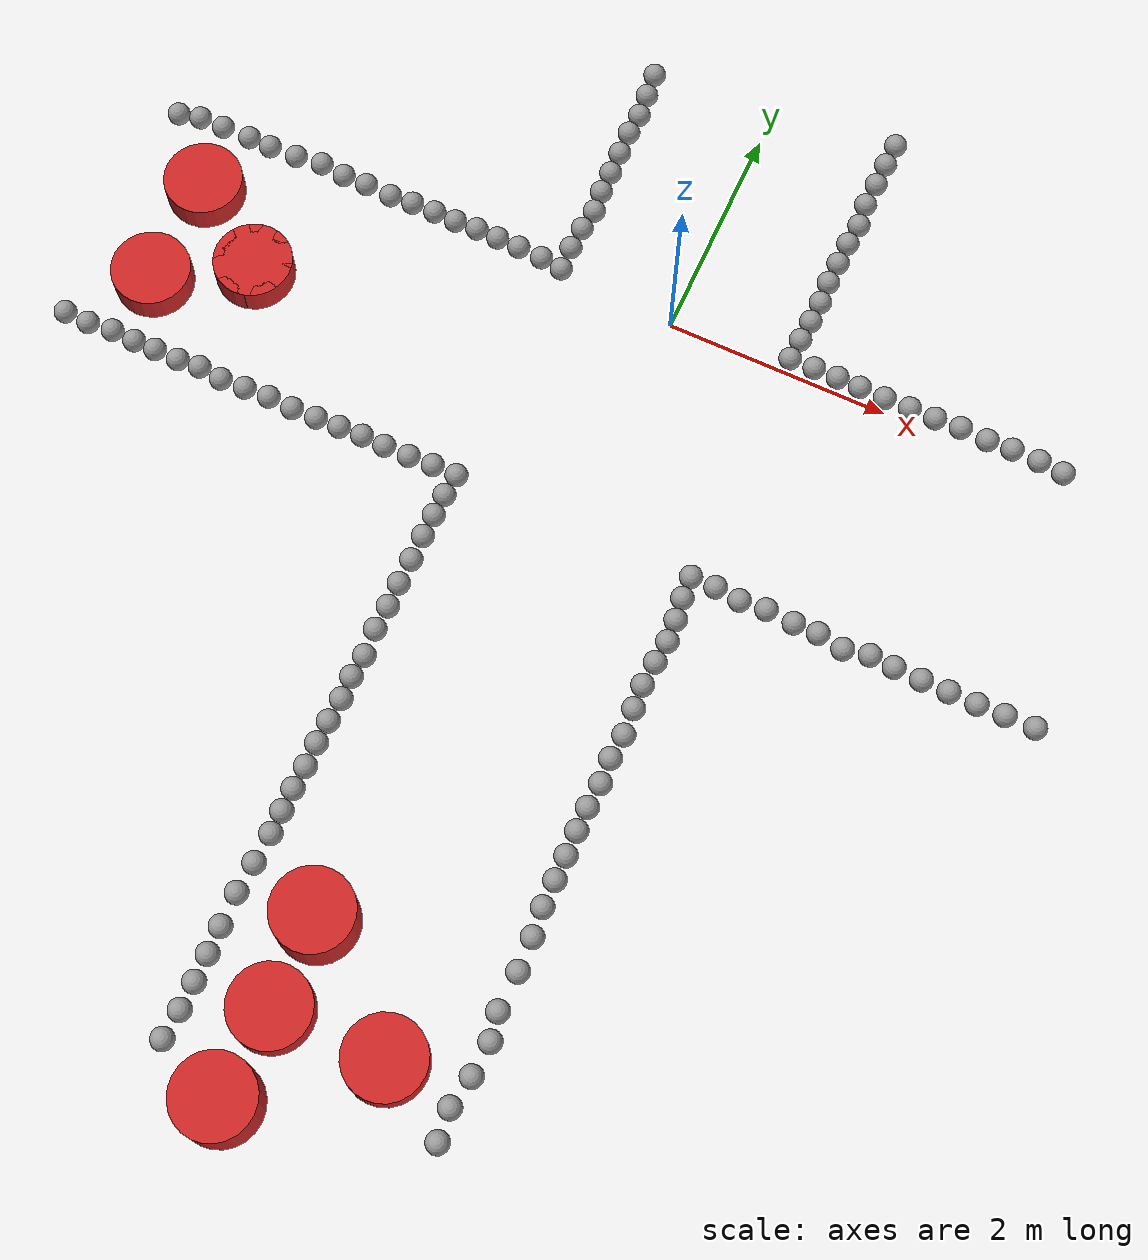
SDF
<sdf version="1.7">
 <world name="default">
  <light name="sun" type="directional">
   <pose>0 0 10 0 -0 0</pose>
   <diffuse>0.8 0.8 0.8 1</diffuse>
   <specular>0.2 0.2 0.2 1</specular>
   <attenuation>
    <range>1000</range>
    <constant>0.9</constant>
    <linear>0.01</linear>
    <quadratic>0.001</quadratic>
   </attenuation>
   <direction>-0.5 0.1 -0.9</direction>
   <spot><inner_angle>0</inner_angle><outer_angle>0</outer_angle><falloff>0</falloff></spot>
  </light>
  <model name="ground_plane">
   <static>1</static>
   <link name="link">
    <collision name="collision">
     <geometry><plane><normal>0 0 1</normal><size>100 100</size></plane></geometry>
     <surface>
      <contact><collide_bitmask>65535</collide_bitmask></contact>
      <friction><ode><mu>100</mu><mu2>50</mu2></ode></friction>
     </surface>
    </collision>
    <visual name="visual">
     <cast_shadows>0</cast_shadows>
     <geometry><plane><normal>0 0 1</normal><size>100 100</size></plane></geometry>
     <material>
      <script><uri>file://media/materials/scripts/gazebo.material</uri><name>Gazebo/White</name></script>
     </material>
    </visual>
   </link>
  </model>
  <gravity>0 0 -9.8</gravity>
  <magnetic_field>6e-06 2.3e-05 -4.2e-05</magnetic_field>
  <atmosphere type="adiabatic"/>
  <physics type="ode">
   <max_step_size>0.001</max_step_size>
   <real_time_factor>1</real_time_factor>
   <real_time_update_rate>1000</real_time_update_rate>
  </physics>
  <scene><ambient>0.4 0.4 0.4 1</ambient><background>0.7 0.7 0.7 1</background><shadows>1</shadows></scene>
  <spherical_coordinates>
   <surface_model>EARTH_WGS84</surface_model>
   <latitude_deg>0</latitude_deg>
   <longitude_deg>0</longitude_deg>
   <elevation>0</elevation>
   <heading_deg>0</heading_deg>
  </spherical_coordinates>
  <model name="model8.3_0">
   <link name="link_1">
    <inertial>
     <mass>1</mass>
     <inertia><ixx>0.145833</ixx><ixy>0</ixy><ixz>0</ixz><iyy>0.145833</iyy><iyz>0</iyz><izz>0.125</izz></inertia>
    </inertial>
    <visual name="visual">
     <geometry><cylinder><radius>0.35</radius><length>0.5</length></cylinder></geometry>
     <material>
      <lighting>1</lighting>
      <script><uri>file://media/materials/scripts/gazebo.material</uri><name>Gazebo/Red</name></script>
      <shader type="pixel"><normal_map>__default__</normal_map></shader>
      <ambient>0.937 0.161 0.161 1</ambient>
      <diffuse>0.7 0.7 0.7 1</diffuse>
      <specular>0.01 0.01 0.01 1</specular>
      <emissive>0 0 0 1</emissive>
     </material>
    </visual>
    <collision name="collision">
     <geometry><cylinder><radius>0.35</radius><length>0.5</length></cylinder></geometry>
     <surface>
      <friction>
       <ode><mu>1</mu><mu2>1</mu2><fdir1>0 0 0</fdir1><slip1>0</slip1><slip2>0</slip2></ode>
       <torsional>
        <coefficient>1</coefficient>
        <patch_radius>0</patch_radius>
        <surface_radius>0</surface_radius>
        <use_patch_radius>1</use_patch_radius>
        <ode><slip>0</slip></ode>
       </torsional>
      </friction>
      <bounce><restitution_coefficient>0</restitution_coefficient><threshold>1e+06</threshold></bounce>
      <contact>
       <collide_without_contact>0</collide_without_contact>
       <collide_without_contact_bitmask>1</collide_without_contact_bitmask>
       <collide_bitmask>1</collide_bitmask>
       <ode>
        <soft_cfm>0</soft_cfm>
        <soft_erp>0.2</soft_erp>
        <kp>1e+13</kp>
        <kd>1</kd>
        <max_vel>0.01</max_vel>
        <min_depth>0</min_depth>
       </ode>
       <bullet>
        <split_impulse>1</split_impulse>
        <split_impulse_penetration_threshold>-0.01</split_impulse_penetration_threshold>
        <soft_cfm>0</soft_cfm>
        <soft_erp>0.2</soft_erp>
        <kp>1e+13</kp>
        <kd>1</kd>
       </bullet>
      </contact>
     </surface>
    </collision>
   </link>
   <static>0</static>
   <pose>-0.441492 -5.95517 0.249991 0 -0 0</pose>
  </model>
  <model name="model8.3_1">
   <link name="link_1">
    <inertial>
     <mass>1</mass>
     <inertia><ixx>0.145833</ixx><ixy>0</ixy><ixz>0</ixz><iyy>0.145833</iyy><iyz>0</iyz><izz>0.125</izz></inertia>
    </inertial>
    <visual name="visual">
     <geometry><cylinder><radius>0.35</radius><length>0.5</length></cylinder></geometry>
     <material>
      <lighting>1</lighting>
      <script><uri>file://media/materials/scripts/gazebo.material</uri><name>Gazebo/Red</name></script>
      <shader type="pixel"><normal_map>__default__</normal_map></shader>
      <ambient>0.937 0.161 0.161 1</ambient>
      <diffuse>0.7 0.7 0.7 1</diffuse>
      <specular>0.01 0.01 0.01 1</specular>
      <emissive>0 0 0 1</emissive>
     </material>
    </visual>
    <collision name="collision">
     <geometry><cylinder><radius>0.35</radius><length>0.5</length></cylinder></geometry>
     <surface>
      <friction>
       <ode><mu>1</mu><mu2>1</mu2><fdir1>0 0 0</fdir1><slip1>0</slip1><slip2>0</slip2></ode>
       <torsional>
        <coefficient>1</coefficient>
        <patch_radius>0</patch_radius>
        <surface_radius>0</surface_radius>
        <use_patch_radius>1</use_patch_radius>
        <ode><slip>0</slip></ode>
       </torsional>
      </friction>
      <bounce><restitution_coefficient>0</restitution_coefficient><threshold>1e+06</threshold></bounce>
      <contact>
       <collide_without_contact>0</collide_without_contact>
       <collide_without_contact_bitmask>1</collide_without_contact_bitmask>
       <collide_bitmask>1</collide_bitmask>
       <ode>
        <soft_cfm>0</soft_cfm>
        <soft_erp>0.2</soft_erp>
        <kp>1e+13</kp>
        <kd>1</kd>
        <max_vel>0.01</max_vel>
        <min_depth>0</min_depth>
       </ode>
       <bullet>
        <split_impulse>1</split_impulse>
        <split_impulse_penetration_threshold>-0.01</split_impulse_penetration_threshold>
        <soft_cfm>0</soft_cfm>
        <soft_erp>0.2</soft_erp>
        <kp>1e+13</kp>
        <kd>1</kd>
       </bullet>
      </contact>
     </surface>
    </collision>
   </link>
   <static>0</static>
   <pose>-0.483911 -7.5282 0.25 0 -0 0</pose>
  </model>
  <model name="sphere">
   <link name="link_0">
    <inertial>
     <mass>1</mass>
     <inertia><ixx>0.1</ixx><ixy>0</ixy><ixz>0</ixz><iyy>0.1</iyy><iyz>0</iyz><izz>0.1</izz></inertia>
    </inertial>
    <visual name="visual">
     <geometry><sphere><radius>0.1</radius></sphere></geometry>
     <material>
      <lighting>1</lighting>
      <script><uri>file://media/materials/scripts/gazebo.material</uri><name>Gazebo/Grey</name></script>
      <shader type="pixel"><normal_map>__default__</normal_map></shader>
      <ambient>0.3 0.3 0.3 1</ambient>
      <diffuse>0.7 0.7 0.7 1</diffuse>
      <specular>0.01 0.01 0.01 1</specular>
      <emissive>0 0 0 1</emissive>
     </material>
    </visual>
    <collision name="collision">
     <geometry><sphere><radius>0.1</radius></sphere></geometry>
     <surface>
      <friction>
       <ode><mu>1</mu><mu2>1</mu2><fdir1>0 0 0</fdir1><slip1>0</slip1><slip2>0</slip2></ode>
       <torsional>
        <coefficient>1</coefficient>
        <patch_radius>0</patch_radius>
        <surface_radius>0</surface_radius>
        <use_patch_radius>1</use_patch_radius>
        <ode><slip>0</slip></ode>
       </torsional>
      </friction>
      <bounce><restitution_coefficient>0</restitution_coefficient><threshold>1e+06</threshold></bounce>
      <contact>
       <collide_without_contact>0</collide_without_contact>
       <collide_without_contact_bitmask>1</collide_without_contact_bitmask>
       <collide_bitmask>1</collide_bitmask>
       <ode>
        <soft_cfm>0</soft_cfm>
        <soft_erp>0.2</soft_erp>
        <kp>1e+13</kp>
        <kd>1</kd>
        <max_vel>0.01</max_vel>
        <min_depth>0</min_depth>
       </ode>
       <bullet>
        <split_impulse>1</split_impulse>
        <split_impulse_penetration_threshold>-0.01</split_impulse_penetration_threshold>
        <soft_cfm>0</soft_cfm>
        <soft_erp>0.2</soft_erp>
        <kp>1e+13</kp>
        <kd>1</kd>
       </bullet>
      </contact>
     </surface>
    </collision>
   </link>
   <static>0</static>
   <pose>-1.09107 -5.49398 0.1 0.122091 -0.000389 0.00322</pose>
  </model>
  <model name="sphere_0">
   <link name="link_0">
    <inertial>
     <mass>1</mass>
     <inertia><ixx>0.1</ixx><ixy>0</ixy><ixz>0</ixz><iyy>0.1</iyy><iyz>0</iyz><izz>0.1</izz></inertia>
    </inertial>
    <visual name="visual">
     <geometry><sphere><radius>0.1</radius></sphere></geometry>
     <material>
      <lighting>1</lighting>
      <script><uri>file://media/materials/scripts/gazebo.material</uri><name>Gazebo/Grey</name></script>
      <shader type="pixel"><normal_map>__default__</normal_map></shader>
      <ambient>0.3 0.3 0.3 1</ambient>
      <diffuse>0.7 0.7 0.7 1</diffuse>
      <specular>0.01 0.01 0.01 1</specular>
      <emissive>0 0 0 1</emissive>
     </material>
    </visual>
    <collision name="collision">
     <geometry><sphere><radius>0.1</radius></sphere></geometry>
     <surface>
      <friction>
       <ode><mu>1</mu><mu2>1</mu2><fdir1>0 0 0</fdir1><slip1>0</slip1><slip2>0</slip2></ode>
       <torsional>
        <coefficient>1</coefficient>
        <patch_radius>0</patch_radius>
        <surface_radius>0</surface_radius>
        <use_patch_radius>1</use_patch_radius>
        <ode><slip>0</slip></ode>
       </torsional>
      </friction>
      <bounce><restitution_coefficient>0</restitution_coefficient><threshold>1e+06</threshold></bounce>
      <contact>
       <collide_without_contact>0</collide_without_contact>
       <collide_without_contact_bitmask>1</collide_without_contact_bitmask>
       <collide_bitmask>1</collide_bitmask>
       <ode>
        <soft_cfm>0</soft_cfm>
        <soft_erp>0.2</soft_erp>
        <kp>1e+13</kp>
        <kd>1</kd>
        <max_vel>0.01</max_vel>
        <min_depth>0</min_depth>
       </ode>
       <bullet>
        <split_impulse>1</split_impulse>
        <split_impulse_penetration_threshold>-0.01</split_impulse_penetration_threshold>
        <soft_cfm>0</soft_cfm>
        <soft_erp>0.2</soft_erp>
        <kp>1e+13</kp>
        <kd>1</kd>
       </bullet>
      </contact>
     </surface>
    </collision>
   </link>
   <static>0</static>
   <pose>-1.09583 -5.29189 0.1 -0.009838 -0.007419 -1.6e-05</pose>
  </model>
  <model name="sphere_1">
   <link name="link_0">
    <inertial>
     <mass>1</mass>
     <inertia><ixx>0.1</ixx><ixy>0</ixy><ixz>0</ixz><iyy>0.1</iyy><iyz>0</iyz><izz>0.1</izz></inertia>
    </inertial>
    <visual name="visual">
     <geometry><sphere><radius>0.1</radius></sphere></geometry>
     <material>
      <lighting>1</lighting>
      <script><uri>file://media/materials/scripts/gazebo.material</uri><name>Gazebo/Grey</name></script>
      <shader type="pixel"><normal_map>__default__</normal_map></shader>
      <ambient>0.3 0.3 0.3 1</ambient>
      <diffuse>0.7 0.7 0.7 1</diffuse>
      <specular>0.01 0.01 0.01 1</specular>
      <emissive>0 0 0 1</emissive>
     </material>
    </visual>
    <collision name="collision">
     <geometry><sphere><radius>0.1</radius></sphere></geometry>
     <surface>
      <friction>
       <ode><mu>1</mu><mu2>1</mu2><fdir1>0 0 0</fdir1><slip1>0</slip1><slip2>0</slip2></ode>
       <torsional>
        <coefficient>1</coefficient>
        <patch_radius>0</patch_radius>
        <surface_radius>0</surface_radius>
        <use_patch_radius>1</use_patch_radius>
        <ode><slip>0</slip></ode>
       </torsional>
      </friction>
      <bounce><restitution_coefficient>0</restitution_coefficient><threshold>1e+06</threshold></bounce>
      <contact>
       <collide_without_contact>0</collide_without_contact>
       <collide_without_contact_bitmask>1</collide_without_contact_bitmask>
       <collide_bitmask>1</collide_bitmask>
       <ode>
        <soft_cfm>0</soft_cfm>
        <soft_erp>0.2</soft_erp>
        <kp>1e+13</kp>
        <kd>1</kd>
        <max_vel>0.01</max_vel>
        <min_depth>0</min_depth>
       </ode>
       <bullet>
        <split_impulse>1</split_impulse>
        <split_impulse_penetration_threshold>-0.01</split_impulse_penetration_threshold>
        <soft_cfm>0</soft_cfm>
        <soft_erp>0.2</soft_erp>
        <kp>1e+13</kp>
        <kd>1</kd>
       </bullet>
      </contact>
     </surface>
    </collision>
   </link>
   <static>0</static>
   <pose>-1.09699 -5.09057 0.1 -0.124833 -0.004277 -0.003014</pose>
  </model>
  <model name="sphere_2">
   <link name="link_0">
    <inertial>
     <mass>1</mass>
     <inertia><ixx>0.1</ixx><ixy>0</ixy><ixz>0</ixz><iyy>0.1</iyy><iyz>0</iyz><izz>0.1</izz></inertia>
    </inertial>
    <visual name="visual">
     <geometry><sphere><radius>0.1</radius></sphere></geometry>
     <material>
      <lighting>1</lighting>
      <script><uri>file://media/materials/scripts/gazebo.material</uri><name>Gazebo/Grey</name></script>
      <shader type="pixel"><normal_map>__default__</normal_map></shader>
      <ambient>0.3 0.3 0.3 1</ambient>
      <diffuse>0.7 0.7 0.7 1</diffuse>
      <specular>0.01 0.01 0.01 1</specular>
      <emissive>0 0 0 1</emissive>
     </material>
    </visual>
    <collision name="collision">
     <geometry><sphere><radius>0.1</radius></sphere></geometry>
     <surface>
      <friction>
       <ode><mu>1</mu><mu2>1</mu2><fdir1>0 0 0</fdir1><slip1>0</slip1><slip2>0</slip2></ode>
       <torsional>
        <coefficient>1</coefficient>
        <patch_radius>0</patch_radius>
        <surface_radius>0</surface_radius>
        <use_patch_radius>1</use_patch_radius>
        <ode><slip>0</slip></ode>
       </torsional>
      </friction>
      <bounce><restitution_coefficient>0</restitution_coefficient><threshold>1e+06</threshold></bounce>
      <contact>
       <collide_without_contact>0</collide_without_contact>
       <collide_without_contact_bitmask>1</collide_without_contact_bitmask>
       <collide_bitmask>1</collide_bitmask>
       <ode>
        <soft_cfm>0</soft_cfm>
        <soft_erp>0.2</soft_erp>
        <kp>1e+13</kp>
        <kd>1</kd>
        <max_vel>0.01</max_vel>
        <min_depth>0</min_depth>
       </ode>
       <bullet>
        <split_impulse>1</split_impulse>
        <split_impulse_penetration_threshold>-0.01</split_impulse_penetration_threshold>
        <soft_cfm>0</soft_cfm>
        <soft_erp>0.2</soft_erp>
        <kp>1e+13</kp>
        <kd>1</kd>
       </bullet>
      </contact>
     </surface>
    </collision>
   </link>
   <static>0</static>
   <pose>-1.09009 -4.88333 0.1 0 -0 0</pose>
  </model>
  <model name="sphere_3">
   <link name="link_0">
    <inertial>
     <mass>1</mass>
     <inertia><ixx>0.1</ixx><ixy>0</ixy><ixz>0</ixz><iyy>0.1</iyy><iyz>0</iyz><izz>0.1</izz></inertia>
    </inertial>
    <visual name="visual">
     <geometry><sphere><radius>0.1</radius></sphere></geometry>
     <material>
      <lighting>1</lighting>
      <script><uri>file://media/materials/scripts/gazebo.material</uri><name>Gazebo/Grey</name></script>
      <shader type="pixel"><normal_map>__default__</normal_map></shader>
      <ambient>0.3 0.3 0.3 1</ambient>
      <diffuse>0.7 0.7 0.7 1</diffuse>
      <specular>0.01 0.01 0.01 1</specular>
      <emissive>0 0 0 1</emissive>
     </material>
    </visual>
    <collision name="collision">
     <geometry><sphere><radius>0.1</radius></sphere></geometry>
     <surface>
      <friction>
       <ode><mu>1</mu><mu2>1</mu2><fdir1>0 0 0</fdir1><slip1>0</slip1><slip2>0</slip2></ode>
       <torsional>
        <coefficient>1</coefficient>
        <patch_radius>0</patch_radius>
        <surface_radius>0</surface_radius>
        <use_patch_radius>1</use_patch_radius>
        <ode><slip>0</slip></ode>
       </torsional>
      </friction>
      <bounce><restitution_coefficient>0</restitution_coefficient><threshold>1e+06</threshold></bounce>
      <contact>
       <collide_without_contact>0</collide_without_contact>
       <collide_without_contact_bitmask>1</collide_without_contact_bitmask>
       <collide_bitmask>1</collide_bitmask>
       <ode>
        <soft_cfm>0</soft_cfm>
        <soft_erp>0.2</soft_erp>
        <kp>1e+13</kp>
        <kd>1</kd>
        <max_vel>0.01</max_vel>
        <min_depth>0</min_depth>
       </ode>
       <bullet>
        <split_impulse>1</split_impulse>
        <split_impulse_penetration_threshold>-0.01</split_impulse_penetration_threshold>
        <soft_cfm>0</soft_cfm>
        <soft_erp>0.2</soft_erp>
        <kp>1e+13</kp>
        <kd>1</kd>
       </bullet>
      </contact>
     </surface>
    </collision>
   </link>
   <static>0</static>
   <pose>-1.09593 -4.67195 0.1 0 -0 0</pose>
  </model>
  <model name="sphere_4">
   <link name="link_0">
    <inertial>
     <mass>1</mass>
     <inertia><ixx>0.1</ixx><ixy>0</ixy><ixz>0</ixz><iyy>0.1</iyy><iyz>0</iyz><izz>0.1</izz></inertia>
    </inertial>
    <visual name="visual">
     <geometry><sphere><radius>0.1</radius></sphere></geometry>
     <material>
      <lighting>1</lighting>
      <script><uri>file://media/materials/scripts/gazebo.material</uri><name>Gazebo/Grey</name></script>
      <shader type="pixel"><normal_map>__default__</normal_map></shader>
      <ambient>0.3 0.3 0.3 1</ambient>
      <diffuse>0.7 0.7 0.7 1</diffuse>
      <specular>0.01 0.01 0.01 1</specular>
      <emissive>0 0 0 1</emissive>
     </material>
    </visual>
    <collision name="collision">
     <geometry><sphere><radius>0.1</radius></sphere></geometry>
     <surface>
      <friction>
       <ode><mu>1</mu><mu2>1</mu2><fdir1>0 0 0</fdir1><slip1>0</slip1><slip2>0</slip2></ode>
       <torsional>
        <coefficient>1</coefficient>
        <patch_radius>0</patch_radius>
        <surface_radius>0</surface_radius>
        <use_patch_radius>1</use_patch_radius>
        <ode><slip>0</slip></ode>
       </torsional>
      </friction>
      <bounce><restitution_coefficient>0</restitution_coefficient><threshold>1e+06</threshold></bounce>
      <contact>
       <collide_without_contact>0</collide_without_contact>
       <collide_without_contact_bitmask>1</collide_without_contact_bitmask>
       <collide_bitmask>1</collide_bitmask>
       <ode>
        <soft_cfm>0</soft_cfm>
        <soft_erp>0.2</soft_erp>
        <kp>1e+13</kp>
        <kd>1</kd>
        <max_vel>0.01</max_vel>
        <min_depth>0</min_depth>
       </ode>
       <bullet>
        <split_impulse>1</split_impulse>
        <split_impulse_penetration_threshold>-0.01</split_impulse_penetration_threshold>
        <soft_cfm>0</soft_cfm>
        <soft_erp>0.2</soft_erp>
        <kp>1e+13</kp>
        <kd>1</kd>
       </bullet>
      </contact>
     </surface>
    </collision>
   </link>
   <static>0</static>
   <pose>-1.0917 -4.46699 0.1 0 -0 0</pose>
  </model>
  <model name="sphere_5">
   <link name="link_0">
    <inertial>
     <mass>1</mass>
     <inertia><ixx>0.1</ixx><ixy>0</ixy><ixz>0</ixz><iyy>0.1</iyy><iyz>0</iyz><izz>0.1</izz></inertia>
    </inertial>
    <visual name="visual">
     <geometry><sphere><radius>0.1</radius></sphere></geometry>
     <material>
      <lighting>1</lighting>
      <script><uri>file://media/materials/scripts/gazebo.material</uri><name>Gazebo/Grey</name></script>
      <shader type="pixel"><normal_map>__default__</normal_map></shader>
      <ambient>0.3 0.3 0.3 1</ambient>
      <diffuse>0.7 0.7 0.7 1</diffuse>
      <specular>0.01 0.01 0.01 1</specular>
      <emissive>0 0 0 1</emissive>
     </material>
    </visual>
    <collision name="collision">
     <geometry><sphere><radius>0.1</radius></sphere></geometry>
     <surface>
      <friction>
       <ode><mu>1</mu><mu2>1</mu2><fdir1>0 0 0</fdir1><slip1>0</slip1><slip2>0</slip2></ode>
       <torsional>
        <coefficient>1</coefficient>
        <patch_radius>0</patch_radius>
        <surface_radius>0</surface_radius>
        <use_patch_radius>1</use_patch_radius>
        <ode><slip>0</slip></ode>
       </torsional>
      </friction>
      <bounce><restitution_coefficient>0</restitution_coefficient><threshold>1e+06</threshold></bounce>
      <contact>
       <collide_without_contact>0</collide_without_contact>
       <collide_without_contact_bitmask>1</collide_without_contact_bitmask>
       <collide_bitmask>1</collide_bitmask>
       <ode>
        <soft_cfm>0</soft_cfm>
        <soft_erp>0.2</soft_erp>
        <kp>1e+13</kp>
        <kd>1</kd>
        <max_vel>0.01</max_vel>
        <min_depth>0</min_depth>
       </ode>
       <bullet>
        <split_impulse>1</split_impulse>
        <split_impulse_penetration_threshold>-0.01</split_impulse_penetration_threshold>
        <soft_cfm>0</soft_cfm>
        <soft_erp>0.2</soft_erp>
        <kp>1e+13</kp>
        <kd>1</kd>
       </bullet>
      </contact>
     </surface>
    </collision>
   </link>
   <static>0</static>
   <pose>-1.08101 -4.25403 0.1 0.127097 0.006179 -0.000169</pose>
  </model>
  <model name="sphere_6">
   <link name="link_0">
    <inertial>
     <mass>1</mass>
     <inertia><ixx>0.1</ixx><ixy>0</ixy><ixz>0</ixz><iyy>0.1</iyy><iyz>0</iyz><izz>0.1</izz></inertia>
    </inertial>
    <visual name="visual">
     <geometry><sphere><radius>0.1</radius></sphere></geometry>
     <material>
      <lighting>1</lighting>
      <script><uri>file://media/materials/scripts/gazebo.material</uri><name>Gazebo/Grey</name></script>
      <shader type="pixel"><normal_map>__default__</normal_map></shader>
      <ambient>0.3 0.3 0.3 1</ambient>
      <diffuse>0.7 0.7 0.7 1</diffuse>
      <specular>0.01 0.01 0.01 1</specular>
      <emissive>0 0 0 1</emissive>
     </material>
    </visual>
    <collision name="collision">
     <geometry><sphere><radius>0.1</radius></sphere></geometry>
     <surface>
      <friction>
       <ode><mu>1</mu><mu2>1</mu2><fdir1>0 0 0</fdir1><slip1>0</slip1><slip2>0</slip2></ode>
       <torsional>
        <coefficient>1</coefficient>
        <patch_radius>0</patch_radius>
        <surface_radius>0</surface_radius>
        <use_patch_radius>1</use_patch_radius>
        <ode><slip>0</slip></ode>
       </torsional>
      </friction>
      <bounce><restitution_coefficient>0</restitution_coefficient><threshold>1e+06</threshold></bounce>
      <contact>
       <collide_without_contact>0</collide_without_contact>
       <collide_without_contact_bitmask>1</collide_without_contact_bitmask>
       <collide_bitmask>1</collide_bitmask>
       <ode>
        <soft_cfm>0</soft_cfm>
        <soft_erp>0.2</soft_erp>
        <kp>1e+13</kp>
        <kd>1</kd>
        <max_vel>0.01</max_vel>
        <min_depth>0</min_depth>
       </ode>
       <bullet>
        <split_impulse>1</split_impulse>
        <split_impulse_penetration_threshold>-0.01</split_impulse_penetration_threshold>
        <soft_cfm>0</soft_cfm>
        <soft_erp>0.2</soft_erp>
        <kp>1e+13</kp>
        <kd>1</kd>
       </bullet>
      </contact>
     </surface>
    </collision>
   </link>
   <static>0</static>
   <pose>-1.08988 -4.04926 0.1 -0.122309 -0.005909 -0.000202</pose>
  </model>
  <model name="sphere_7">
   <link name="link_0">
    <inertial>
     <mass>1</mass>
     <inertia><ixx>0.1</ixx><ixy>0</ixy><ixz>0</ixz><iyy>0.1</iyy><iyz>0</iyz><izz>0.1</izz></inertia>
    </inertial>
    <visual name="visual">
     <geometry><sphere><radius>0.1</radius></sphere></geometry>
     <material>
      <lighting>1</lighting>
      <script><uri>file://media/materials/scripts/gazebo.material</uri><name>Gazebo/Grey</name></script>
      <shader type="pixel"><normal_map>__default__</normal_map></shader>
      <ambient>0.3 0.3 0.3 1</ambient>
      <diffuse>0.7 0.7 0.7 1</diffuse>
      <specular>0.01 0.01 0.01 1</specular>
      <emissive>0 0 0 1</emissive>
     </material>
    </visual>
    <collision name="collision">
     <geometry><sphere><radius>0.1</radius></sphere></geometry>
     <surface>
      <friction>
       <ode><mu>1</mu><mu2>1</mu2><fdir1>0 0 0</fdir1><slip1>0</slip1><slip2>0</slip2></ode>
       <torsional>
        <coefficient>1</coefficient>
        <patch_radius>0</patch_radius>
        <surface_radius>0</surface_radius>
        <use_patch_radius>1</use_patch_radius>
        <ode><slip>0</slip></ode>
       </torsional>
      </friction>
      <bounce><restitution_coefficient>0</restitution_coefficient><threshold>1e+06</threshold></bounce>
      <contact>
       <collide_without_contact>0</collide_without_contact>
       <collide_without_contact_bitmask>1</collide_without_contact_bitmask>
       <collide_bitmask>1</collide_bitmask>
       <ode>
        <soft_cfm>0</soft_cfm>
        <soft_erp>0.2</soft_erp>
        <kp>1e+13</kp>
        <kd>1</kd>
        <max_vel>0.01</max_vel>
        <min_depth>0</min_depth>
       </ode>
       <bullet>
        <split_impulse>1</split_impulse>
        <split_impulse_penetration_threshold>-0.01</split_impulse_penetration_threshold>
        <soft_cfm>0</soft_cfm>
        <soft_erp>0.2</soft_erp>
        <kp>1e+13</kp>
        <kd>1</kd>
       </bullet>
      </contact>
     </surface>
    </collision>
   </link>
   <static>0</static>
   <pose>-1.07358 -3.84349 0.1 0 -0 0</pose>
  </model>
  <model name="sphere_8">
   <link name="link_0">
    <inertial>
     <mass>1</mass>
     <inertia><ixx>0.1</ixx><ixy>0</ixy><ixz>0</ixz><iyy>0.1</iyy><iyz>0</iyz><izz>0.1</izz></inertia>
    </inertial>
    <visual name="visual">
     <geometry><sphere><radius>0.1</radius></sphere></geometry>
     <material>
      <lighting>1</lighting>
      <script><uri>file://media/materials/scripts/gazebo.material</uri><name>Gazebo/Grey</name></script>
      <shader type="pixel"><normal_map>__default__</normal_map></shader>
      <ambient>0.3 0.3 0.3 1</ambient>
      <diffuse>0.7 0.7 0.7 1</diffuse>
      <specular>0.01 0.01 0.01 1</specular>
      <emissive>0 0 0 1</emissive>
     </material>
    </visual>
    <collision name="collision">
     <geometry><sphere><radius>0.1</radius></sphere></geometry>
     <surface>
      <friction>
       <ode><mu>1</mu><mu2>1</mu2><fdir1>0 0 0</fdir1><slip1>0</slip1><slip2>0</slip2></ode>
       <torsional>
        <coefficient>1</coefficient>
        <patch_radius>0</patch_radius>
        <surface_radius>0</surface_radius>
        <use_patch_radius>1</use_patch_radius>
        <ode><slip>0</slip></ode>
       </torsional>
      </friction>
      <bounce><restitution_coefficient>0</restitution_coefficient><threshold>1e+06</threshold></bounce>
      <contact>
       <collide_without_contact>0</collide_without_contact>
       <collide_without_contact_bitmask>1</collide_without_contact_bitmask>
       <collide_bitmask>1</collide_bitmask>
       <ode>
        <soft_cfm>0</soft_cfm>
        <soft_erp>0.2</soft_erp>
        <kp>1e+13</kp>
        <kd>1</kd>
        <max_vel>0.01</max_vel>
        <min_depth>0</min_depth>
       </ode>
       <bullet>
        <split_impulse>1</split_impulse>
        <split_impulse_penetration_threshold>-0.01</split_impulse_penetration_threshold>
        <soft_cfm>0</soft_cfm>
        <soft_erp>0.2</soft_erp>
        <kp>1e+13</kp>
        <kd>1</kd>
       </bullet>
      </contact>
     </surface>
    </collision>
   </link>
   <static>0</static>
   <pose>-1.09424 -3.60094 0.1 0 -0 0</pose>
  </model>
  <model name="sphere_9">
   <link name="link_0">
    <inertial>
     <mass>1</mass>
     <inertia><ixx>0.1</ixx><ixy>0</ixy><ixz>0</ixz><iyy>0.1</iyy><iyz>0</iyz><izz>0.1</izz></inertia>
    </inertial>
    <visual name="visual">
     <geometry><sphere><radius>0.1</radius></sphere></geometry>
     <material>
      <lighting>1</lighting>
      <script><uri>file://media/materials/scripts/gazebo.material</uri><name>Gazebo/Grey</name></script>
      <shader type="pixel"><normal_map>__default__</normal_map></shader>
      <ambient>0.3 0.3 0.3 1</ambient>
      <diffuse>0.7 0.7 0.7 1</diffuse>
      <specular>0.01 0.01 0.01 1</specular>
      <emissive>0 0 0 1</emissive>
     </material>
    </visual>
    <collision name="collision">
     <geometry><sphere><radius>0.1</radius></sphere></geometry>
     <surface>
      <friction>
       <ode><mu>1</mu><mu2>1</mu2><fdir1>0 0 0</fdir1><slip1>0</slip1><slip2>0</slip2></ode>
       <torsional>
        <coefficient>1</coefficient>
        <patch_radius>0</patch_radius>
        <surface_radius>0</surface_radius>
        <use_patch_radius>1</use_patch_radius>
        <ode><slip>0</slip></ode>
       </torsional>
      </friction>
      <bounce><restitution_coefficient>0</restitution_coefficient><threshold>1e+06</threshold></bounce>
      <contact>
       <collide_without_contact>0</collide_without_contact>
       <collide_without_contact_bitmask>1</collide_without_contact_bitmask>
       <collide_bitmask>1</collide_bitmask>
       <ode>
        <soft_cfm>0</soft_cfm>
        <soft_erp>0.2</soft_erp>
        <kp>1e+13</kp>
        <kd>1</kd>
        <max_vel>0.01</max_vel>
        <min_depth>0</min_depth>
       </ode>
       <bullet>
        <split_impulse>1</split_impulse>
        <split_impulse_penetration_threshold>-0.01</split_impulse_penetration_threshold>
        <soft_cfm>0</soft_cfm>
        <soft_erp>0.2</soft_erp>
        <kp>1e+13</kp>
        <kd>1</kd>
       </bullet>
      </contact>
     </surface>
    </collision>
   </link>
   <static>0</static>
   <pose>-1.08701 -3.37767 0.1 0 -0 0</pose>
  </model>
  <model name="sphere_10">
   <link name="link_0">
    <inertial>
     <mass>1</mass>
     <inertia><ixx>0.1</ixx><ixy>0</ixy><ixz>0</ixz><iyy>0.1</iyy><iyz>0</iyz><izz>0.1</izz></inertia>
    </inertial>
    <visual name="visual">
     <geometry><sphere><radius>0.1</radius></sphere></geometry>
     <material>
      <lighting>1</lighting>
      <script><uri>file://media/materials/scripts/gazebo.material</uri><name>Gazebo/Grey</name></script>
      <shader type="pixel"><normal_map>__default__</normal_map></shader>
      <ambient>0.3 0.3 0.3 1</ambient>
      <diffuse>0.7 0.7 0.7 1</diffuse>
      <specular>0.01 0.01 0.01 1</specular>
      <emissive>0 0 0 1</emissive>
     </material>
    </visual>
    <collision name="collision">
     <geometry><sphere><radius>0.1</radius></sphere></geometry>
     <surface>
      <friction>
       <ode><mu>1</mu><mu2>1</mu2><fdir1>0 0 0</fdir1><slip1>0</slip1><slip2>0</slip2></ode>
       <torsional>
        <coefficient>1</coefficient>
        <patch_radius>0</patch_radius>
        <surface_radius>0</surface_radius>
        <use_patch_radius>1</use_patch_radius>
        <ode><slip>0</slip></ode>
       </torsional>
      </friction>
      <bounce><restitution_coefficient>0</restitution_coefficient><threshold>1e+06</threshold></bounce>
      <contact>
       <collide_without_contact>0</collide_without_contact>
       <collide_without_contact_bitmask>1</collide_without_contact_bitmask>
       <collide_bitmask>1</collide_bitmask>
       <ode>
        <soft_cfm>0</soft_cfm>
        <soft_erp>0.2</soft_erp>
        <kp>1e+13</kp>
        <kd>1</kd>
        <max_vel>0.01</max_vel>
        <min_depth>0</min_depth>
       </ode>
       <bullet>
        <split_impulse>1</split_impulse>
        <split_impulse_penetration_threshold>-0.01</split_impulse_penetration_threshold>
        <soft_cfm>0</soft_cfm>
        <soft_erp>0.2</soft_erp>
        <kp>1e+13</kp>
        <kd>1</kd>
       </bullet>
      </contact>
     </surface>
    </collision>
   </link>
   <static>0</static>
   <pose>-1.09342 -3.15905 0.1 0 -0 0</pose>
  </model>
  <model name="sphere_11">
   <link name="link_0">
    <inertial>
     <mass>1</mass>
     <inertia><ixx>0.1</ixx><ixy>0</ixy><ixz>0</ixz><iyy>0.1</iyy><iyz>0</iyz><izz>0.1</izz></inertia>
    </inertial>
    <visual name="visual">
     <geometry><sphere><radius>0.1</radius></sphere></geometry>
     <material>
      <lighting>1</lighting>
      <script><uri>file://media/materials/scripts/gazebo.material</uri><name>Gazebo/Grey</name></script>
      <shader type="pixel"><normal_map>__default__</normal_map></shader>
      <ambient>0.3 0.3 0.3 1</ambient>
      <diffuse>0.7 0.7 0.7 1</diffuse>
      <specular>0.01 0.01 0.01 1</specular>
      <emissive>0 0 0 1</emissive>
     </material>
    </visual>
    <collision name="collision">
     <geometry><sphere><radius>0.1</radius></sphere></geometry>
     <surface>
      <friction>
       <ode><mu>1</mu><mu2>1</mu2><fdir1>0 0 0</fdir1><slip1>0</slip1><slip2>0</slip2></ode>
       <torsional>
        <coefficient>1</coefficient>
        <patch_radius>0</patch_radius>
        <surface_radius>0</surface_radius>
        <use_patch_radius>1</use_patch_radius>
        <ode><slip>0</slip></ode>
       </torsional>
      </friction>
      <bounce><restitution_coefficient>0</restitution_coefficient><threshold>1e+06</threshold></bounce>
      <contact>
       <collide_without_contact>0</collide_without_contact>
       <collide_without_contact_bitmask>1</collide_without_contact_bitmask>
       <collide_bitmask>1</collide_bitmask>
       <ode>
        <soft_cfm>0</soft_cfm>
        <soft_erp>0.2</soft_erp>
        <kp>1e+13</kp>
        <kd>1</kd>
        <max_vel>0.01</max_vel>
        <min_depth>0</min_depth>
       </ode>
       <bullet>
        <split_impulse>1</split_impulse>
        <split_impulse_penetration_threshold>-0.01</split_impulse_penetration_threshold>
        <soft_cfm>0</soft_cfm>
        <soft_erp>0.2</soft_erp>
        <kp>1e+13</kp>
        <kd>1</kd>
       </bullet>
      </contact>
     </surface>
    </collision>
   </link>
   <static>0</static>
   <pose>-1.09082 -2.92679 0.1 0 -0 0</pose>
  </model>
  <model name="sphere_12">
   <link name="link_0">
    <inertial>
     <mass>1</mass>
     <inertia><ixx>0.1</ixx><ixy>0</ixy><ixz>0</ixz><iyy>0.1</iyy><iyz>0</iyz><izz>0.1</izz></inertia>
    </inertial>
    <visual name="visual">
     <geometry><sphere><radius>0.1</radius></sphere></geometry>
     <material>
      <lighting>1</lighting>
      <script><uri>file://media/materials/scripts/gazebo.material</uri><name>Gazebo/Grey</name></script>
      <shader type="pixel"><normal_map>__default__</normal_map></shader>
      <ambient>0.3 0.3 0.3 1</ambient>
      <diffuse>0.7 0.7 0.7 1</diffuse>
      <specular>0.01 0.01 0.01 1</specular>
      <emissive>0 0 0 1</emissive>
     </material>
    </visual>
    <collision name="collision">
     <geometry><sphere><radius>0.1</radius></sphere></geometry>
     <surface>
      <friction>
       <ode><mu>1</mu><mu2>1</mu2><fdir1>0 0 0</fdir1><slip1>0</slip1><slip2>0</slip2></ode>
       <torsional>
        <coefficient>1</coefficient>
        <patch_radius>0</patch_radius>
        <surface_radius>0</surface_radius>
        <use_patch_radius>1</use_patch_radius>
        <ode><slip>0</slip></ode>
       </torsional>
      </friction>
      <bounce><restitution_coefficient>0</restitution_coefficient><threshold>1e+06</threshold></bounce>
      <contact>
       <collide_without_contact>0</collide_without_contact>
       <collide_without_contact_bitmask>1</collide_without_contact_bitmask>
       <collide_bitmask>1</collide_bitmask>
       <ode>
        <soft_cfm>0</soft_cfm>
        <soft_erp>0.2</soft_erp>
        <kp>1e+13</kp>
        <kd>1</kd>
        <max_vel>0.01</max_vel>
        <min_depth>0</min_depth>
       </ode>
       <bullet>
        <split_impulse>1</split_impulse>
        <split_impulse_penetration_threshold>-0.01</split_impulse_penetration_threshold>
        <soft_cfm>0</soft_cfm>
        <soft_erp>0.2</soft_erp>
        <kp>1e+13</kp>
        <kd>1</kd>
       </bullet>
      </contact>
     </surface>
    </collision>
   </link>
   <static>0</static>
   <pose>-1.09448 -2.6955 0.1 0 -0 0</pose>
  </model>
  <model name="sphere_13">
   <link name="link_0">
    <inertial>
     <mass>1</mass>
     <inertia><ixx>0.1</ixx><ixy>0</ixy><ixz>0</ixz><iyy>0.1</iyy><iyz>0</iyz><izz>0.1</izz></inertia>
    </inertial>
    <visual name="visual">
     <geometry><sphere><radius>0.1</radius></sphere></geometry>
     <material>
      <lighting>1</lighting>
      <script><uri>file://media/materials/scripts/gazebo.material</uri><name>Gazebo/Grey</name></script>
      <shader type="pixel"><normal_map>__default__</normal_map></shader>
      <ambient>0.3 0.3 0.3 1</ambient>
      <diffuse>0.7 0.7 0.7 1</diffuse>
      <specular>0.01 0.01 0.01 1</specular>
      <emissive>0 0 0 1</emissive>
     </material>
    </visual>
    <collision name="collision">
     <geometry><sphere><radius>0.1</radius></sphere></geometry>
     <surface>
      <friction>
       <ode><mu>1</mu><mu2>1</mu2><fdir1>0 0 0</fdir1><slip1>0</slip1><slip2>0</slip2></ode>
       <torsional>
        <coefficient>1</coefficient>
        <patch_radius>0</patch_radius>
        <surface_radius>0</surface_radius>
        <use_patch_radius>1</use_patch_radius>
        <ode><slip>0</slip></ode>
       </torsional>
      </friction>
      <bounce><restitution_coefficient>0</restitution_coefficient><threshold>1e+06</threshold></bounce>
      <contact>
       <collide_without_contact>0</collide_without_contact>
       <collide_without_contact_bitmask>1</collide_without_contact_bitmask>
       <collide_bitmask>1</collide_bitmask>
       <ode>
        <soft_cfm>0</soft_cfm>
        <soft_erp>0.2</soft_erp>
        <kp>1e+13</kp>
        <kd>1</kd>
        <max_vel>0.01</max_vel>
        <min_depth>0</min_depth>
       </ode>
       <bullet>
        <split_impulse>1</split_impulse>
        <split_impulse_penetration_threshold>-0.01</split_impulse_penetration_threshold>
        <soft_cfm>0</soft_cfm>
        <soft_erp>0.2</soft_erp>
        <kp>1e+13</kp>
        <kd>1</kd>
       </bullet>
      </contact>
     </surface>
    </collision>
   </link>
   <static>0</static>
   <pose>-1.09339 -2.48857 0.1 0 -0 0</pose>
  </model>
  <model name="sphere_14">
   <link name="link_0">
    <inertial>
     <mass>1</mass>
     <inertia><ixx>0.1</ixx><ixy>0</ixy><ixz>0</ixz><iyy>0.1</iyy><iyz>0</iyz><izz>0.1</izz></inertia>
    </inertial>
    <visual name="visual">
     <geometry><sphere><radius>0.1</radius></sphere></geometry>
     <material>
      <lighting>1</lighting>
      <script><uri>file://media/materials/scripts/gazebo.material</uri><name>Gazebo/Grey</name></script>
      <shader type="pixel"><normal_map>__default__</normal_map></shader>
      <ambient>0.3 0.3 0.3 1</ambient>
      <diffuse>0.7 0.7 0.7 1</diffuse>
      <specular>0.01 0.01 0.01 1</specular>
      <emissive>0 0 0 1</emissive>
     </material>
    </visual>
    <collision name="collision">
     <geometry><sphere><radius>0.1</radius></sphere></geometry>
     <surface>
      <friction>
       <ode><mu>1</mu><mu2>1</mu2><fdir1>0 0 0</fdir1><slip1>0</slip1><slip2>0</slip2></ode>
       <torsional>
        <coefficient>1</coefficient>
        <patch_radius>0</patch_radius>
        <surface_radius>0</surface_radius>
        <use_patch_radius>1</use_patch_radius>
        <ode><slip>0</slip></ode>
       </torsional>
      </friction>
      <bounce><restitution_coefficient>0</restitution_coefficient><threshold>1e+06</threshold></bounce>
      <contact>
       <collide_without_contact>0</collide_without_contact>
       <collide_without_contact_bitmask>1</collide_without_contact_bitmask>
       <collide_bitmask>1</collide_bitmask>
       <ode>
        <soft_cfm>0</soft_cfm>
        <soft_erp>0.2</soft_erp>
        <kp>1e+13</kp>
        <kd>1</kd>
        <max_vel>0.01</max_vel>
        <min_depth>0</min_depth>
       </ode>
       <bullet>
        <split_impulse>1</split_impulse>
        <split_impulse_penetration_threshold>-0.01</split_impulse_penetration_threshold>
        <soft_cfm>0</soft_cfm>
        <soft_erp>0.2</soft_erp>
        <kp>1e+13</kp>
        <kd>1</kd>
       </bullet>
      </contact>
     </surface>
    </collision>
   </link>
   <static>0</static>
   <pose>-1.09015 -2.2869 0.1 0.054807 -0.004576 0.000566</pose>
  </model>
  <model name="sphere_15">
   <link name="link_0">
    <inertial>
     <mass>1</mass>
     <inertia><ixx>0.1</ixx><ixy>0</ixy><ixz>0</ixz><iyy>0.1</iyy><iyz>0</iyz><izz>0.1</izz></inertia>
    </inertial>
    <visual name="visual">
     <geometry><sphere><radius>0.1</radius></sphere></geometry>
     <material>
      <lighting>1</lighting>
      <script><uri>file://media/materials/scripts/gazebo.material</uri><name>Gazebo/Grey</name></script>
      <shader type="pixel"><normal_map>__default__</normal_map></shader>
      <ambient>0.3 0.3 0.3 1</ambient>
      <diffuse>0.7 0.7 0.7 1</diffuse>
      <specular>0.01 0.01 0.01 1</specular>
      <emissive>0 0 0 1</emissive>
     </material>
    </visual>
    <collision name="collision">
     <geometry><sphere><radius>0.1</radius></sphere></geometry>
     <surface>
      <friction>
       <ode><mu>1</mu><mu2>1</mu2><fdir1>0 0 0</fdir1><slip1>0</slip1><slip2>0</slip2></ode>
       <torsional>
        <coefficient>1</coefficient>
        <patch_radius>0</patch_radius>
        <surface_radius>0</surface_radius>
        <use_patch_radius>1</use_patch_radius>
        <ode><slip>0</slip></ode>
       </torsional>
      </friction>
      <bounce><restitution_coefficient>0</restitution_coefficient><threshold>1e+06</threshold></bounce>
      <contact>
       <collide_without_contact>0</collide_without_contact>
       <collide_without_contact_bitmask>1</collide_without_contact_bitmask>
       <collide_bitmask>1</collide_bitmask>
       <ode>
        <soft_cfm>0</soft_cfm>
        <soft_erp>0.2</soft_erp>
        <kp>1e+13</kp>
        <kd>1</kd>
        <max_vel>0.01</max_vel>
        <min_depth>0</min_depth>
       </ode>
       <bullet>
        <split_impulse>1</split_impulse>
        <split_impulse_penetration_threshold>-0.01</split_impulse_penetration_threshold>
        <soft_cfm>0</soft_cfm>
        <soft_erp>0.2</soft_erp>
        <kp>1e+13</kp>
        <kd>1</kd>
       </bullet>
      </contact>
     </surface>
    </collision>
   </link>
   <static>0</static>
   <pose>-1.07546 -2.08235 0.1 -0.059386 0.004875 0.000548</pose>
  </model>
  <model name="sphere_16">
   <link name="link_0">
    <inertial>
     <mass>1</mass>
     <inertia><ixx>0.1</ixx><ixy>0</ixy><ixz>0</ixz><iyy>0.1</iyy><iyz>0</iyz><izz>0.1</izz></inertia>
    </inertial>
    <visual name="visual">
     <geometry><sphere><radius>0.1</radius></sphere></geometry>
     <material>
      <lighting>1</lighting>
      <script><uri>file://media/materials/scripts/gazebo.material</uri><name>Gazebo/Grey</name></script>
      <shader type="pixel"><normal_map>__default__</normal_map></shader>
      <ambient>0.3 0.3 0.3 1</ambient>
      <diffuse>0.7 0.7 0.7 1</diffuse>
      <specular>0.01 0.01 0.01 1</specular>
      <emissive>0 0 0 1</emissive>
     </material>
    </visual>
    <collision name="collision">
     <geometry><sphere><radius>0.1</radius></sphere></geometry>
     <surface>
      <friction>
       <ode><mu>1</mu><mu2>1</mu2><fdir1>0 0 0</fdir1><slip1>0</slip1><slip2>0</slip2></ode>
       <torsional>
        <coefficient>1</coefficient>
        <patch_radius>0</patch_radius>
        <surface_radius>0</surface_radius>
        <use_patch_radius>1</use_patch_radius>
        <ode><slip>0</slip></ode>
       </torsional>
      </friction>
      <bounce><restitution_coefficient>0</restitution_coefficient><threshold>1e+06</threshold></bounce>
      <contact>
       <collide_without_contact>0</collide_without_contact>
       <collide_without_contact_bitmask>1</collide_without_contact_bitmask>
       <collide_bitmask>1</collide_bitmask>
       <ode>
        <soft_cfm>0</soft_cfm>
        <soft_erp>0.2</soft_erp>
        <kp>1e+13</kp>
        <kd>1</kd>
        <max_vel>0.01</max_vel>
        <min_depth>0</min_depth>
       </ode>
       <bullet>
        <split_impulse>1</split_impulse>
        <split_impulse_penetration_threshold>-0.01</split_impulse_penetration_threshold>
        <soft_cfm>0</soft_cfm>
        <soft_erp>0.2</soft_erp>
        <kp>1e+13</kp>
        <kd>1</kd>
       </bullet>
      </contact>
     </surface>
    </collision>
   </link>
   <static>0</static>
   <pose>-1.29829 -2.0832 0.1 0 -0 0</pose>
  </model>
  <model name="sphere_17">
   <link name="link_0">
    <inertial>
     <mass>1</mass>
     <inertia><ixx>0.1</ixx><ixy>0</ixy><ixz>0</ixz><iyy>0.1</iyy><iyz>0</iyz><izz>0.1</izz></inertia>
    </inertial>
    <visual name="visual">
     <geometry><sphere><radius>0.1</radius></sphere></geometry>
     <material>
      <lighting>1</lighting>
      <script><uri>file://media/materials/scripts/gazebo.material</uri><name>Gazebo/Grey</name></script>
      <shader type="pixel"><normal_map>__default__</normal_map></shader>
      <ambient>0.3 0.3 0.3 1</ambient>
      <diffuse>0.7 0.7 0.7 1</diffuse>
      <specular>0.01 0.01 0.01 1</specular>
      <emissive>0 0 0 1</emissive>
     </material>
    </visual>
    <collision name="collision">
     <geometry><sphere><radius>0.1</radius></sphere></geometry>
     <surface>
      <friction>
       <ode><mu>1</mu><mu2>1</mu2><fdir1>0 0 0</fdir1><slip1>0</slip1><slip2>0</slip2></ode>
       <torsional>
        <coefficient>1</coefficient>
        <patch_radius>0</patch_radius>
        <surface_radius>0</surface_radius>
        <use_patch_radius>1</use_patch_radius>
        <ode><slip>0</slip></ode>
       </torsional>
      </friction>
      <bounce><restitution_coefficient>0</restitution_coefficient><threshold>1e+06</threshold></bounce>
      <contact>
       <collide_without_contact>0</collide_without_contact>
       <collide_without_contact_bitmask>1</collide_without_contact_bitmask>
       <collide_bitmask>1</collide_bitmask>
       <ode>
        <soft_cfm>0</soft_cfm>
        <soft_erp>0.2</soft_erp>
        <kp>1e+13</kp>
        <kd>1</kd>
        <max_vel>0.01</max_vel>
        <min_depth>0</min_depth>
       </ode>
       <bullet>
        <split_impulse>1</split_impulse>
        <split_impulse_penetration_threshold>-0.01</split_impulse_penetration_threshold>
        <soft_cfm>0</soft_cfm>
        <soft_erp>0.2</soft_erp>
        <kp>1e+13</kp>
        <kd>1</kd>
       </bullet>
      </contact>
     </surface>
    </collision>
   </link>
   <static>0</static>
   <pose>-1.52046 -2.09272 0.1 0 -0 0</pose>
  </model>
  <model name="sphere_18">
   <link name="link_0">
    <inertial>
     <mass>1</mass>
     <inertia><ixx>0.1</ixx><ixy>0</ixy><ixz>0</ixz><iyy>0.1</iyy><iyz>0</iyz><izz>0.1</izz></inertia>
    </inertial>
    <visual name="visual">
     <geometry><sphere><radius>0.1</radius></sphere></geometry>
     <material>
      <lighting>1</lighting>
      <script><uri>file://media/materials/scripts/gazebo.material</uri><name>Gazebo/Grey</name></script>
      <shader type="pixel"><normal_map>__default__</normal_map></shader>
      <ambient>0.3 0.3 0.3 1</ambient>
      <diffuse>0.7 0.7 0.7 1</diffuse>
      <specular>0.01 0.01 0.01 1</specular>
      <emissive>0 0 0 1</emissive>
     </material>
    </visual>
    <collision name="collision">
     <geometry><sphere><radius>0.1</radius></sphere></geometry>
     <surface>
      <friction>
       <ode><mu>1</mu><mu2>1</mu2><fdir1>0 0 0</fdir1><slip1>0</slip1><slip2>0</slip2></ode>
       <torsional>
        <coefficient>1</coefficient>
        <patch_radius>0</patch_radius>
        <surface_radius>0</surface_radius>
        <use_patch_radius>1</use_patch_radius>
        <ode><slip>0</slip></ode>
       </torsional>
      </friction>
      <bounce><restitution_coefficient>0</restitution_coefficient><threshold>1e+06</threshold></bounce>
      <contact>
       <collide_without_contact>0</collide_without_contact>
       <collide_without_contact_bitmask>1</collide_without_contact_bitmask>
       <collide_bitmask>1</collide_bitmask>
       <ode>
        <soft_cfm>0</soft_cfm>
        <soft_erp>0.2</soft_erp>
        <kp>1e+13</kp>
        <kd>1</kd>
        <max_vel>0.01</max_vel>
        <min_depth>0</min_depth>
       </ode>
       <bullet>
        <split_impulse>1</split_impulse>
        <split_impulse_penetration_threshold>-0.01</split_impulse_penetration_threshold>
        <soft_cfm>0</soft_cfm>
        <soft_erp>0.2</soft_erp>
        <kp>1e+13</kp>
        <kd>1</kd>
       </bullet>
      </contact>
     </surface>
    </collision>
   </link>
   <static>0</static>
   <pose>-1.75031 -2.09462 0.1 0 -0 0</pose>
  </model>
  <model name="sphere_19">
   <link name="link_0">
    <inertial>
     <mass>1</mass>
     <inertia><ixx>0.1</ixx><ixy>0</ixy><ixz>0</ixz><iyy>0.1</iyy><iyz>0</iyz><izz>0.1</izz></inertia>
    </inertial>
    <visual name="visual">
     <geometry><sphere><radius>0.1</radius></sphere></geometry>
     <material>
      <lighting>1</lighting>
      <script><uri>file://media/materials/scripts/gazebo.material</uri><name>Gazebo/Grey</name></script>
      <shader type="pixel"><normal_map>__default__</normal_map></shader>
      <ambient>0.3 0.3 0.3 1</ambient>
      <diffuse>0.7 0.7 0.7 1</diffuse>
      <specular>0.01 0.01 0.01 1</specular>
      <emissive>0 0 0 1</emissive>
     </material>
    </visual>
    <collision name="collision">
     <geometry><sphere><radius>0.1</radius></sphere></geometry>
     <surface>
      <friction>
       <ode><mu>1</mu><mu2>1</mu2><fdir1>0 0 0</fdir1><slip1>0</slip1><slip2>0</slip2></ode>
       <torsional>
        <coefficient>1</coefficient>
        <patch_radius>0</patch_radius>
        <surface_radius>0</surface_radius>
        <use_patch_radius>1</use_patch_radius>
        <ode><slip>0</slip></ode>
       </torsional>
      </friction>
      <bounce><restitution_coefficient>0</restitution_coefficient><threshold>1e+06</threshold></bounce>
      <contact>
       <collide_without_contact>0</collide_without_contact>
       <collide_without_contact_bitmask>1</collide_without_contact_bitmask>
       <collide_bitmask>1</collide_bitmask>
       <ode>
        <soft_cfm>0</soft_cfm>
        <soft_erp>0.2</soft_erp>
        <kp>1e+13</kp>
        <kd>1</kd>
        <max_vel>0.01</max_vel>
        <min_depth>0</min_depth>
       </ode>
       <bullet>
        <split_impulse>1</split_impulse>
        <split_impulse_penetration_threshold>-0.01</split_impulse_penetration_threshold>
        <soft_cfm>0</soft_cfm>
        <soft_erp>0.2</soft_erp>
        <kp>1e+13</kp>
        <kd>1</kd>
       </bullet>
      </contact>
     </surface>
    </collision>
   </link>
   <static>0</static>
   <pose>-1.96496 -2.08872 0.1 0 -0 0</pose>
  </model>
  <model name="sphere_20">
   <link name="link_0">
    <inertial>
     <mass>1</mass>
     <inertia><ixx>0.1</ixx><ixy>0</ixy><ixz>0</ixz><iyy>0.1</iyy><iyz>0</iyz><izz>0.1</izz></inertia>
    </inertial>
    <visual name="visual">
     <geometry><sphere><radius>0.1</radius></sphere></geometry>
     <material>
      <lighting>1</lighting>
      <script><uri>file://media/materials/scripts/gazebo.material</uri><name>Gazebo/Grey</name></script>
      <shader type="pixel"><normal_map>__default__</normal_map></shader>
      <ambient>0.3 0.3 0.3 1</ambient>
      <diffuse>0.7 0.7 0.7 1</diffuse>
      <specular>0.01 0.01 0.01 1</specular>
      <emissive>0 0 0 1</emissive>
     </material>
    </visual>
    <collision name="collision">
     <geometry><sphere><radius>0.1</radius></sphere></geometry>
     <surface>
      <friction>
       <ode><mu>1</mu><mu2>1</mu2><fdir1>0 0 0</fdir1><slip1>0</slip1><slip2>0</slip2></ode>
       <torsional>
        <coefficient>1</coefficient>
        <patch_radius>0</patch_radius>
        <surface_radius>0</surface_radius>
        <use_patch_radius>1</use_patch_radius>
        <ode><slip>0</slip></ode>
       </torsional>
      </friction>
      <bounce><restitution_coefficient>0</restitution_coefficient><threshold>1e+06</threshold></bounce>
      <contact>
       <collide_without_contact>0</collide_without_contact>
       <collide_without_contact_bitmask>1</collide_without_contact_bitmask>
       <collide_bitmask>1</collide_bitmask>
       <ode>
        <soft_cfm>0</soft_cfm>
        <soft_erp>0.2</soft_erp>
        <kp>1e+13</kp>
        <kd>1</kd>
        <max_vel>0.01</max_vel>
        <min_depth>0</min_depth>
       </ode>
       <bullet>
        <split_impulse>1</split_impulse>
        <split_impulse_penetration_threshold>-0.01</split_impulse_penetration_threshold>
        <soft_cfm>0</soft_cfm>
        <soft_erp>0.2</soft_erp>
        <kp>1e+13</kp>
        <kd>1</kd>
       </bullet>
      </contact>
     </surface>
    </collision>
   </link>
   <static>0</static>
   <pose>-2.17811 -2.09842 0.1 0 -0 0</pose>
  </model>
  <model name="sphere_21">
   <link name="link_0">
    <inertial>
     <mass>1</mass>
     <inertia><ixx>0.1</ixx><ixy>0</ixy><ixz>0</ixz><iyy>0.1</iyy><iyz>0</iyz><izz>0.1</izz></inertia>
    </inertial>
    <visual name="visual">
     <geometry><sphere><radius>0.1</radius></sphere></geometry>
     <material>
      <lighting>1</lighting>
      <script><uri>file://media/materials/scripts/gazebo.material</uri><name>Gazebo/Grey</name></script>
      <shader type="pixel"><normal_map>__default__</normal_map></shader>
      <ambient>0.3 0.3 0.3 1</ambient>
      <diffuse>0.7 0.7 0.7 1</diffuse>
      <specular>0.01 0.01 0.01 1</specular>
      <emissive>0 0 0 1</emissive>
     </material>
    </visual>
    <collision name="collision">
     <geometry><sphere><radius>0.1</radius></sphere></geometry>
     <surface>
      <friction>
       <ode><mu>1</mu><mu2>1</mu2><fdir1>0 0 0</fdir1><slip1>0</slip1><slip2>0</slip2></ode>
       <torsional>
        <coefficient>1</coefficient>
        <patch_radius>0</patch_radius>
        <surface_radius>0</surface_radius>
        <use_patch_radius>1</use_patch_radius>
        <ode><slip>0</slip></ode>
       </torsional>
      </friction>
      <bounce><restitution_coefficient>0</restitution_coefficient><threshold>1e+06</threshold></bounce>
      <contact>
       <collide_without_contact>0</collide_without_contact>
       <collide_without_contact_bitmask>1</collide_without_contact_bitmask>
       <collide_bitmask>1</collide_bitmask>
       <ode>
        <soft_cfm>0</soft_cfm>
        <soft_erp>0.2</soft_erp>
        <kp>1e+13</kp>
        <kd>1</kd>
        <max_vel>0.01</max_vel>
        <min_depth>0</min_depth>
       </ode>
       <bullet>
        <split_impulse>1</split_impulse>
        <split_impulse_penetration_threshold>-0.01</split_impulse_penetration_threshold>
        <soft_cfm>0</soft_cfm>
        <soft_erp>0.2</soft_erp>
        <kp>1e+13</kp>
        <kd>1</kd>
       </bullet>
      </contact>
     </surface>
    </collision>
   </link>
   <static>0</static>
   <pose>-2.39552 -2.10485 0.1 0 -0 0</pose>
  </model>
  <model name="sphere_22">
   <link name="link_0">
    <inertial>
     <mass>1</mass>
     <inertia><ixx>0.1</ixx><ixy>0</ixy><ixz>0</ixz><iyy>0.1</iyy><iyz>0</iyz><izz>0.1</izz></inertia>
    </inertial>
    <visual name="visual">
     <geometry><sphere><radius>0.1</radius></sphere></geometry>
     <material>
      <lighting>1</lighting>
      <script><uri>file://media/materials/scripts/gazebo.material</uri><name>Gazebo/Grey</name></script>
      <shader type="pixel"><normal_map>__default__</normal_map></shader>
      <ambient>0.3 0.3 0.3 1</ambient>
      <diffuse>0.7 0.7 0.7 1</diffuse>
      <specular>0.01 0.01 0.01 1</specular>
      <emissive>0 0 0 1</emissive>
     </material>
    </visual>
    <collision name="collision">
     <geometry><sphere><radius>0.1</radius></sphere></geometry>
     <surface>
      <friction>
       <ode><mu>1</mu><mu2>1</mu2><fdir1>0 0 0</fdir1><slip1>0</slip1><slip2>0</slip2></ode>
       <torsional>
        <coefficient>1</coefficient>
        <patch_radius>0</patch_radius>
        <surface_radius>0</surface_radius>
        <use_patch_radius>1</use_patch_radius>
        <ode><slip>0</slip></ode>
       </torsional>
      </friction>
      <bounce><restitution_coefficient>0</restitution_coefficient><threshold>1e+06</threshold></bounce>
      <contact>
       <collide_without_contact>0</collide_without_contact>
       <collide_without_contact_bitmask>1</collide_without_contact_bitmask>
       <collide_bitmask>1</collide_bitmask>
       <ode>
        <soft_cfm>0</soft_cfm>
        <soft_erp>0.2</soft_erp>
        <kp>1e+13</kp>
        <kd>1</kd>
        <max_vel>0.01</max_vel>
        <min_depth>0</min_depth>
       </ode>
       <bullet>
        <split_impulse>1</split_impulse>
        <split_impulse_penetration_threshold>-0.01</split_impulse_penetration_threshold>
        <soft_cfm>0</soft_cfm>
        <soft_erp>0.2</soft_erp>
        <kp>1e+13</kp>
        <kd>1</kd>
       </bullet>
      </contact>
     </surface>
    </collision>
   </link>
   <static>0</static>
   <pose>-2.62218 -2.11134 0.1 0 -0 0</pose>
  </model>
  <model name="sphere_23">
   <link name="link_0">
    <inertial>
     <mass>1</mass>
     <inertia><ixx>0.1</ixx><ixy>0</ixy><ixz>0</ixz><iyy>0.1</iyy><iyz>0</iyz><izz>0.1</izz></inertia>
    </inertial>
    <visual name="visual">
     <geometry><sphere><radius>0.1</radius></sphere></geometry>
     <material>
      <lighting>1</lighting>
      <script><uri>file://media/materials/scripts/gazebo.material</uri><name>Gazebo/Grey</name></script>
      <shader type="pixel"><normal_map>__default__</normal_map></shader>
      <ambient>0.3 0.3 0.3 1</ambient>
      <diffuse>0.7 0.7 0.7 1</diffuse>
      <specular>0.01 0.01 0.01 1</specular>
      <emissive>0 0 0 1</emissive>
     </material>
    </visual>
    <collision name="collision">
     <geometry><sphere><radius>0.1</radius></sphere></geometry>
     <surface>
      <friction>
       <ode><mu>1</mu><mu2>1</mu2><fdir1>0 0 0</fdir1><slip1>0</slip1><slip2>0</slip2></ode>
       <torsional>
        <coefficient>1</coefficient>
        <patch_radius>0</patch_radius>
        <surface_radius>0</surface_radius>
        <use_patch_radius>1</use_patch_radius>
        <ode><slip>0</slip></ode>
       </torsional>
      </friction>
      <bounce><restitution_coefficient>0</restitution_coefficient><threshold>1e+06</threshold></bounce>
      <contact>
       <collide_without_contact>0</collide_without_contact>
       <collide_without_contact_bitmask>1</collide_without_contact_bitmask>
       <collide_bitmask>1</collide_bitmask>
       <ode>
        <soft_cfm>0</soft_cfm>
        <soft_erp>0.2</soft_erp>
        <kp>1e+13</kp>
        <kd>1</kd>
        <max_vel>0.01</max_vel>
        <min_depth>0</min_depth>
       </ode>
       <bullet>
        <split_impulse>1</split_impulse>
        <split_impulse_penetration_threshold>-0.01</split_impulse_penetration_threshold>
        <soft_cfm>0</soft_cfm>
        <soft_erp>0.2</soft_erp>
        <kp>1e+13</kp>
        <kd>1</kd>
       </bullet>
      </contact>
     </surface>
    </collision>
   </link>
   <static>0</static>
   <pose>-2.85361 -2.09939 0.1 0 -0 0</pose>
  </model>
  <model name="sphere_24">
   <link name="link_0">
    <inertial>
     <mass>1</mass>
     <inertia><ixx>0.1</ixx><ixy>0</ixy><ixz>0</ixz><iyy>0.1</iyy><iyz>0</iyz><izz>0.1</izz></inertia>
    </inertial>
    <visual name="visual">
     <geometry><sphere><radius>0.1</radius></sphere></geometry>
     <material>
      <lighting>1</lighting>
      <script><uri>file://media/materials/scripts/gazebo.material</uri><name>Gazebo/Grey</name></script>
      <shader type="pixel"><normal_map>__default__</normal_map></shader>
      <ambient>0.3 0.3 0.3 1</ambient>
      <diffuse>0.7 0.7 0.7 1</diffuse>
      <specular>0.01 0.01 0.01 1</specular>
      <emissive>0 0 0 1</emissive>
     </material>
    </visual>
    <collision name="collision">
     <geometry><sphere><radius>0.1</radius></sphere></geometry>
     <surface>
      <friction>
       <ode><mu>1</mu><mu2>1</mu2><fdir1>0 0 0</fdir1><slip1>0</slip1><slip2>0</slip2></ode>
       <torsional>
        <coefficient>1</coefficient>
        <patch_radius>0</patch_radius>
        <surface_radius>0</surface_radius>
        <use_patch_radius>1</use_patch_radius>
        <ode><slip>0</slip></ode>
       </torsional>
      </friction>
      <bounce><restitution_coefficient>0</restitution_coefficient><threshold>1e+06</threshold></bounce>
      <contact>
       <collide_without_contact>0</collide_without_contact>
       <collide_without_contact_bitmask>1</collide_without_contact_bitmask>
       <collide_bitmask>1</collide_bitmask>
       <ode>
        <soft_cfm>0</soft_cfm>
        <soft_erp>0.2</soft_erp>
        <kp>1e+13</kp>
        <kd>1</kd>
        <max_vel>0.01</max_vel>
        <min_depth>0</min_depth>
       </ode>
       <bullet>
        <split_impulse>1</split_impulse>
        <split_impulse_penetration_threshold>-0.01</split_impulse_penetration_threshold>
        <soft_cfm>0</soft_cfm>
        <soft_erp>0.2</soft_erp>
        <kp>1e+13</kp>
        <kd>1</kd>
       </bullet>
      </contact>
     </surface>
    </collision>
   </link>
   <static>0</static>
   <pose>-3.08021 -2.11051 0.1 0 -0 0</pose>
  </model>
  <model name="sphere_25">
   <link name="link_0">
    <inertial>
     <mass>1</mass>
     <inertia><ixx>0.1</ixx><ixy>0</ixy><ixz>0</ixz><iyy>0.1</iyy><iyz>0</iyz><izz>0.1</izz></inertia>
    </inertial>
    <visual name="visual">
     <geometry><sphere><radius>0.1</radius></sphere></geometry>
     <material>
      <lighting>1</lighting>
      <script><uri>file://media/materials/scripts/gazebo.material</uri><name>Gazebo/Grey</name></script>
      <shader type="pixel"><normal_map>__default__</normal_map></shader>
      <ambient>0.3 0.3 0.3 1</ambient>
      <diffuse>0.7 0.7 0.7 1</diffuse>
      <specular>0.01 0.01 0.01 1</specular>
      <emissive>0 0 0 1</emissive>
     </material>
    </visual>
    <collision name="collision">
     <geometry><sphere><radius>0.1</radius></sphere></geometry>
     <surface>
      <friction>
       <ode><mu>1</mu><mu2>1</mu2><fdir1>0 0 0</fdir1><slip1>0</slip1><slip2>0</slip2></ode>
       <torsional>
        <coefficient>1</coefficient>
        <patch_radius>0</patch_radius>
        <surface_radius>0</surface_radius>
        <use_patch_radius>1</use_patch_radius>
        <ode><slip>0</slip></ode>
       </torsional>
      </friction>
      <bounce><restitution_coefficient>0</restitution_coefficient><threshold>1e+06</threshold></bounce>
      <contact>
       <collide_without_contact>0</collide_without_contact>
       <collide_without_contact_bitmask>1</collide_without_contact_bitmask>
       <collide_bitmask>1</collide_bitmask>
       <ode>
        <soft_cfm>0</soft_cfm>
        <soft_erp>0.2</soft_erp>
        <kp>1e+13</kp>
        <kd>1</kd>
        <max_vel>0.01</max_vel>
        <min_depth>0</min_depth>
       </ode>
       <bullet>
        <split_impulse>1</split_impulse>
        <split_impulse_penetration_threshold>-0.01</split_impulse_penetration_threshold>
        <soft_cfm>0</soft_cfm>
        <soft_erp>0.2</soft_erp>
        <kp>1e+13</kp>
        <kd>1</kd>
       </bullet>
      </contact>
     </surface>
    </collision>
   </link>
   <static>0</static>
   <pose>-3.30687 -2.12164 0.1 0 -0 0</pose>
  </model>
  <model name="sphere_26">
   <link name="link_0">
    <inertial>
     <mass>1</mass>
     <inertia><ixx>0.1</ixx><ixy>0</ixy><ixz>0</ixz><iyy>0.1</iyy><iyz>0</iyz><izz>0.1</izz></inertia>
    </inertial>
    <visual name="visual">
     <geometry><sphere><radius>0.1</radius></sphere></geometry>
     <material>
      <lighting>1</lighting>
      <script><uri>file://media/materials/scripts/gazebo.material</uri><name>Gazebo/Grey</name></script>
      <shader type="pixel"><normal_map>__default__</normal_map></shader>
      <ambient>0.3 0.3 0.3 1</ambient>
      <diffuse>0.7 0.7 0.7 1</diffuse>
      <specular>0.01 0.01 0.01 1</specular>
      <emissive>0 0 0 1</emissive>
     </material>
    </visual>
    <collision name="collision">
     <geometry><sphere><radius>0.1</radius></sphere></geometry>
     <surface>
      <friction>
       <ode><mu>1</mu><mu2>1</mu2><fdir1>0 0 0</fdir1><slip1>0</slip1><slip2>0</slip2></ode>
       <torsional>
        <coefficient>1</coefficient>
        <patch_radius>0</patch_radius>
        <surface_radius>0</surface_radius>
        <use_patch_radius>1</use_patch_radius>
        <ode><slip>0</slip></ode>
       </torsional>
      </friction>
      <bounce><restitution_coefficient>0</restitution_coefficient><threshold>1e+06</threshold></bounce>
      <contact>
       <collide_without_contact>0</collide_without_contact>
       <collide_without_contact_bitmask>1</collide_without_contact_bitmask>
       <collide_bitmask>1</collide_bitmask>
       <ode>
        <soft_cfm>0</soft_cfm>
        <soft_erp>0.2</soft_erp>
        <kp>1e+13</kp>
        <kd>1</kd>
        <max_vel>0.01</max_vel>
        <min_depth>0</min_depth>
       </ode>
       <bullet>
        <split_impulse>1</split_impulse>
        <split_impulse_penetration_threshold>-0.01</split_impulse_penetration_threshold>
        <soft_cfm>0</soft_cfm>
        <soft_erp>0.2</soft_erp>
        <kp>1e+13</kp>
        <kd>1</kd>
       </bullet>
      </contact>
     </surface>
    </collision>
   </link>
   <static>0</static>
   <pose>-3.52507 -2.09686 0.1 -0.002746 0.025029 -0.000888</pose>
  </model>
  <model name="sphere_27">
   <link name="link_0">
    <inertial>
     <mass>1</mass>
     <inertia><ixx>0.1</ixx><ixy>0</ixy><ixz>0</ixz><iyy>0.1</iyy><iyz>0</iyz><izz>0.1</izz></inertia>
    </inertial>
    <visual name="visual">
     <geometry><sphere><radius>0.1</radius></sphere></geometry>
     <material>
      <lighting>1</lighting>
      <script><uri>file://media/materials/scripts/gazebo.material</uri><name>Gazebo/Grey</name></script>
      <shader type="pixel"><normal_map>__default__</normal_map></shader>
      <ambient>0.3 0.3 0.3 1</ambient>
      <diffuse>0.7 0.7 0.7 1</diffuse>
      <specular>0.01 0.01 0.01 1</specular>
      <emissive>0 0 0 1</emissive>
     </material>
    </visual>
    <collision name="collision">
     <geometry><sphere><radius>0.1</radius></sphere></geometry>
     <surface>
      <friction>
       <ode><mu>1</mu><mu2>1</mu2><fdir1>0 0 0</fdir1><slip1>0</slip1><slip2>0</slip2></ode>
       <torsional>
        <coefficient>1</coefficient>
        <patch_radius>0</patch_radius>
        <surface_radius>0</surface_radius>
        <use_patch_radius>1</use_patch_radius>
        <ode><slip>0</slip></ode>
       </torsional>
      </friction>
      <bounce><restitution_coefficient>0</restitution_coefficient><threshold>1e+06</threshold></bounce>
      <contact>
       <collide_without_contact>0</collide_without_contact>
       <collide_without_contact_bitmask>1</collide_without_contact_bitmask>
       <collide_bitmask>1</collide_bitmask>
       <ode>
        <soft_cfm>0</soft_cfm>
        <soft_erp>0.2</soft_erp>
        <kp>1e+13</kp>
        <kd>1</kd>
        <max_vel>0.01</max_vel>
        <min_depth>0</min_depth>
       </ode>
       <bullet>
        <split_impulse>1</split_impulse>
        <split_impulse_penetration_threshold>-0.01</split_impulse_penetration_threshold>
        <soft_cfm>0</soft_cfm>
        <soft_erp>0.2</soft_erp>
        <kp>1e+13</kp>
        <kd>1</kd>
       </bullet>
      </contact>
     </surface>
    </collision>
   </link>
   <static>0</static>
   <pose>-3.72917 -2.11295 0.1 0.002869 -0.02662 -0.000892</pose>
  </model>
  <model name="sphere_28">
   <link name="link_0">
    <inertial>
     <mass>1</mass>
     <inertia><ixx>0.1</ixx><ixy>0</ixy><ixz>0</ixz><iyy>0.1</iyy><iyz>0</iyz><izz>0.1</izz></inertia>
    </inertial>
    <visual name="visual">
     <geometry><sphere><radius>0.1</radius></sphere></geometry>
     <material>
      <lighting>1</lighting>
      <script><uri>file://media/materials/scripts/gazebo.material</uri><name>Gazebo/Grey</name></script>
      <shader type="pixel"><normal_map>__default__</normal_map></shader>
      <ambient>0.3 0.3 0.3 1</ambient>
      <diffuse>0.7 0.7 0.7 1</diffuse>
      <specular>0.01 0.01 0.01 1</specular>
      <emissive>0 0 0 1</emissive>
     </material>
    </visual>
    <collision name="collision">
     <geometry><sphere><radius>0.1</radius></sphere></geometry>
     <surface>
      <friction>
       <ode><mu>1</mu><mu2>1</mu2><fdir1>0 0 0</fdir1><slip1>0</slip1><slip2>0</slip2></ode>
       <torsional>
        <coefficient>1</coefficient>
        <patch_radius>0</patch_radius>
        <surface_radius>0</surface_radius>
        <use_patch_radius>1</use_patch_radius>
        <ode><slip>0</slip></ode>
       </torsional>
      </friction>
      <bounce><restitution_coefficient>0</restitution_coefficient><threshold>1e+06</threshold></bounce>
      <contact>
       <collide_without_contact>0</collide_without_contact>
       <collide_without_contact_bitmask>1</collide_without_contact_bitmask>
       <collide_bitmask>1</collide_bitmask>
       <ode>
        <soft_cfm>0</soft_cfm>
        <soft_erp>0.2</soft_erp>
        <kp>1e+13</kp>
        <kd>1</kd>
        <max_vel>0.01</max_vel>
        <min_depth>0</min_depth>
       </ode>
       <bullet>
        <split_impulse>1</split_impulse>
        <split_impulse_penetration_threshold>-0.01</split_impulse_penetration_threshold>
        <soft_cfm>0</soft_cfm>
        <soft_erp>0.2</soft_erp>
        <kp>1e+13</kp>
        <kd>1</kd>
       </bullet>
      </contact>
     </surface>
    </collision>
   </link>
   <static>0</static>
   <pose>-3.95319 -2.10993 0.1 0 -0 0</pose>
  </model>
  <model name="sphere_29">
   <link name="link_0">
    <inertial>
     <mass>1</mass>
     <inertia><ixx>0.1</ixx><ixy>0</ixy><ixz>0</ixz><iyy>0.1</iyy><iyz>0</iyz><izz>0.1</izz></inertia>
    </inertial>
    <visual name="visual">
     <geometry><sphere><radius>0.1</radius></sphere></geometry>
     <material>
      <lighting>1</lighting>
      <script><uri>file://media/materials/scripts/gazebo.material</uri><name>Gazebo/Grey</name></script>
      <shader type="pixel"><normal_map>__default__</normal_map></shader>
      <ambient>0.3 0.3 0.3 1</ambient>
      <diffuse>0.7 0.7 0.7 1</diffuse>
      <specular>0.01 0.01 0.01 1</specular>
      <emissive>0 0 0 1</emissive>
     </material>
    </visual>
    <collision name="collision">
     <geometry><sphere><radius>0.1</radius></sphere></geometry>
     <surface>
      <friction>
       <ode><mu>1</mu><mu2>1</mu2><fdir1>0 0 0</fdir1><slip1>0</slip1><slip2>0</slip2></ode>
       <torsional>
        <coefficient>1</coefficient>
        <patch_radius>0</patch_radius>
        <surface_radius>0</surface_radius>
        <use_patch_radius>1</use_patch_radius>
        <ode><slip>0</slip></ode>
       </torsional>
      </friction>
      <bounce><restitution_coefficient>0</restitution_coefficient><threshold>1e+06</threshold></bounce>
      <contact>
       <collide_without_contact>0</collide_without_contact>
       <collide_without_contact_bitmask>1</collide_without_contact_bitmask>
       <collide_bitmask>1</collide_bitmask>
       <ode>
        <soft_cfm>0</soft_cfm>
        <soft_erp>0.2</soft_erp>
        <kp>1e+13</kp>
        <kd>1</kd>
        <max_vel>0.01</max_vel>
        <min_depth>0</min_depth>
       </ode>
       <bullet>
        <split_impulse>1</split_impulse>
        <split_impulse_penetration_threshold>-0.01</split_impulse_penetration_threshold>
        <soft_cfm>0</soft_cfm>
        <soft_erp>0.2</soft_erp>
        <kp>1e+13</kp>
        <kd>1</kd>
       </bullet>
      </contact>
     </surface>
    </collision>
   </link>
   <static>0</static>
   <pose>-4.15674 -2.11162 0.1 0 -0 0</pose>
  </model>
  <model name="sphere_30">
   <link name="link_0">
    <inertial>
     <mass>1</mass>
     <inertia><ixx>0.1</ixx><ixy>0</ixy><ixz>0</ixz><iyy>0.1</iyy><iyz>0</iyz><izz>0.1</izz></inertia>
    </inertial>
    <visual name="visual">
     <geometry><sphere><radius>0.1</radius></sphere></geometry>
     <material>
      <lighting>1</lighting>
      <script><uri>file://media/materials/scripts/gazebo.material</uri><name>Gazebo/Grey</name></script>
      <shader type="pixel"><normal_map>__default__</normal_map></shader>
      <ambient>0.3 0.3 0.3 1</ambient>
      <diffuse>0.7 0.7 0.7 1</diffuse>
      <specular>0.01 0.01 0.01 1</specular>
      <emissive>0 0 0 1</emissive>
     </material>
    </visual>
    <collision name="collision">
     <geometry><sphere><radius>0.1</radius></sphere></geometry>
     <surface>
      <friction>
       <ode><mu>1</mu><mu2>1</mu2><fdir1>0 0 0</fdir1><slip1>0</slip1><slip2>0</slip2></ode>
       <torsional>
        <coefficient>1</coefficient>
        <patch_radius>0</patch_radius>
        <surface_radius>0</surface_radius>
        <use_patch_radius>1</use_patch_radius>
        <ode><slip>0</slip></ode>
       </torsional>
      </friction>
      <bounce><restitution_coefficient>0</restitution_coefficient><threshold>1e+06</threshold></bounce>
      <contact>
       <collide_without_contact>0</collide_without_contact>
       <collide_without_contact_bitmask>1</collide_without_contact_bitmask>
       <collide_bitmask>1</collide_bitmask>
       <ode>
        <soft_cfm>0</soft_cfm>
        <soft_erp>0.2</soft_erp>
        <kp>1e+13</kp>
        <kd>1</kd>
        <max_vel>0.01</max_vel>
        <min_depth>0</min_depth>
       </ode>
       <bullet>
        <split_impulse>1</split_impulse>
        <split_impulse_penetration_threshold>-0.01</split_impulse_penetration_threshold>
        <soft_cfm>0</soft_cfm>
        <soft_erp>0.2</soft_erp>
        <kp>1e+13</kp>
        <kd>1</kd>
       </bullet>
      </contact>
     </surface>
    </collision>
   </link>
   <static>0</static>
   <pose>-4.37641 -2.1025 0.1 0 -0 0</pose>
  </model>
  <model name="sphere_31">
   <link name="link_0">
    <inertial>
     <mass>1</mass>
     <inertia><ixx>0.1</ixx><ixy>0</ixy><ixz>0</ixz><iyy>0.1</iyy><iyz>0</iyz><izz>0.1</izz></inertia>
    </inertial>
    <visual name="visual">
     <geometry><sphere><radius>0.1</radius></sphere></geometry>
     <material>
      <lighting>1</lighting>
      <script><uri>file://media/materials/scripts/gazebo.material</uri><name>Gazebo/Grey</name></script>
      <shader type="pixel"><normal_map>__default__</normal_map></shader>
      <ambient>0.3 0.3 0.3 1</ambient>
      <diffuse>0.7 0.7 0.7 1</diffuse>
      <specular>0.01 0.01 0.01 1</specular>
      <emissive>0 0 0 1</emissive>
     </material>
    </visual>
    <collision name="collision">
     <geometry><sphere><radius>0.1</radius></sphere></geometry>
     <surface>
      <friction>
       <ode><mu>1</mu><mu2>1</mu2><fdir1>0 0 0</fdir1><slip1>0</slip1><slip2>0</slip2></ode>
       <torsional>
        <coefficient>1</coefficient>
        <patch_radius>0</patch_radius>
        <surface_radius>0</surface_radius>
        <use_patch_radius>1</use_patch_radius>
        <ode><slip>0</slip></ode>
       </torsional>
      </friction>
      <bounce><restitution_coefficient>0</restitution_coefficient><threshold>1e+06</threshold></bounce>
      <contact>
       <collide_without_contact>0</collide_without_contact>
       <collide_without_contact_bitmask>1</collide_without_contact_bitmask>
       <collide_bitmask>1</collide_bitmask>
       <ode>
        <soft_cfm>0</soft_cfm>
        <soft_erp>0.2</soft_erp>
        <kp>1e+13</kp>
        <kd>1</kd>
        <max_vel>0.01</max_vel>
        <min_depth>0</min_depth>
       </ode>
       <bullet>
        <split_impulse>1</split_impulse>
        <split_impulse_penetration_threshold>-0.01</split_impulse_penetration_threshold>
        <soft_cfm>0</soft_cfm>
        <soft_erp>0.2</soft_erp>
        <kp>1e+13</kp>
        <kd>1</kd>
       </bullet>
      </contact>
     </surface>
    </collision>
   </link>
   <static>0</static>
   <pose>-4.60455 -2.12423 0.1 0 -0 0</pose>
  </model>
  <model name="sphere_32">
   <link name="link_0">
    <inertial>
     <mass>1</mass>
     <inertia><ixx>0.1</ixx><ixy>0</ixy><ixz>0</ixz><iyy>0.1</iyy><iyz>0</iyz><izz>0.1</izz></inertia>
    </inertial>
    <visual name="visual">
     <geometry><sphere><radius>0.1</radius></sphere></geometry>
     <material>
      <lighting>1</lighting>
      <script><uri>file://media/materials/scripts/gazebo.material</uri><name>Gazebo/Grey</name></script>
      <shader type="pixel"><normal_map>__default__</normal_map></shader>
      <ambient>0.3 0.3 0.3 1</ambient>
      <diffuse>0.7 0.7 0.7 1</diffuse>
      <specular>0.01 0.01 0.01 1</specular>
      <emissive>0 0 0 1</emissive>
     </material>
    </visual>
    <collision name="collision">
     <geometry><sphere><radius>0.1</radius></sphere></geometry>
     <surface>
      <friction>
       <ode><mu>1</mu><mu2>1</mu2><fdir1>0 0 0</fdir1><slip1>0</slip1><slip2>0</slip2></ode>
       <torsional>
        <coefficient>1</coefficient>
        <patch_radius>0</patch_radius>
        <surface_radius>0</surface_radius>
        <use_patch_radius>1</use_patch_radius>
        <ode><slip>0</slip></ode>
       </torsional>
      </friction>
      <bounce><restitution_coefficient>0</restitution_coefficient><threshold>1e+06</threshold></bounce>
      <contact>
       <collide_without_contact>0</collide_without_contact>
       <collide_without_contact_bitmask>1</collide_without_contact_bitmask>
       <collide_bitmask>1</collide_bitmask>
       <ode>
        <soft_cfm>0</soft_cfm>
        <soft_erp>0.2</soft_erp>
        <kp>1e+13</kp>
        <kd>1</kd>
        <max_vel>0.01</max_vel>
        <min_depth>0</min_depth>
       </ode>
       <bullet>
        <split_impulse>1</split_impulse>
        <split_impulse_penetration_threshold>-0.01</split_impulse_penetration_threshold>
        <soft_cfm>0</soft_cfm>
        <soft_erp>0.2</soft_erp>
        <kp>1e+13</kp>
        <kd>1</kd>
       </bullet>
      </contact>
     </surface>
    </collision>
   </link>
   <static>0</static>
   <pose>-4.83291 -2.1162 0.1 0 -0 0</pose>
  </model>
  <model name="sphere_33">
   <link name="link_0">
    <inertial>
     <mass>1</mass>
     <inertia><ixx>0.1</ixx><ixy>0</ixy><ixz>0</ixz><iyy>0.1</iyy><iyz>0</iyz><izz>0.1</izz></inertia>
    </inertial>
    <visual name="visual">
     <geometry><sphere><radius>0.1</radius></sphere></geometry>
     <material>
      <lighting>1</lighting>
      <script><uri>file://media/materials/scripts/gazebo.material</uri><name>Gazebo/Grey</name></script>
      <shader type="pixel"><normal_map>__default__</normal_map></shader>
      <ambient>0.3 0.3 0.3 1</ambient>
      <diffuse>0.7 0.7 0.7 1</diffuse>
      <specular>0.01 0.01 0.01 1</specular>
      <emissive>0 0 0 1</emissive>
     </material>
    </visual>
    <collision name="collision">
     <geometry><sphere><radius>0.1</radius></sphere></geometry>
     <surface>
      <friction>
       <ode><mu>1</mu><mu2>1</mu2><fdir1>0 0 0</fdir1><slip1>0</slip1><slip2>0</slip2></ode>
       <torsional>
        <coefficient>1</coefficient>
        <patch_radius>0</patch_radius>
        <surface_radius>0</surface_radius>
        <use_patch_radius>1</use_patch_radius>
        <ode><slip>0</slip></ode>
       </torsional>
      </friction>
      <bounce><restitution_coefficient>0</restitution_coefficient><threshold>1e+06</threshold></bounce>
      <contact>
       <collide_without_contact>0</collide_without_contact>
       <collide_without_contact_bitmask>1</collide_without_contact_bitmask>
       <collide_bitmask>1</collide_bitmask>
       <ode>
        <soft_cfm>0</soft_cfm>
        <soft_erp>0.2</soft_erp>
        <kp>1e+13</kp>
        <kd>1</kd>
        <max_vel>0.01</max_vel>
        <min_depth>0</min_depth>
       </ode>
       <bullet>
        <split_impulse>1</split_impulse>
        <split_impulse_penetration_threshold>-0.01</split_impulse_penetration_threshold>
        <soft_cfm>0</soft_cfm>
        <soft_erp>0.2</soft_erp>
        <kp>1e+13</kp>
        <kd>1</kd>
       </bullet>
      </contact>
     </surface>
    </collision>
   </link>
   <static>0</static>
   <pose>1.09596 -2.09176 0.1 -0.053944 -0.003381 -0.000948</pose>
  </model>
  <model name="sphere_34">
   <link name="link_0">
    <inertial>
     <mass>1</mass>
     <inertia><ixx>0.1</ixx><ixy>0</ixy><ixz>0</ixz><iyy>0.1</iyy><iyz>0</iyz><izz>0.1</izz></inertia>
    </inertial>
    <visual name="visual">
     <geometry><sphere><radius>0.1</radius></sphere></geometry>
     <material>
      <lighting>1</lighting>
      <script><uri>file://media/materials/scripts/gazebo.material</uri><name>Gazebo/Grey</name></script>
      <shader type="pixel"><normal_map>__default__</normal_map></shader>
      <ambient>0.3 0.3 0.3 1</ambient>
      <diffuse>0.7 0.7 0.7 1</diffuse>
      <specular>0.01 0.01 0.01 1</specular>
      <emissive>0 0 0 1</emissive>
     </material>
    </visual>
    <collision name="collision">
     <geometry><sphere><radius>0.1</radius></sphere></geometry>
     <surface>
      <friction>
       <ode><mu>1</mu><mu2>1</mu2><fdir1>0 0 0</fdir1><slip1>0</slip1><slip2>0</slip2></ode>
       <torsional>
        <coefficient>1</coefficient>
        <patch_radius>0</patch_radius>
        <surface_radius>0</surface_radius>
        <use_patch_radius>1</use_patch_radius>
        <ode><slip>0</slip></ode>
       </torsional>
      </friction>
      <bounce><restitution_coefficient>0</restitution_coefficient><threshold>1e+06</threshold></bounce>
      <contact>
       <collide_without_contact>0</collide_without_contact>
       <collide_without_contact_bitmask>1</collide_without_contact_bitmask>
       <collide_bitmask>1</collide_bitmask>
       <ode>
        <soft_cfm>0</soft_cfm>
        <soft_erp>0.2</soft_erp>
        <kp>1e+13</kp>
        <kd>1</kd>
        <max_vel>0.01</max_vel>
        <min_depth>0</min_depth>
       </ode>
       <bullet>
        <split_impulse>1</split_impulse>
        <split_impulse_penetration_threshold>-0.01</split_impulse_penetration_threshold>
        <soft_cfm>0</soft_cfm>
        <soft_erp>0.2</soft_erp>
        <kp>1e+13</kp>
        <kd>1</kd>
       </bullet>
      </contact>
     </surface>
    </collision>
   </link>
   <static>0</static>
   <pose>1.10487 -2.29479 0.1 0.017207 -0.001358 0.002524</pose>
  </model>
  <model name="sphere_35">
   <link name="link_0">
    <inertial>
     <mass>1</mass>
     <inertia><ixx>0.1</ixx><ixy>0</ixy><ixz>0</ixz><iyy>0.1</iyy><iyz>0</iyz><izz>0.1</izz></inertia>
    </inertial>
    <visual name="visual">
     <geometry><sphere><radius>0.1</radius></sphere></geometry>
     <material>
      <lighting>1</lighting>
      <script><uri>file://media/materials/scripts/gazebo.material</uri><name>Gazebo/Grey</name></script>
      <shader type="pixel"><normal_map>__default__</normal_map></shader>
      <ambient>0.3 0.3 0.3 1</ambient>
      <diffuse>0.7 0.7 0.7 1</diffuse>
      <specular>0.01 0.01 0.01 1</specular>
      <emissive>0 0 0 1</emissive>
     </material>
    </visual>
    <collision name="collision">
     <geometry><sphere><radius>0.1</radius></sphere></geometry>
     <surface>
      <friction>
       <ode><mu>1</mu><mu2>1</mu2><fdir1>0 0 0</fdir1><slip1>0</slip1><slip2>0</slip2></ode>
       <torsional>
        <coefficient>1</coefficient>
        <patch_radius>0</patch_radius>
        <surface_radius>0</surface_radius>
        <use_patch_radius>1</use_patch_radius>
        <ode><slip>0</slip></ode>
       </torsional>
      </friction>
      <bounce><restitution_coefficient>0</restitution_coefficient><threshold>1e+06</threshold></bounce>
      <contact>
       <collide_without_contact>0</collide_without_contact>
       <collide_without_contact_bitmask>1</collide_without_contact_bitmask>
       <collide_bitmask>1</collide_bitmask>
       <ode>
        <soft_cfm>0</soft_cfm>
        <soft_erp>0.2</soft_erp>
        <kp>1e+13</kp>
        <kd>1</kd>
        <max_vel>0.01</max_vel>
        <min_depth>0</min_depth>
       </ode>
       <bullet>
        <split_impulse>1</split_impulse>
        <split_impulse_penetration_threshold>-0.01</split_impulse_penetration_threshold>
        <soft_cfm>0</soft_cfm>
        <soft_erp>0.2</soft_erp>
        <kp>1e+13</kp>
        <kd>1</kd>
       </bullet>
      </contact>
     </surface>
    </collision>
   </link>
   <static>0</static>
   <pose>1.1309 -2.49326 0.1 -0.103663 0.025602 0.030256</pose>
  </model>
  <model name="sphere_36">
   <link name="link_0">
    <inertial>
     <mass>1</mass>
     <inertia><ixx>0.1</ixx><ixy>0</ixy><ixz>0</ixz><iyy>0.1</iyy><iyz>0</iyz><izz>0.1</izz></inertia>
    </inertial>
    <visual name="visual">
     <geometry><sphere><radius>0.1</radius></sphere></geometry>
     <material>
      <lighting>1</lighting>
      <script><uri>file://media/materials/scripts/gazebo.material</uri><name>Gazebo/Grey</name></script>
      <shader type="pixel"><normal_map>__default__</normal_map></shader>
      <ambient>0.3 0.3 0.3 1</ambient>
      <diffuse>0.7 0.7 0.7 1</diffuse>
      <specular>0.01 0.01 0.01 1</specular>
      <emissive>0 0 0 1</emissive>
     </material>
    </visual>
    <collision name="collision">
     <geometry><sphere><radius>0.1</radius></sphere></geometry>
     <surface>
      <friction>
       <ode><mu>1</mu><mu2>1</mu2><fdir1>0 0 0</fdir1><slip1>0</slip1><slip2>0</slip2></ode>
       <torsional>
        <coefficient>1</coefficient>
        <patch_radius>0</patch_radius>
        <surface_radius>0</surface_radius>
        <use_patch_radius>1</use_patch_radius>
        <ode><slip>0</slip></ode>
       </torsional>
      </friction>
      <bounce><restitution_coefficient>0</restitution_coefficient><threshold>1e+06</threshold></bounce>
      <contact>
       <collide_without_contact>0</collide_without_contact>
       <collide_without_contact_bitmask>1</collide_without_contact_bitmask>
       <collide_bitmask>1</collide_bitmask>
       <ode>
        <soft_cfm>0</soft_cfm>
        <soft_erp>0.2</soft_erp>
        <kp>1e+13</kp>
        <kd>1</kd>
        <max_vel>0.01</max_vel>
        <min_depth>0</min_depth>
       </ode>
       <bullet>
        <split_impulse>1</split_impulse>
        <split_impulse_penetration_threshold>-0.01</split_impulse_penetration_threshold>
        <soft_cfm>0</soft_cfm>
        <soft_erp>0.2</soft_erp>
        <kp>1e+13</kp>
        <kd>1</kd>
       </bullet>
      </contact>
     </surface>
    </collision>
   </link>
   <static>0</static>
   <pose>1.14408 -2.693 0.1 0.003598 0.046404 0.000405</pose>
  </model>
  <model name="sphere_37">
   <link name="link_0">
    <inertial>
     <mass>1</mass>
     <inertia><ixx>0.1</ixx><ixy>0</ixy><ixz>0</ixz><iyy>0.1</iyy><iyz>0</iyz><izz>0.1</izz></inertia>
    </inertial>
    <visual name="visual">
     <geometry><sphere><radius>0.1</radius></sphere></geometry>
     <material>
      <lighting>1</lighting>
      <script><uri>file://media/materials/scripts/gazebo.material</uri><name>Gazebo/Grey</name></script>
      <shader type="pixel"><normal_map>__default__</normal_map></shader>
      <ambient>0.3 0.3 0.3 1</ambient>
      <diffuse>0.7 0.7 0.7 1</diffuse>
      <specular>0.01 0.01 0.01 1</specular>
      <emissive>0 0 0 1</emissive>
     </material>
    </visual>
    <collision name="collision">
     <geometry><sphere><radius>0.1</radius></sphere></geometry>
     <surface>
      <friction>
       <ode><mu>1</mu><mu2>1</mu2><fdir1>0 0 0</fdir1><slip1>0</slip1><slip2>0</slip2></ode>
       <torsional>
        <coefficient>1</coefficient>
        <patch_radius>0</patch_radius>
        <surface_radius>0</surface_radius>
        <use_patch_radius>1</use_patch_radius>
        <ode><slip>0</slip></ode>
       </torsional>
      </friction>
      <bounce><restitution_coefficient>0</restitution_coefficient><threshold>1e+06</threshold></bounce>
      <contact>
       <collide_without_contact>0</collide_without_contact>
       <collide_without_contact_bitmask>1</collide_without_contact_bitmask>
       <collide_bitmask>1</collide_bitmask>
       <ode>
        <soft_cfm>0</soft_cfm>
        <soft_erp>0.2</soft_erp>
        <kp>1e+13</kp>
        <kd>1</kd>
        <max_vel>0.01</max_vel>
        <min_depth>0</min_depth>
       </ode>
       <bullet>
        <split_impulse>1</split_impulse>
        <split_impulse_penetration_threshold>-0.01</split_impulse_penetration_threshold>
        <soft_cfm>0</soft_cfm>
        <soft_erp>0.2</soft_erp>
        <kp>1e+13</kp>
        <kd>1</kd>
       </bullet>
      </contact>
     </surface>
    </collision>
   </link>
   <static>0</static>
   <pose>1.12535 -2.89863 0.1 0.168242 0.012729 -0.026032</pose>
  </model>
  <model name="sphere_38">
   <link name="link_0">
    <inertial>
     <mass>1</mass>
     <inertia><ixx>0.1</ixx><ixy>0</ixy><ixz>0</ixz><iyy>0.1</iyy><iyz>0</iyz><izz>0.1</izz></inertia>
    </inertial>
    <visual name="visual">
     <geometry><sphere><radius>0.1</radius></sphere></geometry>
     <material>
      <lighting>1</lighting>
      <script><uri>file://media/materials/scripts/gazebo.material</uri><name>Gazebo/Grey</name></script>
      <shader type="pixel"><normal_map>__default__</normal_map></shader>
      <ambient>0.3 0.3 0.3 1</ambient>
      <diffuse>0.7 0.7 0.7 1</diffuse>
      <specular>0.01 0.01 0.01 1</specular>
      <emissive>0 0 0 1</emissive>
     </material>
    </visual>
    <collision name="collision">
     <geometry><sphere><radius>0.1</radius></sphere></geometry>
     <surface>
      <friction>
       <ode><mu>1</mu><mu2>1</mu2><fdir1>0 0 0</fdir1><slip1>0</slip1><slip2>0</slip2></ode>
       <torsional>
        <coefficient>1</coefficient>
        <patch_radius>0</patch_radius>
        <surface_radius>0</surface_radius>
        <use_patch_radius>1</use_patch_radius>
        <ode><slip>0</slip></ode>
       </torsional>
      </friction>
      <bounce><restitution_coefficient>0</restitution_coefficient><threshold>1e+06</threshold></bounce>
      <contact>
       <collide_without_contact>0</collide_without_contact>
       <collide_without_contact_bitmask>1</collide_without_contact_bitmask>
       <collide_bitmask>1</collide_bitmask>
       <ode>
        <soft_cfm>0</soft_cfm>
        <soft_erp>0.2</soft_erp>
        <kp>1e+13</kp>
        <kd>1</kd>
        <max_vel>0.01</max_vel>
        <min_depth>0</min_depth>
       </ode>
       <bullet>
        <split_impulse>1</split_impulse>
        <split_impulse_penetration_threshold>-0.01</split_impulse_penetration_threshold>
        <soft_cfm>0</soft_cfm>
        <soft_erp>0.2</soft_erp>
        <kp>1e+13</kp>
        <kd>1</kd>
       </bullet>
      </contact>
     </surface>
    </collision>
   </link>
   <static>0</static>
   <pose>1.11071 -3.12075 0.1 0 -0 0</pose>
  </model>
  <model name="sphere_39">
   <link name="link_0">
    <inertial>
     <mass>1</mass>
     <inertia><ixx>0.1</ixx><ixy>0</ixy><ixz>0</ixz><iyy>0.1</iyy><iyz>0</iyz><izz>0.1</izz></inertia>
    </inertial>
    <visual name="visual">
     <geometry><sphere><radius>0.1</radius></sphere></geometry>
     <material>
      <lighting>1</lighting>
      <script><uri>file://media/materials/scripts/gazebo.material</uri><name>Gazebo/Grey</name></script>
      <shader type="pixel"><normal_map>__default__</normal_map></shader>
      <ambient>0.3 0.3 0.3 1</ambient>
      <diffuse>0.7 0.7 0.7 1</diffuse>
      <specular>0.01 0.01 0.01 1</specular>
      <emissive>0 0 0 1</emissive>
     </material>
    </visual>
    <collision name="collision">
     <geometry><sphere><radius>0.1</radius></sphere></geometry>
     <surface>
      <friction>
       <ode><mu>1</mu><mu2>1</mu2><fdir1>0 0 0</fdir1><slip1>0</slip1><slip2>0</slip2></ode>
       <torsional>
        <coefficient>1</coefficient>
        <patch_radius>0</patch_radius>
        <surface_radius>0</surface_radius>
        <use_patch_radius>1</use_patch_radius>
        <ode><slip>0</slip></ode>
       </torsional>
      </friction>
      <bounce><restitution_coefficient>0</restitution_coefficient><threshold>1e+06</threshold></bounce>
      <contact>
       <collide_without_contact>0</collide_without_contact>
       <collide_without_contact_bitmask>1</collide_without_contact_bitmask>
       <collide_bitmask>1</collide_bitmask>
       <ode>
        <soft_cfm>0</soft_cfm>
        <soft_erp>0.2</soft_erp>
        <kp>1e+13</kp>
        <kd>1</kd>
        <max_vel>0.01</max_vel>
        <min_depth>0</min_depth>
       </ode>
       <bullet>
        <split_impulse>1</split_impulse>
        <split_impulse_penetration_threshold>-0.01</split_impulse_penetration_threshold>
        <soft_cfm>0</soft_cfm>
        <soft_erp>0.2</soft_erp>
        <kp>1e+13</kp>
        <kd>1</kd>
       </bullet>
      </contact>
     </surface>
    </collision>
   </link>
   <static>0</static>
   <pose>1.12497 -3.33582 0.1 0 -0 0</pose>
  </model>
  <model name="sphere_40">
   <link name="link_0">
    <inertial>
     <mass>1</mass>
     <inertia><ixx>0.1</ixx><ixy>0</ixy><ixz>0</ixz><iyy>0.1</iyy><iyz>0</iyz><izz>0.1</izz></inertia>
    </inertial>
    <visual name="visual">
     <geometry><sphere><radius>0.1</radius></sphere></geometry>
     <material>
      <lighting>1</lighting>
      <script><uri>file://media/materials/scripts/gazebo.material</uri><name>Gazebo/Grey</name></script>
      <shader type="pixel"><normal_map>__default__</normal_map></shader>
      <ambient>0.3 0.3 0.3 1</ambient>
      <diffuse>0.7 0.7 0.7 1</diffuse>
      <specular>0.01 0.01 0.01 1</specular>
      <emissive>0 0 0 1</emissive>
     </material>
    </visual>
    <collision name="collision">
     <geometry><sphere><radius>0.1</radius></sphere></geometry>
     <surface>
      <friction>
       <ode><mu>1</mu><mu2>1</mu2><fdir1>0 0 0</fdir1><slip1>0</slip1><slip2>0</slip2></ode>
       <torsional>
        <coefficient>1</coefficient>
        <patch_radius>0</patch_radius>
        <surface_radius>0</surface_radius>
        <use_patch_radius>1</use_patch_radius>
        <ode><slip>0</slip></ode>
       </torsional>
      </friction>
      <bounce><restitution_coefficient>0</restitution_coefficient><threshold>1e+06</threshold></bounce>
      <contact>
       <collide_without_contact>0</collide_without_contact>
       <collide_without_contact_bitmask>1</collide_without_contact_bitmask>
       <collide_bitmask>1</collide_bitmask>
       <ode>
        <soft_cfm>0</soft_cfm>
        <soft_erp>0.2</soft_erp>
        <kp>1e+13</kp>
        <kd>1</kd>
        <max_vel>0.01</max_vel>
        <min_depth>0</min_depth>
       </ode>
       <bullet>
        <split_impulse>1</split_impulse>
        <split_impulse_penetration_threshold>-0.01</split_impulse_penetration_threshold>
        <soft_cfm>0</soft_cfm>
        <soft_erp>0.2</soft_erp>
        <kp>1e+13</kp>
        <kd>1</kd>
       </bullet>
      </contact>
     </surface>
    </collision>
   </link>
   <static>0</static>
   <pose>1.14355 -3.57163 0.1 0 -0 0</pose>
  </model>
  <model name="sphere_41">
   <link name="link_0">
    <inertial>
     <mass>1</mass>
     <inertia><ixx>0.1</ixx><ixy>0</ixy><ixz>0</ixz><iyy>0.1</iyy><iyz>0</iyz><izz>0.1</izz></inertia>
    </inertial>
    <visual name="visual">
     <geometry><sphere><radius>0.1</radius></sphere></geometry>
     <material>
      <lighting>1</lighting>
      <script><uri>file://media/materials/scripts/gazebo.material</uri><name>Gazebo/Grey</name></script>
      <shader type="pixel"><normal_map>__default__</normal_map></shader>
      <ambient>0.3 0.3 0.3 1</ambient>
      <diffuse>0.7 0.7 0.7 1</diffuse>
      <specular>0.01 0.01 0.01 1</specular>
      <emissive>0 0 0 1</emissive>
     </material>
    </visual>
    <collision name="collision">
     <geometry><sphere><radius>0.1</radius></sphere></geometry>
     <surface>
      <friction>
       <ode><mu>1</mu><mu2>1</mu2><fdir1>0 0 0</fdir1><slip1>0</slip1><slip2>0</slip2></ode>
       <torsional>
        <coefficient>1</coefficient>
        <patch_radius>0</patch_radius>
        <surface_radius>0</surface_radius>
        <use_patch_radius>1</use_patch_radius>
        <ode><slip>0</slip></ode>
       </torsional>
      </friction>
      <bounce><restitution_coefficient>0</restitution_coefficient><threshold>1e+06</threshold></bounce>
      <contact>
       <collide_without_contact>0</collide_without_contact>
       <collide_without_contact_bitmask>1</collide_without_contact_bitmask>
       <collide_bitmask>1</collide_bitmask>
       <ode>
        <soft_cfm>0</soft_cfm>
        <soft_erp>0.2</soft_erp>
        <kp>1e+13</kp>
        <kd>1</kd>
        <max_vel>0.01</max_vel>
        <min_depth>0</min_depth>
       </ode>
       <bullet>
        <split_impulse>1</split_impulse>
        <split_impulse_penetration_threshold>-0.01</split_impulse_penetration_threshold>
        <soft_cfm>0</soft_cfm>
        <soft_erp>0.2</soft_erp>
        <kp>1e+13</kp>
        <kd>1</kd>
       </bullet>
      </contact>
     </surface>
    </collision>
   </link>
   <static>0</static>
   <pose>1.12477 -3.79542 0.1 0 -0 0</pose>
  </model>
  <model name="sphere_42">
   <link name="link_0">
    <inertial>
     <mass>1</mass>
     <inertia><ixx>0.1</ixx><ixy>0</ixy><ixz>0</ixz><iyy>0.1</iyy><iyz>0</iyz><izz>0.1</izz></inertia>
    </inertial>
    <visual name="visual">
     <geometry><sphere><radius>0.1</radius></sphere></geometry>
     <material>
      <lighting>1</lighting>
      <script><uri>file://media/materials/scripts/gazebo.material</uri><name>Gazebo/Grey</name></script>
      <shader type="pixel"><normal_map>__default__</normal_map></shader>
      <ambient>0.3 0.3 0.3 1</ambient>
      <diffuse>0.7 0.7 0.7 1</diffuse>
      <specular>0.01 0.01 0.01 1</specular>
      <emissive>0 0 0 1</emissive>
     </material>
    </visual>
    <collision name="collision">
     <geometry><sphere><radius>0.1</radius></sphere></geometry>
     <surface>
      <friction>
       <ode><mu>1</mu><mu2>1</mu2><fdir1>0 0 0</fdir1><slip1>0</slip1><slip2>0</slip2></ode>
       <torsional>
        <coefficient>1</coefficient>
        <patch_radius>0</patch_radius>
        <surface_radius>0</surface_radius>
        <use_patch_radius>1</use_patch_radius>
        <ode><slip>0</slip></ode>
       </torsional>
      </friction>
      <bounce><restitution_coefficient>0</restitution_coefficient><threshold>1e+06</threshold></bounce>
      <contact>
       <collide_without_contact>0</collide_without_contact>
       <collide_without_contact_bitmask>1</collide_without_contact_bitmask>
       <collide_bitmask>1</collide_bitmask>
       <ode>
        <soft_cfm>0</soft_cfm>
        <soft_erp>0.2</soft_erp>
        <kp>1e+13</kp>
        <kd>1</kd>
        <max_vel>0.01</max_vel>
        <min_depth>0</min_depth>
       </ode>
       <bullet>
        <split_impulse>1</split_impulse>
        <split_impulse_penetration_threshold>-0.01</split_impulse_penetration_threshold>
        <soft_cfm>0</soft_cfm>
        <soft_erp>0.2</soft_erp>
        <kp>1e+13</kp>
        <kd>1</kd>
       </bullet>
      </contact>
     </surface>
    </collision>
   </link>
   <static>0</static>
   <pose>1.1374 -4.01935 0.1 0 -0 0</pose>
  </model>
  <model name="sphere_43">
   <link name="link_0">
    <inertial>
     <mass>1</mass>
     <inertia><ixx>0.1</ixx><ixy>0</ixy><ixz>0</ixz><iyy>0.1</iyy><iyz>0</iyz><izz>0.1</izz></inertia>
    </inertial>
    <visual name="visual">
     <geometry><sphere><radius>0.1</radius></sphere></geometry>
     <material>
      <lighting>1</lighting>
      <script><uri>file://media/materials/scripts/gazebo.material</uri><name>Gazebo/Grey</name></script>
      <shader type="pixel"><normal_map>__default__</normal_map></shader>
      <ambient>0.3 0.3 0.3 1</ambient>
      <diffuse>0.7 0.7 0.7 1</diffuse>
      <specular>0.01 0.01 0.01 1</specular>
      <emissive>0 0 0 1</emissive>
     </material>
    </visual>
    <collision name="collision">
     <geometry><sphere><radius>0.1</radius></sphere></geometry>
     <surface>
      <friction>
       <ode><mu>1</mu><mu2>1</mu2><fdir1>0 0 0</fdir1><slip1>0</slip1><slip2>0</slip2></ode>
       <torsional>
        <coefficient>1</coefficient>
        <patch_radius>0</patch_radius>
        <surface_radius>0</surface_radius>
        <use_patch_radius>1</use_patch_radius>
        <ode><slip>0</slip></ode>
       </torsional>
      </friction>
      <bounce><restitution_coefficient>0</restitution_coefficient><threshold>1e+06</threshold></bounce>
      <contact>
       <collide_without_contact>0</collide_without_contact>
       <collide_without_contact_bitmask>1</collide_without_contact_bitmask>
       <collide_bitmask>1</collide_bitmask>
       <ode>
        <soft_cfm>0</soft_cfm>
        <soft_erp>0.2</soft_erp>
        <kp>1e+13</kp>
        <kd>1</kd>
        <max_vel>0.01</max_vel>
        <min_depth>0</min_depth>
       </ode>
       <bullet>
        <split_impulse>1</split_impulse>
        <split_impulse_penetration_threshold>-0.01</split_impulse_penetration_threshold>
        <soft_cfm>0</soft_cfm>
        <soft_erp>0.2</soft_erp>
        <kp>1e+13</kp>
        <kd>1</kd>
       </bullet>
      </contact>
     </surface>
    </collision>
   </link>
   <static>0</static>
   <pose>1.1228 -4.2431 0.1 0 -0 0</pose>
  </model>
  <model name="sphere_44">
   <link name="link_0">
    <inertial>
     <mass>1</mass>
     <inertia><ixx>0.1</ixx><ixy>0</ixy><ixz>0</ixz><iyy>0.1</iyy><iyz>0</iyz><izz>0.1</izz></inertia>
    </inertial>
    <visual name="visual">
     <geometry><sphere><radius>0.1</radius></sphere></geometry>
     <material>
      <lighting>1</lighting>
      <script><uri>file://media/materials/scripts/gazebo.material</uri><name>Gazebo/Grey</name></script>
      <shader type="pixel"><normal_map>__default__</normal_map></shader>
      <ambient>0.3 0.3 0.3 1</ambient>
      <diffuse>0.7 0.7 0.7 1</diffuse>
      <specular>0.01 0.01 0.01 1</specular>
      <emissive>0 0 0 1</emissive>
     </material>
    </visual>
    <collision name="collision">
     <geometry><sphere><radius>0.1</radius></sphere></geometry>
     <surface>
      <friction>
       <ode><mu>1</mu><mu2>1</mu2><fdir1>0 0 0</fdir1><slip1>0</slip1><slip2>0</slip2></ode>
       <torsional>
        <coefficient>1</coefficient>
        <patch_radius>0</patch_radius>
        <surface_radius>0</surface_radius>
        <use_patch_radius>1</use_patch_radius>
        <ode><slip>0</slip></ode>
       </torsional>
      </friction>
      <bounce><restitution_coefficient>0</restitution_coefficient><threshold>1e+06</threshold></bounce>
      <contact>
       <collide_without_contact>0</collide_without_contact>
       <collide_without_contact_bitmask>1</collide_without_contact_bitmask>
       <collide_bitmask>1</collide_bitmask>
       <ode>
        <soft_cfm>0</soft_cfm>
        <soft_erp>0.2</soft_erp>
        <kp>1e+13</kp>
        <kd>1</kd>
        <max_vel>0.01</max_vel>
        <min_depth>0</min_depth>
       </ode>
       <bullet>
        <split_impulse>1</split_impulse>
        <split_impulse_penetration_threshold>-0.01</split_impulse_penetration_threshold>
        <soft_cfm>0</soft_cfm>
        <soft_erp>0.2</soft_erp>
        <kp>1e+13</kp>
        <kd>1</kd>
       </bullet>
      </contact>
     </surface>
    </collision>
   </link>
   <static>0</static>
   <pose>1.12465 -4.45438 0.1 0 -0 0</pose>
  </model>
  <model name="sphere_45">
   <link name="link_0">
    <inertial>
     <mass>1</mass>
     <inertia><ixx>0.1</ixx><ixy>0</ixy><ixz>0</ixz><iyy>0.1</iyy><iyz>0</iyz><izz>0.1</izz></inertia>
    </inertial>
    <visual name="visual">
     <geometry><sphere><radius>0.1</radius></sphere></geometry>
     <material>
      <lighting>1</lighting>
      <script><uri>file://media/materials/scripts/gazebo.material</uri><name>Gazebo/Grey</name></script>
      <shader type="pixel"><normal_map>__default__</normal_map></shader>
      <ambient>0.3 0.3 0.3 1</ambient>
      <diffuse>0.7 0.7 0.7 1</diffuse>
      <specular>0.01 0.01 0.01 1</specular>
      <emissive>0 0 0 1</emissive>
     </material>
    </visual>
    <collision name="collision">
     <geometry><sphere><radius>0.1</radius></sphere></geometry>
     <surface>
      <friction>
       <ode><mu>1</mu><mu2>1</mu2><fdir1>0 0 0</fdir1><slip1>0</slip1><slip2>0</slip2></ode>
       <torsional>
        <coefficient>1</coefficient>
        <patch_radius>0</patch_radius>
        <surface_radius>0</surface_radius>
        <use_patch_radius>1</use_patch_radius>
        <ode><slip>0</slip></ode>
       </torsional>
      </friction>
      <bounce><restitution_coefficient>0</restitution_coefficient><threshold>1e+06</threshold></bounce>
      <contact>
       <collide_without_contact>0</collide_without_contact>
       <collide_without_contact_bitmask>1</collide_without_contact_bitmask>
       <collide_bitmask>1</collide_bitmask>
       <ode>
        <soft_cfm>0</soft_cfm>
        <soft_erp>0.2</soft_erp>
        <kp>1e+13</kp>
        <kd>1</kd>
        <max_vel>0.01</max_vel>
        <min_depth>0</min_depth>
       </ode>
       <bullet>
        <split_impulse>1</split_impulse>
        <split_impulse_penetration_threshold>-0.01</split_impulse_penetration_threshold>
        <soft_cfm>0</soft_cfm>
        <soft_erp>0.2</soft_erp>
        <kp>1e+13</kp>
        <kd>1</kd>
       </bullet>
      </contact>
     </surface>
    </collision>
   </link>
   <static>0</static>
   <pose>1.13072 -4.67398 0.1 0 -0 0</pose>
  </model>
  <model name="sphere_46">
   <link name="link_0">
    <inertial>
     <mass>1</mass>
     <inertia><ixx>0.1</ixx><ixy>0</ixy><ixz>0</ixz><iyy>0.1</iyy><iyz>0</iyz><izz>0.1</izz></inertia>
    </inertial>
    <visual name="visual">
     <geometry><sphere><radius>0.1</radius></sphere></geometry>
     <material>
      <lighting>1</lighting>
      <script><uri>file://media/materials/scripts/gazebo.material</uri><name>Gazebo/Grey</name></script>
      <shader type="pixel"><normal_map>__default__</normal_map></shader>
      <ambient>0.3 0.3 0.3 1</ambient>
      <diffuse>0.7 0.7 0.7 1</diffuse>
      <specular>0.01 0.01 0.01 1</specular>
      <emissive>0 0 0 1</emissive>
     </material>
    </visual>
    <collision name="collision">
     <geometry><sphere><radius>0.1</radius></sphere></geometry>
     <surface>
      <friction>
       <ode><mu>1</mu><mu2>1</mu2><fdir1>0 0 0</fdir1><slip1>0</slip1><slip2>0</slip2></ode>
       <torsional>
        <coefficient>1</coefficient>
        <patch_radius>0</patch_radius>
        <surface_radius>0</surface_radius>
        <use_patch_radius>1</use_patch_radius>
        <ode><slip>0</slip></ode>
       </torsional>
      </friction>
      <bounce><restitution_coefficient>0</restitution_coefficient><threshold>1e+06</threshold></bounce>
      <contact>
       <collide_without_contact>0</collide_without_contact>
       <collide_without_contact_bitmask>1</collide_without_contact_bitmask>
       <collide_bitmask>1</collide_bitmask>
       <ode>
        <soft_cfm>0</soft_cfm>
        <soft_erp>0.2</soft_erp>
        <kp>1e+13</kp>
        <kd>1</kd>
        <max_vel>0.01</max_vel>
        <min_depth>0</min_depth>
       </ode>
       <bullet>
        <split_impulse>1</split_impulse>
        <split_impulse_penetration_threshold>-0.01</split_impulse_penetration_threshold>
        <soft_cfm>0</soft_cfm>
        <soft_erp>0.2</soft_erp>
        <kp>1e+13</kp>
        <kd>1</kd>
       </bullet>
      </contact>
     </surface>
    </collision>
   </link>
   <static>0</static>
   <pose>1.13261 -4.88956 0.1 0 -0 0</pose>
  </model>
  <model name="sphere_47">
   <link name="link_0">
    <inertial>
     <mass>1</mass>
     <inertia><ixx>0.1</ixx><ixy>0</ixy><ixz>0</ixz><iyy>0.1</iyy><iyz>0</iyz><izz>0.1</izz></inertia>
    </inertial>
    <visual name="visual">
     <geometry><sphere><radius>0.1</radius></sphere></geometry>
     <material>
      <lighting>1</lighting>
      <script><uri>file://media/materials/scripts/gazebo.material</uri><name>Gazebo/Grey</name></script>
      <shader type="pixel"><normal_map>__default__</normal_map></shader>
      <ambient>0.3 0.3 0.3 1</ambient>
      <diffuse>0.7 0.7 0.7 1</diffuse>
      <specular>0.01 0.01 0.01 1</specular>
      <emissive>0 0 0 1</emissive>
     </material>
    </visual>
    <collision name="collision">
     <geometry><sphere><radius>0.1</radius></sphere></geometry>
     <surface>
      <friction>
       <ode><mu>1</mu><mu2>1</mu2><fdir1>0 0 0</fdir1><slip1>0</slip1><slip2>0</slip2></ode>
       <torsional>
        <coefficient>1</coefficient>
        <patch_radius>0</patch_radius>
        <surface_radius>0</surface_radius>
        <use_patch_radius>1</use_patch_radius>
        <ode><slip>0</slip></ode>
       </torsional>
      </friction>
      <bounce><restitution_coefficient>0</restitution_coefficient><threshold>1e+06</threshold></bounce>
      <contact>
       <collide_without_contact>0</collide_without_contact>
       <collide_without_contact_bitmask>1</collide_without_contact_bitmask>
       <collide_bitmask>1</collide_bitmask>
       <ode>
        <soft_cfm>0</soft_cfm>
        <soft_erp>0.2</soft_erp>
        <kp>1e+13</kp>
        <kd>1</kd>
        <max_vel>0.01</max_vel>
        <min_depth>0</min_depth>
       </ode>
       <bullet>
        <split_impulse>1</split_impulse>
        <split_impulse_penetration_threshold>-0.01</split_impulse_penetration_threshold>
        <soft_cfm>0</soft_cfm>
        <soft_erp>0.2</soft_erp>
        <kp>1e+13</kp>
        <kd>1</kd>
       </bullet>
      </contact>
     </surface>
    </collision>
   </link>
   <static>0</static>
   <pose>1.13468 -5.12597 0.1 0 -0 0</pose>
  </model>
  <model name="sphere_48">
   <link name="link_0">
    <inertial>
     <mass>1</mass>
     <inertia><ixx>0.1</ixx><ixy>0</ixy><ixz>0</ixz><iyy>0.1</iyy><iyz>0</iyz><izz>0.1</izz></inertia>
    </inertial>
    <visual name="visual">
     <geometry><sphere><radius>0.1</radius></sphere></geometry>
     <material>
      <lighting>1</lighting>
      <script><uri>file://media/materials/scripts/gazebo.material</uri><name>Gazebo/Grey</name></script>
      <shader type="pixel"><normal_map>__default__</normal_map></shader>
      <ambient>0.3 0.3 0.3 1</ambient>
      <diffuse>0.7 0.7 0.7 1</diffuse>
      <specular>0.01 0.01 0.01 1</specular>
      <emissive>0 0 0 1</emissive>
     </material>
    </visual>
    <collision name="collision">
     <geometry><sphere><radius>0.1</radius></sphere></geometry>
     <surface>
      <friction>
       <ode><mu>1</mu><mu2>1</mu2><fdir1>0 0 0</fdir1><slip1>0</slip1><slip2>0</slip2></ode>
       <torsional>
        <coefficient>1</coefficient>
        <patch_radius>0</patch_radius>
        <surface_radius>0</surface_radius>
        <use_patch_radius>1</use_patch_radius>
        <ode><slip>0</slip></ode>
       </torsional>
      </friction>
      <bounce><restitution_coefficient>0</restitution_coefficient><threshold>1e+06</threshold></bounce>
      <contact>
       <collide_without_contact>0</collide_without_contact>
       <collide_without_contact_bitmask>1</collide_without_contact_bitmask>
       <collide_bitmask>1</collide_bitmask>
       <ode>
        <soft_cfm>0</soft_cfm>
        <soft_erp>0.2</soft_erp>
        <kp>1e+13</kp>
        <kd>1</kd>
        <max_vel>0.01</max_vel>
        <min_depth>0</min_depth>
       </ode>
       <bullet>
        <split_impulse>1</split_impulse>
        <split_impulse_penetration_threshold>-0.01</split_impulse_penetration_threshold>
        <soft_cfm>0</soft_cfm>
        <soft_erp>0.2</soft_erp>
        <kp>1e+13</kp>
        <kd>1</kd>
       </bullet>
      </contact>
     </surface>
    </collision>
   </link>
   <static>0</static>
   <pose>1.16174 -5.37471 0.1 0 -0 0</pose>
  </model>
  <model name="sphere_49">
   <link name="link_0">
    <inertial>
     <mass>1</mass>
     <inertia><ixx>0.1</ixx><ixy>0</ixy><ixz>0</ixz><iyy>0.1</iyy><iyz>0</iyz><izz>0.1</izz></inertia>
    </inertial>
    <visual name="visual">
     <geometry><sphere><radius>0.1</radius></sphere></geometry>
     <material>
      <lighting>1</lighting>
      <script><uri>file://media/materials/scripts/gazebo.material</uri><name>Gazebo/Grey</name></script>
      <shader type="pixel"><normal_map>__default__</normal_map></shader>
      <ambient>0.3 0.3 0.3 1</ambient>
      <diffuse>0.7 0.7 0.7 1</diffuse>
      <specular>0.01 0.01 0.01 1</specular>
      <emissive>0 0 0 1</emissive>
     </material>
    </visual>
    <collision name="collision">
     <geometry><sphere><radius>0.1</radius></sphere></geometry>
     <surface>
      <friction>
       <ode><mu>1</mu><mu2>1</mu2><fdir1>0 0 0</fdir1><slip1>0</slip1><slip2>0</slip2></ode>
       <torsional>
        <coefficient>1</coefficient>
        <patch_radius>0</patch_radius>
        <surface_radius>0</surface_radius>
        <use_patch_radius>1</use_patch_radius>
        <ode><slip>0</slip></ode>
       </torsional>
      </friction>
      <bounce><restitution_coefficient>0</restitution_coefficient><threshold>1e+06</threshold></bounce>
      <contact>
       <collide_without_contact>0</collide_without_contact>
       <collide_without_contact_bitmask>1</collide_without_contact_bitmask>
       <collide_bitmask>1</collide_bitmask>
       <ode>
        <soft_cfm>0</soft_cfm>
        <soft_erp>0.2</soft_erp>
        <kp>1e+13</kp>
        <kd>1</kd>
        <max_vel>0.01</max_vel>
        <min_depth>0</min_depth>
       </ode>
       <bullet>
        <split_impulse>1</split_impulse>
        <split_impulse_penetration_threshold>-0.01</split_impulse_penetration_threshold>
        <soft_cfm>0</soft_cfm>
        <soft_erp>0.2</soft_erp>
        <kp>1e+13</kp>
        <kd>1</kd>
       </bullet>
      </contact>
     </surface>
    </collision>
   </link>
   <static>0</static>
   <pose>1.3179 -2.0915 0.1 0 -0 0</pose>
  </model>
  <model name="sphere_50">
   <link name="link_0">
    <inertial>
     <mass>1</mass>
     <inertia><ixx>0.1</ixx><ixy>0</ixy><ixz>0</ixz><iyy>0.1</iyy><iyz>0</iyz><izz>0.1</izz></inertia>
    </inertial>
    <visual name="visual">
     <geometry><sphere><radius>0.1</radius></sphere></geometry>
     <material>
      <lighting>1</lighting>
      <script><uri>file://media/materials/scripts/gazebo.material</uri><name>Gazebo/Grey</name></script>
      <shader type="pixel"><normal_map>__default__</normal_map></shader>
      <ambient>0.3 0.3 0.3 1</ambient>
      <diffuse>0.7 0.7 0.7 1</diffuse>
      <specular>0.01 0.01 0.01 1</specular>
      <emissive>0 0 0 1</emissive>
     </material>
    </visual>
    <collision name="collision">
     <geometry><sphere><radius>0.1</radius></sphere></geometry>
     <surface>
      <friction>
       <ode><mu>1</mu><mu2>1</mu2><fdir1>0 0 0</fdir1><slip1>0</slip1><slip2>0</slip2></ode>
       <torsional>
        <coefficient>1</coefficient>
        <patch_radius>0</patch_radius>
        <surface_radius>0</surface_radius>
        <use_patch_radius>1</use_patch_radius>
        <ode><slip>0</slip></ode>
       </torsional>
      </friction>
      <bounce><restitution_coefficient>0</restitution_coefficient><threshold>1e+06</threshold></bounce>
      <contact>
       <collide_without_contact>0</collide_without_contact>
       <collide_without_contact_bitmask>1</collide_without_contact_bitmask>
       <collide_bitmask>1</collide_bitmask>
       <ode>
        <soft_cfm>0</soft_cfm>
        <soft_erp>0.2</soft_erp>
        <kp>1e+13</kp>
        <kd>1</kd>
        <max_vel>0.01</max_vel>
        <min_depth>0</min_depth>
       </ode>
       <bullet>
        <split_impulse>1</split_impulse>
        <split_impulse_penetration_threshold>-0.01</split_impulse_penetration_threshold>
        <soft_cfm>0</soft_cfm>
        <soft_erp>0.2</soft_erp>
        <kp>1e+13</kp>
        <kd>1</kd>
       </bullet>
      </contact>
     </surface>
    </collision>
   </link>
   <static>0</static>
   <pose>1.54416 -2.11569 0.1 0 -0 0</pose>
  </model>
  <model name="sphere_51">
   <link name="link_0">
    <inertial>
     <mass>1</mass>
     <inertia><ixx>0.1</ixx><ixy>0</ixy><ixz>0</ixz><iyy>0.1</iyy><iyz>0</iyz><izz>0.1</izz></inertia>
    </inertial>
    <visual name="visual">
     <geometry><sphere><radius>0.1</radius></sphere></geometry>
     <material>
      <lighting>1</lighting>
      <script><uri>file://media/materials/scripts/gazebo.material</uri><name>Gazebo/Grey</name></script>
      <shader type="pixel"><normal_map>__default__</normal_map></shader>
      <ambient>0.3 0.3 0.3 1</ambient>
      <diffuse>0.7 0.7 0.7 1</diffuse>
      <specular>0.01 0.01 0.01 1</specular>
      <emissive>0 0 0 1</emissive>
     </material>
    </visual>
    <collision name="collision">
     <geometry><sphere><radius>0.1</radius></sphere></geometry>
     <surface>
      <friction>
       <ode><mu>1</mu><mu2>1</mu2><fdir1>0 0 0</fdir1><slip1>0</slip1><slip2>0</slip2></ode>
       <torsional>
        <coefficient>1</coefficient>
        <patch_radius>0</patch_radius>
        <surface_radius>0</surface_radius>
        <use_patch_radius>1</use_patch_radius>
        <ode><slip>0</slip></ode>
       </torsional>
      </friction>
      <bounce><restitution_coefficient>0</restitution_coefficient><threshold>1e+06</threshold></bounce>
      <contact>
       <collide_without_contact>0</collide_without_contact>
       <collide_without_contact_bitmask>1</collide_without_contact_bitmask>
       <collide_bitmask>1</collide_bitmask>
       <ode>
        <soft_cfm>0</soft_cfm>
        <soft_erp>0.2</soft_erp>
        <kp>1e+13</kp>
        <kd>1</kd>
        <max_vel>0.01</max_vel>
        <min_depth>0</min_depth>
       </ode>
       <bullet>
        <split_impulse>1</split_impulse>
        <split_impulse_penetration_threshold>-0.01</split_impulse_penetration_threshold>
        <soft_cfm>0</soft_cfm>
        <soft_erp>0.2</soft_erp>
        <kp>1e+13</kp>
        <kd>1</kd>
       </bullet>
      </contact>
     </surface>
    </collision>
   </link>
   <static>0</static>
   <pose>1.77871 -2.09636 0.1 0 -0 0</pose>
  </model>
  <model name="sphere_52">
   <link name="link_0">
    <inertial>
     <mass>1</mass>
     <inertia><ixx>0.1</ixx><ixy>0</ixy><ixz>0</ixz><iyy>0.1</iyy><iyz>0</iyz><izz>0.1</izz></inertia>
    </inertial>
    <visual name="visual">
     <geometry><sphere><radius>0.1</radius></sphere></geometry>
     <material>
      <lighting>1</lighting>
      <script><uri>file://media/materials/scripts/gazebo.material</uri><name>Gazebo/Grey</name></script>
      <shader type="pixel"><normal_map>__default__</normal_map></shader>
      <ambient>0.3 0.3 0.3 1</ambient>
      <diffuse>0.7 0.7 0.7 1</diffuse>
      <specular>0.01 0.01 0.01 1</specular>
      <emissive>0 0 0 1</emissive>
     </material>
    </visual>
    <collision name="collision">
     <geometry><sphere><radius>0.1</radius></sphere></geometry>
     <surface>
      <friction>
       <ode><mu>1</mu><mu2>1</mu2><fdir1>0 0 0</fdir1><slip1>0</slip1><slip2>0</slip2></ode>
       <torsional>
        <coefficient>1</coefficient>
        <patch_radius>0</patch_radius>
        <surface_radius>0</surface_radius>
        <use_patch_radius>1</use_patch_radius>
        <ode><slip>0</slip></ode>
       </torsional>
      </friction>
      <bounce><restitution_coefficient>0</restitution_coefficient><threshold>1e+06</threshold></bounce>
      <contact>
       <collide_without_contact>0</collide_without_contact>
       <collide_without_contact_bitmask>1</collide_without_contact_bitmask>
       <collide_bitmask>1</collide_bitmask>
       <ode>
        <soft_cfm>0</soft_cfm>
        <soft_erp>0.2</soft_erp>
        <kp>1e+13</kp>
        <kd>1</kd>
        <max_vel>0.01</max_vel>
        <min_depth>0</min_depth>
       </ode>
       <bullet>
        <split_impulse>1</split_impulse>
        <split_impulse_penetration_threshold>-0.01</split_impulse_penetration_threshold>
        <soft_cfm>0</soft_cfm>
        <soft_erp>0.2</soft_erp>
        <kp>1e+13</kp>
        <kd>1</kd>
       </bullet>
      </contact>
     </surface>
    </collision>
   </link>
   <static>0</static>
   <pose>2.03098 -2.11168 0.1 0 -0 0</pose>
  </model>
  <model name="sphere_53">
   <link name="link_0">
    <inertial>
     <mass>1</mass>
     <inertia><ixx>0.1</ixx><ixy>0</ixy><ixz>0</ixz><iyy>0.1</iyy><iyz>0</iyz><izz>0.1</izz></inertia>
    </inertial>
    <visual name="visual">
     <geometry><sphere><radius>0.1</radius></sphere></geometry>
     <material>
      <lighting>1</lighting>
      <script><uri>file://media/materials/scripts/gazebo.material</uri><name>Gazebo/Grey</name></script>
      <shader type="pixel"><normal_map>__default__</normal_map></shader>
      <ambient>0.3 0.3 0.3 1</ambient>
      <diffuse>0.7 0.7 0.7 1</diffuse>
      <specular>0.01 0.01 0.01 1</specular>
      <emissive>0 0 0 1</emissive>
     </material>
    </visual>
    <collision name="collision">
     <geometry><sphere><radius>0.1</radius></sphere></geometry>
     <surface>
      <friction>
       <ode><mu>1</mu><mu2>1</mu2><fdir1>0 0 0</fdir1><slip1>0</slip1><slip2>0</slip2></ode>
       <torsional>
        <coefficient>1</coefficient>
        <patch_radius>0</patch_radius>
        <surface_radius>0</surface_radius>
        <use_patch_radius>1</use_patch_radius>
        <ode><slip>0</slip></ode>
       </torsional>
      </friction>
      <bounce><restitution_coefficient>0</restitution_coefficient><threshold>1e+06</threshold></bounce>
      <contact>
       <collide_without_contact>0</collide_without_contact>
       <collide_without_contact_bitmask>1</collide_without_contact_bitmask>
       <collide_bitmask>1</collide_bitmask>
       <ode>
        <soft_cfm>0</soft_cfm>
        <soft_erp>0.2</soft_erp>
        <kp>1e+13</kp>
        <kd>1</kd>
        <max_vel>0.01</max_vel>
        <min_depth>0</min_depth>
       </ode>
       <bullet>
        <split_impulse>1</split_impulse>
        <split_impulse_penetration_threshold>-0.01</split_impulse_penetration_threshold>
        <soft_cfm>0</soft_cfm>
        <soft_erp>0.2</soft_erp>
        <kp>1e+13</kp>
        <kd>1</kd>
       </bullet>
      </contact>
     </surface>
    </collision>
   </link>
   <static>0</static>
   <pose>2.24831 -2.10986 0.1 0 -0 0</pose>
  </model>
  <model name="sphere_54">
   <link name="link_0">
    <inertial>
     <mass>1</mass>
     <inertia><ixx>0.1</ixx><ixy>0</ixy><ixz>0</ixz><iyy>0.1</iyy><iyz>0</iyz><izz>0.1</izz></inertia>
    </inertial>
    <visual name="visual">
     <geometry><sphere><radius>0.1</radius></sphere></geometry>
     <material>
      <lighting>1</lighting>
      <script><uri>file://media/materials/scripts/gazebo.material</uri><name>Gazebo/Grey</name></script>
      <shader type="pixel"><normal_map>__default__</normal_map></shader>
      <ambient>0.3 0.3 0.3 1</ambient>
      <diffuse>0.7 0.7 0.7 1</diffuse>
      <specular>0.01 0.01 0.01 1</specular>
      <emissive>0 0 0 1</emissive>
     </material>
    </visual>
    <collision name="collision">
     <geometry><sphere><radius>0.1</radius></sphere></geometry>
     <surface>
      <friction>
       <ode><mu>1</mu><mu2>1</mu2><fdir1>0 0 0</fdir1><slip1>0</slip1><slip2>0</slip2></ode>
       <torsional>
        <coefficient>1</coefficient>
        <patch_radius>0</patch_radius>
        <surface_radius>0</surface_radius>
        <use_patch_radius>1</use_patch_radius>
        <ode><slip>0</slip></ode>
       </torsional>
      </friction>
      <bounce><restitution_coefficient>0</restitution_coefficient><threshold>1e+06</threshold></bounce>
      <contact>
       <collide_without_contact>0</collide_without_contact>
       <collide_without_contact_bitmask>1</collide_without_contact_bitmask>
       <collide_bitmask>1</collide_bitmask>
       <ode>
        <soft_cfm>0</soft_cfm>
        <soft_erp>0.2</soft_erp>
        <kp>1e+13</kp>
        <kd>1</kd>
        <max_vel>0.01</max_vel>
        <min_depth>0</min_depth>
       </ode>
       <bullet>
        <split_impulse>1</split_impulse>
        <split_impulse_penetration_threshold>-0.01</split_impulse_penetration_threshold>
        <soft_cfm>0</soft_cfm>
        <soft_erp>0.2</soft_erp>
        <kp>1e+13</kp>
        <kd>1</kd>
       </bullet>
      </contact>
     </surface>
    </collision>
   </link>
   <static>0</static>
   <pose>2.4834 -2.15139 0.1 0 -0 0</pose>
  </model>
  <model name="sphere_55">
   <link name="link_0">
    <inertial>
     <mass>1</mass>
     <inertia><ixx>0.1</ixx><ixy>0</ixy><ixz>0</ixz><iyy>0.1</iyy><iyz>0</iyz><izz>0.1</izz></inertia>
    </inertial>
    <visual name="visual">
     <geometry><sphere><radius>0.1</radius></sphere></geometry>
     <material>
      <lighting>1</lighting>
      <script><uri>file://media/materials/scripts/gazebo.material</uri><name>Gazebo/Grey</name></script>
      <shader type="pixel"><normal_map>__default__</normal_map></shader>
      <ambient>0.3 0.3 0.3 1</ambient>
      <diffuse>0.7 0.7 0.7 1</diffuse>
      <specular>0.01 0.01 0.01 1</specular>
      <emissive>0 0 0 1</emissive>
     </material>
    </visual>
    <collision name="collision">
     <geometry><sphere><radius>0.1</radius></sphere></geometry>
     <surface>
      <friction>
       <ode><mu>1</mu><mu2>1</mu2><fdir1>0 0 0</fdir1><slip1>0</slip1><slip2>0</slip2></ode>
       <torsional>
        <coefficient>1</coefficient>
        <patch_radius>0</patch_radius>
        <surface_radius>0</surface_radius>
        <use_patch_radius>1</use_patch_radius>
        <ode><slip>0</slip></ode>
       </torsional>
      </friction>
      <bounce><restitution_coefficient>0</restitution_coefficient><threshold>1e+06</threshold></bounce>
      <contact>
       <collide_without_contact>0</collide_without_contact>
       <collide_without_contact_bitmask>1</collide_without_contact_bitmask>
       <collide_bitmask>1</collide_bitmask>
       <ode>
        <soft_cfm>0</soft_cfm>
        <soft_erp>0.2</soft_erp>
        <kp>1e+13</kp>
        <kd>1</kd>
        <max_vel>0.01</max_vel>
        <min_depth>0</min_depth>
       </ode>
       <bullet>
        <split_impulse>1</split_impulse>
        <split_impulse_penetration_threshold>-0.01</split_impulse_penetration_threshold>
        <soft_cfm>0</soft_cfm>
        <soft_erp>0.2</soft_erp>
        <kp>1e+13</kp>
        <kd>1</kd>
       </bullet>
      </contact>
     </surface>
    </collision>
   </link>
   <static>0</static>
   <pose>2.70902 -2.10606 0.1 0 -0 0</pose>
  </model>
  <model name="sphere_56">
   <link name="link_0">
    <inertial>
     <mass>1</mass>
     <inertia><ixx>0.1</ixx><ixy>0</ixy><ixz>0</ixz><iyy>0.1</iyy><iyz>0</iyz><izz>0.1</izz></inertia>
    </inertial>
    <visual name="visual">
     <geometry><sphere><radius>0.1</radius></sphere></geometry>
     <material>
      <lighting>1</lighting>
      <script><uri>file://media/materials/scripts/gazebo.material</uri><name>Gazebo/Grey</name></script>
      <shader type="pixel"><normal_map>__default__</normal_map></shader>
      <ambient>0.3 0.3 0.3 1</ambient>
      <diffuse>0.7 0.7 0.7 1</diffuse>
      <specular>0.01 0.01 0.01 1</specular>
      <emissive>0 0 0 1</emissive>
     </material>
    </visual>
    <collision name="collision">
     <geometry><sphere><radius>0.1</radius></sphere></geometry>
     <surface>
      <friction>
       <ode><mu>1</mu><mu2>1</mu2><fdir1>0 0 0</fdir1><slip1>0</slip1><slip2>0</slip2></ode>
       <torsional>
        <coefficient>1</coefficient>
        <patch_radius>0</patch_radius>
        <surface_radius>0</surface_radius>
        <use_patch_radius>1</use_patch_radius>
        <ode><slip>0</slip></ode>
       </torsional>
      </friction>
      <bounce><restitution_coefficient>0</restitution_coefficient><threshold>1e+06</threshold></bounce>
      <contact>
       <collide_without_contact>0</collide_without_contact>
       <collide_without_contact_bitmask>1</collide_without_contact_bitmask>
       <collide_bitmask>1</collide_bitmask>
       <ode>
        <soft_cfm>0</soft_cfm>
        <soft_erp>0.2</soft_erp>
        <kp>1e+13</kp>
        <kd>1</kd>
        <max_vel>0.01</max_vel>
        <min_depth>0</min_depth>
       </ode>
       <bullet>
        <split_impulse>1</split_impulse>
        <split_impulse_penetration_threshold>-0.01</split_impulse_penetration_threshold>
        <soft_cfm>0</soft_cfm>
        <soft_erp>0.2</soft_erp>
        <kp>1e+13</kp>
        <kd>1</kd>
       </bullet>
      </contact>
     </surface>
    </collision>
   </link>
   <static>0</static>
   <pose>2.92652 -2.12166 0.1 0 -0 0</pose>
  </model>
  <model name="sphere_57">
   <link name="link_0">
    <inertial>
     <mass>1</mass>
     <inertia><ixx>0.1</ixx><ixy>0</ixy><ixz>0</ixz><iyy>0.1</iyy><iyz>0</iyz><izz>0.1</izz></inertia>
    </inertial>
    <visual name="visual">
     <geometry><sphere><radius>0.1</radius></sphere></geometry>
     <material>
      <lighting>1</lighting>
      <script><uri>file://media/materials/scripts/gazebo.material</uri><name>Gazebo/Grey</name></script>
      <shader type="pixel"><normal_map>__default__</normal_map></shader>
      <ambient>0.3 0.3 0.3 1</ambient>
      <diffuse>0.7 0.7 0.7 1</diffuse>
      <specular>0.01 0.01 0.01 1</specular>
      <emissive>0 0 0 1</emissive>
     </material>
    </visual>
    <collision name="collision">
     <geometry><sphere><radius>0.1</radius></sphere></geometry>
     <surface>
      <friction>
       <ode><mu>1</mu><mu2>1</mu2><fdir1>0 0 0</fdir1><slip1>0</slip1><slip2>0</slip2></ode>
       <torsional>
        <coefficient>1</coefficient>
        <patch_radius>0</patch_radius>
        <surface_radius>0</surface_radius>
        <use_patch_radius>1</use_patch_radius>
        <ode><slip>0</slip></ode>
       </torsional>
      </friction>
      <bounce><restitution_coefficient>0</restitution_coefficient><threshold>1e+06</threshold></bounce>
      <contact>
       <collide_without_contact>0</collide_without_contact>
       <collide_without_contact_bitmask>1</collide_without_contact_bitmask>
       <collide_bitmask>1</collide_bitmask>
       <ode>
        <soft_cfm>0</soft_cfm>
        <soft_erp>0.2</soft_erp>
        <kp>1e+13</kp>
        <kd>1</kd>
        <max_vel>0.01</max_vel>
        <min_depth>0</min_depth>
       </ode>
       <bullet>
        <split_impulse>1</split_impulse>
        <split_impulse_penetration_threshold>-0.01</split_impulse_penetration_threshold>
        <soft_cfm>0</soft_cfm>
        <soft_erp>0.2</soft_erp>
        <kp>1e+13</kp>
        <kd>1</kd>
       </bullet>
      </contact>
     </surface>
    </collision>
   </link>
   <static>0</static>
   <pose>3.17 -2.12832 0.1 0 -0 0</pose>
  </model>
  <model name="sphere_58">
   <link name="link_0">
    <inertial>
     <mass>1</mass>
     <inertia><ixx>0.1</ixx><ixy>0</ixy><ixz>0</ixz><iyy>0.1</iyy><iyz>0</iyz><izz>0.1</izz></inertia>
    </inertial>
    <visual name="visual">
     <geometry><sphere><radius>0.1</radius></sphere></geometry>
     <material>
      <lighting>1</lighting>
      <script><uri>file://media/materials/scripts/gazebo.material</uri><name>Gazebo/Grey</name></script>
      <shader type="pixel"><normal_map>__default__</normal_map></shader>
      <ambient>0.3 0.3 0.3 1</ambient>
      <diffuse>0.7 0.7 0.7 1</diffuse>
      <specular>0.01 0.01 0.01 1</specular>
      <emissive>0 0 0 1</emissive>
     </material>
    </visual>
    <collision name="collision">
     <geometry><sphere><radius>0.1</radius></sphere></geometry>
     <surface>
      <friction>
       <ode><mu>1</mu><mu2>1</mu2><fdir1>0 0 0</fdir1><slip1>0</slip1><slip2>0</slip2></ode>
       <torsional>
        <coefficient>1</coefficient>
        <patch_radius>0</patch_radius>
        <surface_radius>0</surface_radius>
        <use_patch_radius>1</use_patch_radius>
        <ode><slip>0</slip></ode>
       </torsional>
      </friction>
      <bounce><restitution_coefficient>0</restitution_coefficient><threshold>1e+06</threshold></bounce>
      <contact>
       <collide_without_contact>0</collide_without_contact>
       <collide_without_contact_bitmask>1</collide_without_contact_bitmask>
       <collide_bitmask>1</collide_bitmask>
       <ode>
        <soft_cfm>0</soft_cfm>
        <soft_erp>0.2</soft_erp>
        <kp>1e+13</kp>
        <kd>1</kd>
        <max_vel>0.01</max_vel>
        <min_depth>0</min_depth>
       </ode>
       <bullet>
        <split_impulse>1</split_impulse>
        <split_impulse_penetration_threshold>-0.01</split_impulse_penetration_threshold>
        <soft_cfm>0</soft_cfm>
        <soft_erp>0.2</soft_erp>
        <kp>1e+13</kp>
        <kd>1</kd>
       </bullet>
      </contact>
     </surface>
    </collision>
   </link>
   <static>0</static>
   <pose>3.41086 -2.12917 0.1 0 -0 0</pose>
  </model>
  <model name="sphere_59">
   <link name="link_0">
    <inertial>
     <mass>1</mass>
     <inertia><ixx>0.1</ixx><ixy>0</ixy><ixz>0</ixz><iyy>0.1</iyy><iyz>0</iyz><izz>0.1</izz></inertia>
    </inertial>
    <visual name="visual">
     <geometry><sphere><radius>0.1</radius></sphere></geometry>
     <material>
      <lighting>1</lighting>
      <script><uri>file://media/materials/scripts/gazebo.material</uri><name>Gazebo/Grey</name></script>
      <shader type="pixel"><normal_map>__default__</normal_map></shader>
      <ambient>0.3 0.3 0.3 1</ambient>
      <diffuse>0.7 0.7 0.7 1</diffuse>
      <specular>0.01 0.01 0.01 1</specular>
      <emissive>0 0 0 1</emissive>
     </material>
    </visual>
    <collision name="collision">
     <geometry><sphere><radius>0.1</radius></sphere></geometry>
     <surface>
      <friction>
       <ode><mu>1</mu><mu2>1</mu2><fdir1>0 0 0</fdir1><slip1>0</slip1><slip2>0</slip2></ode>
       <torsional>
        <coefficient>1</coefficient>
        <patch_radius>0</patch_radius>
        <surface_radius>0</surface_radius>
        <use_patch_radius>1</use_patch_radius>
        <ode><slip>0</slip></ode>
       </torsional>
      </friction>
      <bounce><restitution_coefficient>0</restitution_coefficient><threshold>1e+06</threshold></bounce>
      <contact>
       <collide_without_contact>0</collide_without_contact>
       <collide_without_contact_bitmask>1</collide_without_contact_bitmask>
       <collide_bitmask>1</collide_bitmask>
       <ode>
        <soft_cfm>0</soft_cfm>
        <soft_erp>0.2</soft_erp>
        <kp>1e+13</kp>
        <kd>1</kd>
        <max_vel>0.01</max_vel>
        <min_depth>0</min_depth>
       </ode>
       <bullet>
        <split_impulse>1</split_impulse>
        <split_impulse_penetration_threshold>-0.01</split_impulse_penetration_threshold>
        <soft_cfm>0</soft_cfm>
        <soft_erp>0.2</soft_erp>
        <kp>1e+13</kp>
        <kd>1</kd>
       </bullet>
      </contact>
     </surface>
    </collision>
   </link>
   <static>0</static>
   <pose>3.65822 -2.13229 0.1 0 -0 0</pose>
  </model>
  <model name="sphere_60">
   <link name="link_0">
    <inertial>
     <mass>1</mass>
     <inertia><ixx>0.1</ixx><ixy>0</ixy><ixz>0</ixz><iyy>0.1</iyy><iyz>0</iyz><izz>0.1</izz></inertia>
    </inertial>
    <visual name="visual">
     <geometry><sphere><radius>0.1</radius></sphere></geometry>
     <material>
      <lighting>1</lighting>
      <script><uri>file://media/materials/scripts/gazebo.material</uri><name>Gazebo/Grey</name></script>
      <shader type="pixel"><normal_map>__default__</normal_map></shader>
      <ambient>0.3 0.3 0.3 1</ambient>
      <diffuse>0.7 0.7 0.7 1</diffuse>
      <specular>0.01 0.01 0.01 1</specular>
      <emissive>0 0 0 1</emissive>
     </material>
    </visual>
    <collision name="collision">
     <geometry><sphere><radius>0.1</radius></sphere></geometry>
     <surface>
      <friction>
       <ode><mu>1</mu><mu2>1</mu2><fdir1>0 0 0</fdir1><slip1>0</slip1><slip2>0</slip2></ode>
       <torsional>
        <coefficient>1</coefficient>
        <patch_radius>0</patch_radius>
        <surface_radius>0</surface_radius>
        <use_patch_radius>1</use_patch_radius>
        <ode><slip>0</slip></ode>
       </torsional>
      </friction>
      <bounce><restitution_coefficient>0</restitution_coefficient><threshold>1e+06</threshold></bounce>
      <contact>
       <collide_without_contact>0</collide_without_contact>
       <collide_without_contact_bitmask>1</collide_without_contact_bitmask>
       <collide_bitmask>1</collide_bitmask>
       <ode>
        <soft_cfm>0</soft_cfm>
        <soft_erp>0.2</soft_erp>
        <kp>1e+13</kp>
        <kd>1</kd>
        <max_vel>0.01</max_vel>
        <min_depth>0</min_depth>
       </ode>
       <bullet>
        <split_impulse>1</split_impulse>
        <split_impulse_penetration_threshold>-0.01</split_impulse_penetration_threshold>
        <soft_cfm>0</soft_cfm>
        <soft_erp>0.2</soft_erp>
        <kp>1e+13</kp>
        <kd>1</kd>
       </bullet>
      </contact>
     </surface>
    </collision>
   </link>
   <static>0</static>
   <pose>3.90029 -2.12513 0.1 0 -0 0</pose>
  </model>
  <model name="sphere_61">
   <link name="link_0">
    <inertial>
     <mass>1</mass>
     <inertia><ixx>0.1</ixx><ixy>0</ixy><ixz>0</ixz><iyy>0.1</iyy><iyz>0</iyz><izz>0.1</izz></inertia>
    </inertial>
    <visual name="visual">
     <geometry><sphere><radius>0.1</radius></sphere></geometry>
     <material>
      <lighting>1</lighting>
      <script><uri>file://media/materials/scripts/gazebo.material</uri><name>Gazebo/Grey</name></script>
      <shader type="pixel"><normal_map>__default__</normal_map></shader>
      <ambient>0.3 0.3 0.3 1</ambient>
      <diffuse>0.7 0.7 0.7 1</diffuse>
      <specular>0.01 0.01 0.01 1</specular>
      <emissive>0 0 0 1</emissive>
     </material>
    </visual>
    <collision name="collision">
     <geometry><sphere><radius>0.1</radius></sphere></geometry>
     <surface>
      <friction>
       <ode><mu>1</mu><mu2>1</mu2><fdir1>0 0 0</fdir1><slip1>0</slip1><slip2>0</slip2></ode>
       <torsional>
        <coefficient>1</coefficient>
        <patch_radius>0</patch_radius>
        <surface_radius>0</surface_radius>
        <use_patch_radius>1</use_patch_radius>
        <ode><slip>0</slip></ode>
       </torsional>
      </friction>
      <bounce><restitution_coefficient>0</restitution_coefficient><threshold>1e+06</threshold></bounce>
      <contact>
       <collide_without_contact>0</collide_without_contact>
       <collide_without_contact_bitmask>1</collide_without_contact_bitmask>
       <collide_bitmask>1</collide_bitmask>
       <ode>
        <soft_cfm>0</soft_cfm>
        <soft_erp>0.2</soft_erp>
        <kp>1e+13</kp>
        <kd>1</kd>
        <max_vel>0.01</max_vel>
        <min_depth>0</min_depth>
       </ode>
       <bullet>
        <split_impulse>1</split_impulse>
        <split_impulse_penetration_threshold>-0.01</split_impulse_penetration_threshold>
        <soft_cfm>0</soft_cfm>
        <soft_erp>0.2</soft_erp>
        <kp>1e+13</kp>
        <kd>1</kd>
       </bullet>
      </contact>
     </surface>
    </collision>
   </link>
   <static>0</static>
   <pose>4.16305 -2.12294 0.1 0 -0 0</pose>
  </model>
  <model name="sphere_62">
   <link name="link_0">
    <inertial>
     <mass>1</mass>
     <inertia><ixx>0.1</ixx><ixy>0</ixy><ixz>0</ixz><iyy>0.1</iyy><iyz>0</iyz><izz>0.1</izz></inertia>
    </inertial>
    <visual name="visual">
     <geometry><sphere><radius>0.1</radius></sphere></geometry>
     <material>
      <lighting>1</lighting>
      <script><uri>file://media/materials/scripts/gazebo.material</uri><name>Gazebo/Grey</name></script>
      <shader type="pixel"><normal_map>__default__</normal_map></shader>
      <ambient>0.3 0.3 0.3 1</ambient>
      <diffuse>0.7 0.7 0.7 1</diffuse>
      <specular>0.01 0.01 0.01 1</specular>
      <emissive>0 0 0 1</emissive>
     </material>
    </visual>
    <collision name="collision">
     <geometry><sphere><radius>0.1</radius></sphere></geometry>
     <surface>
      <friction>
       <ode><mu>1</mu><mu2>1</mu2><fdir1>0 0 0</fdir1><slip1>0</slip1><slip2>0</slip2></ode>
       <torsional>
        <coefficient>1</coefficient>
        <patch_radius>0</patch_radius>
        <surface_radius>0</surface_radius>
        <use_patch_radius>1</use_patch_radius>
        <ode><slip>0</slip></ode>
       </torsional>
      </friction>
      <bounce><restitution_coefficient>0</restitution_coefficient><threshold>1e+06</threshold></bounce>
      <contact>
       <collide_without_contact>0</collide_without_contact>
       <collide_without_contact_bitmask>1</collide_without_contact_bitmask>
       <collide_bitmask>1</collide_bitmask>
       <ode>
        <soft_cfm>0</soft_cfm>
        <soft_erp>0.2</soft_erp>
        <kp>1e+13</kp>
        <kd>1</kd>
        <max_vel>0.01</max_vel>
        <min_depth>0</min_depth>
       </ode>
       <bullet>
        <split_impulse>1</split_impulse>
        <split_impulse_penetration_threshold>-0.01</split_impulse_penetration_threshold>
        <soft_cfm>0</soft_cfm>
        <soft_erp>0.2</soft_erp>
        <kp>1e+13</kp>
        <kd>1</kd>
       </bullet>
      </contact>
     </surface>
    </collision>
   </link>
   <static>0</static>
   <pose>1.07641 0.101942 0.1 0 -0 0</pose>
  </model>
  <model name="sphere_63">
   <link name="link_0">
    <inertial>
     <mass>1</mass>
     <inertia><ixx>0.1</ixx><ixy>0</ixy><ixz>0</ixz><iyy>0.1</iyy><iyz>0</iyz><izz>0.1</izz></inertia>
    </inertial>
    <visual name="visual">
     <geometry><sphere><radius>0.1</radius></sphere></geometry>
     <material>
      <lighting>1</lighting>
      <script><uri>file://media/materials/scripts/gazebo.material</uri><name>Gazebo/Grey</name></script>
      <shader type="pixel"><normal_map>__default__</normal_map></shader>
      <ambient>0.3 0.3 0.3 1</ambient>
      <diffuse>0.7 0.7 0.7 1</diffuse>
      <specular>0.01 0.01 0.01 1</specular>
      <emissive>0 0 0 1</emissive>
     </material>
    </visual>
    <collision name="collision">
     <geometry><sphere><radius>0.1</radius></sphere></geometry>
     <surface>
      <friction>
       <ode><mu>1</mu><mu2>1</mu2><fdir1>0 0 0</fdir1><slip1>0</slip1><slip2>0</slip2></ode>
       <torsional>
        <coefficient>1</coefficient>
        <patch_radius>0</patch_radius>
        <surface_radius>0</surface_radius>
        <use_patch_radius>1</use_patch_radius>
        <ode><slip>0</slip></ode>
       </torsional>
      </friction>
      <bounce><restitution_coefficient>0</restitution_coefficient><threshold>1e+06</threshold></bounce>
      <contact>
       <collide_without_contact>0</collide_without_contact>
       <collide_without_contact_bitmask>1</collide_without_contact_bitmask>
       <collide_bitmask>1</collide_bitmask>
       <ode>
        <soft_cfm>0</soft_cfm>
        <soft_erp>0.2</soft_erp>
        <kp>1e+13</kp>
        <kd>1</kd>
        <max_vel>0.01</max_vel>
        <min_depth>0</min_depth>
       </ode>
       <bullet>
        <split_impulse>1</split_impulse>
        <split_impulse_penetration_threshold>-0.01</split_impulse_penetration_threshold>
        <soft_cfm>0</soft_cfm>
        <soft_erp>0.2</soft_erp>
        <kp>1e+13</kp>
        <kd>1</kd>
       </bullet>
      </contact>
     </surface>
    </collision>
   </link>
   <static>0</static>
   <pose>1.30048 0.10381 0.1 0 -0 0</pose>
  </model>
  <model name="sphere_64">
   <link name="link_0">
    <inertial>
     <mass>1</mass>
     <inertia><ixx>0.1</ixx><ixy>0</ixy><ixz>0</ixz><iyy>0.1</iyy><iyz>0</iyz><izz>0.1</izz></inertia>
    </inertial>
    <visual name="visual">
     <geometry><sphere><radius>0.1</radius></sphere></geometry>
     <material>
      <lighting>1</lighting>
      <script><uri>file://media/materials/scripts/gazebo.material</uri><name>Gazebo/Grey</name></script>
      <shader type="pixel"><normal_map>__default__</normal_map></shader>
      <ambient>0.3 0.3 0.3 1</ambient>
      <diffuse>0.7 0.7 0.7 1</diffuse>
      <specular>0.01 0.01 0.01 1</specular>
      <emissive>0 0 0 1</emissive>
     </material>
    </visual>
    <collision name="collision">
     <geometry><sphere><radius>0.1</radius></sphere></geometry>
     <surface>
      <friction>
       <ode><mu>1</mu><mu2>1</mu2><fdir1>0 0 0</fdir1><slip1>0</slip1><slip2>0</slip2></ode>
       <torsional>
        <coefficient>1</coefficient>
        <patch_radius>0</patch_radius>
        <surface_radius>0</surface_radius>
        <use_patch_radius>1</use_patch_radius>
        <ode><slip>0</slip></ode>
       </torsional>
      </friction>
      <bounce><restitution_coefficient>0</restitution_coefficient><threshold>1e+06</threshold></bounce>
      <contact>
       <collide_without_contact>0</collide_without_contact>
       <collide_without_contact_bitmask>1</collide_without_contact_bitmask>
       <collide_bitmask>1</collide_bitmask>
       <ode>
        <soft_cfm>0</soft_cfm>
        <soft_erp>0.2</soft_erp>
        <kp>1e+13</kp>
        <kd>1</kd>
        <max_vel>0.01</max_vel>
        <min_depth>0</min_depth>
       </ode>
       <bullet>
        <split_impulse>1</split_impulse>
        <split_impulse_penetration_threshold>-0.01</split_impulse_penetration_threshold>
        <soft_cfm>0</soft_cfm>
        <soft_erp>0.2</soft_erp>
        <kp>1e+13</kp>
        <kd>1</kd>
       </bullet>
      </contact>
     </surface>
    </collision>
   </link>
   <static>0</static>
   <pose>1.51709 0.105594 0.1 0 -0 0</pose>
  </model>
  <model name="sphere_65">
   <link name="link_0">
    <inertial>
     <mass>1</mass>
     <inertia><ixx>0.1</ixx><ixy>0</ixy><ixz>0</ixz><iyy>0.1</iyy><iyz>0</iyz><izz>0.1</izz></inertia>
    </inertial>
    <visual name="visual">
     <geometry><sphere><radius>0.1</radius></sphere></geometry>
     <material>
      <lighting>1</lighting>
      <script><uri>file://media/materials/scripts/gazebo.material</uri><name>Gazebo/Grey</name></script>
      <shader type="pixel"><normal_map>__default__</normal_map></shader>
      <ambient>0.3 0.3 0.3 1</ambient>
      <diffuse>0.7 0.7 0.7 1</diffuse>
      <specular>0.01 0.01 0.01 1</specular>
      <emissive>0 0 0 1</emissive>
     </material>
    </visual>
    <collision name="collision">
     <geometry><sphere><radius>0.1</radius></sphere></geometry>
     <surface>
      <friction>
       <ode><mu>1</mu><mu2>1</mu2><fdir1>0 0 0</fdir1><slip1>0</slip1><slip2>0</slip2></ode>
       <torsional>
        <coefficient>1</coefficient>
        <patch_radius>0</patch_radius>
        <surface_radius>0</surface_radius>
        <use_patch_radius>1</use_patch_radius>
        <ode><slip>0</slip></ode>
       </torsional>
      </friction>
      <bounce><restitution_coefficient>0</restitution_coefficient><threshold>1e+06</threshold></bounce>
      <contact>
       <collide_without_contact>0</collide_without_contact>
       <collide_without_contact_bitmask>1</collide_without_contact_bitmask>
       <collide_bitmask>1</collide_bitmask>
       <ode>
        <soft_cfm>0</soft_cfm>
        <soft_erp>0.2</soft_erp>
        <kp>1e+13</kp>
        <kd>1</kd>
        <max_vel>0.01</max_vel>
        <min_depth>0</min_depth>
       </ode>
       <bullet>
        <split_impulse>1</split_impulse>
        <split_impulse_penetration_threshold>-0.01</split_impulse_penetration_threshold>
        <soft_cfm>0</soft_cfm>
        <soft_erp>0.2</soft_erp>
        <kp>1e+13</kp>
        <kd>1</kd>
       </bullet>
      </contact>
     </surface>
    </collision>
   </link>
   <static>0</static>
   <pose>1.7263 0.099869 0.1 0 -0 0</pose>
  </model>
  <model name="sphere_66">
   <link name="link_0">
    <inertial>
     <mass>1</mass>
     <inertia><ixx>0.1</ixx><ixy>0</ixy><ixz>0</ixz><iyy>0.1</iyy><iyz>0</iyz><izz>0.1</izz></inertia>
    </inertial>
    <visual name="visual">
     <geometry><sphere><radius>0.1</radius></sphere></geometry>
     <material>
      <lighting>1</lighting>
      <script><uri>file://media/materials/scripts/gazebo.material</uri><name>Gazebo/Grey</name></script>
      <shader type="pixel"><normal_map>__default__</normal_map></shader>
      <ambient>0.3 0.3 0.3 1</ambient>
      <diffuse>0.7 0.7 0.7 1</diffuse>
      <specular>0.01 0.01 0.01 1</specular>
      <emissive>0 0 0 1</emissive>
     </material>
    </visual>
    <collision name="collision">
     <geometry><sphere><radius>0.1</radius></sphere></geometry>
     <surface>
      <friction>
       <ode><mu>1</mu><mu2>1</mu2><fdir1>0 0 0</fdir1><slip1>0</slip1><slip2>0</slip2></ode>
       <torsional>
        <coefficient>1</coefficient>
        <patch_radius>0</patch_radius>
        <surface_radius>0</surface_radius>
        <use_patch_radius>1</use_patch_radius>
        <ode><slip>0</slip></ode>
       </torsional>
      </friction>
      <bounce><restitution_coefficient>0</restitution_coefficient><threshold>1e+06</threshold></bounce>
      <contact>
       <collide_without_contact>0</collide_without_contact>
       <collide_without_contact_bitmask>1</collide_without_contact_bitmask>
       <collide_bitmask>1</collide_bitmask>
       <ode>
        <soft_cfm>0</soft_cfm>
        <soft_erp>0.2</soft_erp>
        <kp>1e+13</kp>
        <kd>1</kd>
        <max_vel>0.01</max_vel>
        <min_depth>0</min_depth>
       </ode>
       <bullet>
        <split_impulse>1</split_impulse>
        <split_impulse_penetration_threshold>-0.01</split_impulse_penetration_threshold>
        <soft_cfm>0</soft_cfm>
        <soft_erp>0.2</soft_erp>
        <kp>1e+13</kp>
        <kd>1</kd>
       </bullet>
      </contact>
     </surface>
    </collision>
   </link>
   <static>0</static>
   <pose>1.95782 0.094245 0.1 0 -0 0</pose>
  </model>
  <model name="sphere_67">
   <link name="link_0">
    <inertial>
     <mass>1</mass>
     <inertia><ixx>0.1</ixx><ixy>0</ixy><ixz>0</ixz><iyy>0.1</iyy><iyz>0</iyz><izz>0.1</izz></inertia>
    </inertial>
    <visual name="visual">
     <geometry><sphere><radius>0.1</radius></sphere></geometry>
     <material>
      <lighting>1</lighting>
      <script><uri>file://media/materials/scripts/gazebo.material</uri><name>Gazebo/Grey</name></script>
      <shader type="pixel"><normal_map>__default__</normal_map></shader>
      <ambient>0.3 0.3 0.3 1</ambient>
      <diffuse>0.7 0.7 0.7 1</diffuse>
      <specular>0.01 0.01 0.01 1</specular>
      <emissive>0 0 0 1</emissive>
     </material>
    </visual>
    <collision name="collision">
     <geometry><sphere><radius>0.1</radius></sphere></geometry>
     <surface>
      <friction>
       <ode><mu>1</mu><mu2>1</mu2><fdir1>0 0 0</fdir1><slip1>0</slip1><slip2>0</slip2></ode>
       <torsional>
        <coefficient>1</coefficient>
        <patch_radius>0</patch_radius>
        <surface_radius>0</surface_radius>
        <use_patch_radius>1</use_patch_radius>
        <ode><slip>0</slip></ode>
       </torsional>
      </friction>
      <bounce><restitution_coefficient>0</restitution_coefficient><threshold>1e+06</threshold></bounce>
      <contact>
       <collide_without_contact>0</collide_without_contact>
       <collide_without_contact_bitmask>1</collide_without_contact_bitmask>
       <collide_bitmask>1</collide_bitmask>
       <ode>
        <soft_cfm>0</soft_cfm>
        <soft_erp>0.2</soft_erp>
        <kp>1e+13</kp>
        <kd>1</kd>
        <max_vel>0.01</max_vel>
        <min_depth>0</min_depth>
       </ode>
       <bullet>
        <split_impulse>1</split_impulse>
        <split_impulse_penetration_threshold>-0.01</split_impulse_penetration_threshold>
        <soft_cfm>0</soft_cfm>
        <soft_erp>0.2</soft_erp>
        <kp>1e+13</kp>
        <kd>1</kd>
       </bullet>
      </contact>
     </surface>
    </collision>
   </link>
   <static>0</static>
   <pose>2.18937 0.096173 0.1 0 -0 0</pose>
  </model>
  <model name="sphere_68">
   <link name="link_0">
    <inertial>
     <mass>1</mass>
     <inertia><ixx>0.1</ixx><ixy>0</ixy><ixz>0</ixz><iyy>0.1</iyy><iyz>0</iyz><izz>0.1</izz></inertia>
    </inertial>
    <visual name="visual">
     <geometry><sphere><radius>0.1</radius></sphere></geometry>
     <material>
      <lighting>1</lighting>
      <script><uri>file://media/materials/scripts/gazebo.material</uri><name>Gazebo/Grey</name></script>
      <shader type="pixel"><normal_map>__default__</normal_map></shader>
      <ambient>0.3 0.3 0.3 1</ambient>
      <diffuse>0.7 0.7 0.7 1</diffuse>
      <specular>0.01 0.01 0.01 1</specular>
      <emissive>0 0 0 1</emissive>
     </material>
    </visual>
    <collision name="collision">
     <geometry><sphere><radius>0.1</radius></sphere></geometry>
     <surface>
      <friction>
       <ode><mu>1</mu><mu2>1</mu2><fdir1>0 0 0</fdir1><slip1>0</slip1><slip2>0</slip2></ode>
       <torsional>
        <coefficient>1</coefficient>
        <patch_radius>0</patch_radius>
        <surface_radius>0</surface_radius>
        <use_patch_radius>1</use_patch_radius>
        <ode><slip>0</slip></ode>
       </torsional>
      </friction>
      <bounce><restitution_coefficient>0</restitution_coefficient><threshold>1e+06</threshold></bounce>
      <contact>
       <collide_without_contact>0</collide_without_contact>
       <collide_without_contact_bitmask>1</collide_without_contact_bitmask>
       <collide_bitmask>1</collide_bitmask>
       <ode>
        <soft_cfm>0</soft_cfm>
        <soft_erp>0.2</soft_erp>
        <kp>1e+13</kp>
        <kd>1</kd>
        <max_vel>0.01</max_vel>
        <min_depth>0</min_depth>
       </ode>
       <bullet>
        <split_impulse>1</split_impulse>
        <split_impulse_penetration_threshold>-0.01</split_impulse_penetration_threshold>
        <soft_cfm>0</soft_cfm>
        <soft_erp>0.2</soft_erp>
        <kp>1e+13</kp>
        <kd>1</kd>
       </bullet>
      </contact>
     </surface>
    </collision>
   </link>
   <static>0</static>
   <pose>2.42092 0.098084 0.1 0 -0 0</pose>
  </model>
  <model name="sphere_69">
   <link name="link_0">
    <inertial>
     <mass>1</mass>
     <inertia><ixx>0.1</ixx><ixy>0</ixy><ixz>0</ixz><iyy>0.1</iyy><iyz>0</iyz><izz>0.1</izz></inertia>
    </inertial>
    <visual name="visual">
     <geometry><sphere><radius>0.1</radius></sphere></geometry>
     <material>
      <lighting>1</lighting>
      <script><uri>file://media/materials/scripts/gazebo.material</uri><name>Gazebo/Grey</name></script>
      <shader type="pixel"><normal_map>__default__</normal_map></shader>
      <ambient>0.3 0.3 0.3 1</ambient>
      <diffuse>0.7 0.7 0.7 1</diffuse>
      <specular>0.01 0.01 0.01 1</specular>
      <emissive>0 0 0 1</emissive>
     </material>
    </visual>
    <collision name="collision">
     <geometry><sphere><radius>0.1</radius></sphere></geometry>
     <surface>
      <friction>
       <ode><mu>1</mu><mu2>1</mu2><fdir1>0 0 0</fdir1><slip1>0</slip1><slip2>0</slip2></ode>
       <torsional>
        <coefficient>1</coefficient>
        <patch_radius>0</patch_radius>
        <surface_radius>0</surface_radius>
        <use_patch_radius>1</use_patch_radius>
        <ode><slip>0</slip></ode>
       </torsional>
      </friction>
      <bounce><restitution_coefficient>0</restitution_coefficient><threshold>1e+06</threshold></bounce>
      <contact>
       <collide_without_contact>0</collide_without_contact>
       <collide_without_contact_bitmask>1</collide_without_contact_bitmask>
       <collide_bitmask>1</collide_bitmask>
       <ode>
        <soft_cfm>0</soft_cfm>
        <soft_erp>0.2</soft_erp>
        <kp>1e+13</kp>
        <kd>1</kd>
        <max_vel>0.01</max_vel>
        <min_depth>0</min_depth>
       </ode>
       <bullet>
        <split_impulse>1</split_impulse>
        <split_impulse_penetration_threshold>-0.01</split_impulse_penetration_threshold>
        <soft_cfm>0</soft_cfm>
        <soft_erp>0.2</soft_erp>
        <kp>1e+13</kp>
        <kd>1</kd>
       </bullet>
      </contact>
     </surface>
    </collision>
   </link>
   <static>0</static>
   <pose>2.65239 0.107481 0.1 0 -0 0</pose>
  </model>
  <model name="sphere_70">
   <link name="link_0">
    <inertial>
     <mass>1</mass>
     <inertia><ixx>0.1</ixx><ixy>0</ixy><ixz>0</ixz><iyy>0.1</iyy><iyz>0</iyz><izz>0.1</izz></inertia>
    </inertial>
    <visual name="visual">
     <geometry><sphere><radius>0.1</radius></sphere></geometry>
     <material>
      <lighting>1</lighting>
      <script><uri>file://media/materials/scripts/gazebo.material</uri><name>Gazebo/Grey</name></script>
      <shader type="pixel"><normal_map>__default__</normal_map></shader>
      <ambient>0.3 0.3 0.3 1</ambient>
      <diffuse>0.7 0.7 0.7 1</diffuse>
      <specular>0.01 0.01 0.01 1</specular>
      <emissive>0 0 0 1</emissive>
     </material>
    </visual>
    <collision name="collision">
     <geometry><sphere><radius>0.1</radius></sphere></geometry>
     <surface>
      <friction>
       <ode><mu>1</mu><mu2>1</mu2><fdir1>0 0 0</fdir1><slip1>0</slip1><slip2>0</slip2></ode>
       <torsional>
        <coefficient>1</coefficient>
        <patch_radius>0</patch_radius>
        <surface_radius>0</surface_radius>
        <use_patch_radius>1</use_patch_radius>
        <ode><slip>0</slip></ode>
       </torsional>
      </friction>
      <bounce><restitution_coefficient>0</restitution_coefficient><threshold>1e+06</threshold></bounce>
      <contact>
       <collide_without_contact>0</collide_without_contact>
       <collide_without_contact_bitmask>1</collide_without_contact_bitmask>
       <collide_bitmask>1</collide_bitmask>
       <ode>
        <soft_cfm>0</soft_cfm>
        <soft_erp>0.2</soft_erp>
        <kp>1e+13</kp>
        <kd>1</kd>
        <max_vel>0.01</max_vel>
        <min_depth>0</min_depth>
       </ode>
       <bullet>
        <split_impulse>1</split_impulse>
        <split_impulse_penetration_threshold>-0.01</split_impulse_penetration_threshold>
        <soft_cfm>0</soft_cfm>
        <soft_erp>0.2</soft_erp>
        <kp>1e+13</kp>
        <kd>1</kd>
       </bullet>
      </contact>
     </surface>
    </collision>
   </link>
   <static>0</static>
   <pose>2.89905 0.094568 0.1 0 -0 0</pose>
  </model>
  <model name="sphere_71">
   <link name="link_0">
    <inertial>
     <mass>1</mass>
     <inertia><ixx>0.1</ixx><ixy>0</ixy><ixz>0</ixz><iyy>0.1</iyy><iyz>0</iyz><izz>0.1</izz></inertia>
    </inertial>
    <visual name="visual">
     <geometry><sphere><radius>0.1</radius></sphere></geometry>
     <material>
      <lighting>1</lighting>
      <script><uri>file://media/materials/scripts/gazebo.material</uri><name>Gazebo/Grey</name></script>
      <shader type="pixel"><normal_map>__default__</normal_map></shader>
      <ambient>0.3 0.3 0.3 1</ambient>
      <diffuse>0.7 0.7 0.7 1</diffuse>
      <specular>0.01 0.01 0.01 1</specular>
      <emissive>0 0 0 1</emissive>
     </material>
    </visual>
    <collision name="collision">
     <geometry><sphere><radius>0.1</radius></sphere></geometry>
     <surface>
      <friction>
       <ode><mu>1</mu><mu2>1</mu2><fdir1>0 0 0</fdir1><slip1>0</slip1><slip2>0</slip2></ode>
       <torsional>
        <coefficient>1</coefficient>
        <patch_radius>0</patch_radius>
        <surface_radius>0</surface_radius>
        <use_patch_radius>1</use_patch_radius>
        <ode><slip>0</slip></ode>
       </torsional>
      </friction>
      <bounce><restitution_coefficient>0</restitution_coefficient><threshold>1e+06</threshold></bounce>
      <contact>
       <collide_without_contact>0</collide_without_contact>
       <collide_without_contact_bitmask>1</collide_without_contact_bitmask>
       <collide_bitmask>1</collide_bitmask>
       <ode>
        <soft_cfm>0</soft_cfm>
        <soft_erp>0.2</soft_erp>
        <kp>1e+13</kp>
        <kd>1</kd>
        <max_vel>0.01</max_vel>
        <min_depth>0</min_depth>
       </ode>
       <bullet>
        <split_impulse>1</split_impulse>
        <split_impulse_penetration_threshold>-0.01</split_impulse_penetration_threshold>
        <soft_cfm>0</soft_cfm>
        <soft_erp>0.2</soft_erp>
        <kp>1e+13</kp>
        <kd>1</kd>
       </bullet>
      </contact>
     </surface>
    </collision>
   </link>
   <static>0</static>
   <pose>3.12304 0.103899 0.1 0 -0 0</pose>
  </model>
  <model name="sphere_72">
   <link name="link_0">
    <inertial>
     <mass>1</mass>
     <inertia><ixx>0.1</ixx><ixy>0</ixy><ixz>0</ixz><iyy>0.1</iyy><iyz>0</iyz><izz>0.1</izz></inertia>
    </inertial>
    <visual name="visual">
     <geometry><sphere><radius>0.1</radius></sphere></geometry>
     <material>
      <lighting>1</lighting>
      <script><uri>file://media/materials/scripts/gazebo.material</uri><name>Gazebo/Grey</name></script>
      <shader type="pixel"><normal_map>__default__</normal_map></shader>
      <ambient>0.3 0.3 0.3 1</ambient>
      <diffuse>0.7 0.7 0.7 1</diffuse>
      <specular>0.01 0.01 0.01 1</specular>
      <emissive>0 0 0 1</emissive>
     </material>
    </visual>
    <collision name="collision">
     <geometry><sphere><radius>0.1</radius></sphere></geometry>
     <surface>
      <friction>
       <ode><mu>1</mu><mu2>1</mu2><fdir1>0 0 0</fdir1><slip1>0</slip1><slip2>0</slip2></ode>
       <torsional>
        <coefficient>1</coefficient>
        <patch_radius>0</patch_radius>
        <surface_radius>0</surface_radius>
        <use_patch_radius>1</use_patch_radius>
        <ode><slip>0</slip></ode>
       </torsional>
      </friction>
      <bounce><restitution_coefficient>0</restitution_coefficient><threshold>1e+06</threshold></bounce>
      <contact>
       <collide_without_contact>0</collide_without_contact>
       <collide_without_contact_bitmask>1</collide_without_contact_bitmask>
       <collide_bitmask>1</collide_bitmask>
       <ode>
        <soft_cfm>0</soft_cfm>
        <soft_erp>0.2</soft_erp>
        <kp>1e+13</kp>
        <kd>1</kd>
        <max_vel>0.01</max_vel>
        <min_depth>0</min_depth>
       </ode>
       <bullet>
        <split_impulse>1</split_impulse>
        <split_impulse_penetration_threshold>-0.01</split_impulse_penetration_threshold>
        <soft_cfm>0</soft_cfm>
        <soft_erp>0.2</soft_erp>
        <kp>1e+13</kp>
        <kd>1</kd>
       </bullet>
      </contact>
     </surface>
    </collision>
   </link>
   <static>0</static>
   <pose>3.36963 0.098472 0.1 0 -0 0</pose>
  </model>
  <model name="sphere_73">
   <link name="link_0">
    <inertial>
     <mass>1</mass>
     <inertia><ixx>0.1</ixx><ixy>0</ixy><ixz>0</ixz><iyy>0.1</iyy><iyz>0</iyz><izz>0.1</izz></inertia>
    </inertial>
    <visual name="visual">
     <geometry><sphere><radius>0.1</radius></sphere></geometry>
     <material>
      <lighting>1</lighting>
      <script><uri>file://media/materials/scripts/gazebo.material</uri><name>Gazebo/Grey</name></script>
      <shader type="pixel"><normal_map>__default__</normal_map></shader>
      <ambient>0.3 0.3 0.3 1</ambient>
      <diffuse>0.7 0.7 0.7 1</diffuse>
      <specular>0.01 0.01 0.01 1</specular>
      <emissive>0 0 0 1</emissive>
     </material>
    </visual>
    <collision name="collision">
     <geometry><sphere><radius>0.1</radius></sphere></geometry>
     <surface>
      <friction>
       <ode><mu>1</mu><mu2>1</mu2><fdir1>0 0 0</fdir1><slip1>0</slip1><slip2>0</slip2></ode>
       <torsional>
        <coefficient>1</coefficient>
        <patch_radius>0</patch_radius>
        <surface_radius>0</surface_radius>
        <use_patch_radius>1</use_patch_radius>
        <ode><slip>0</slip></ode>
       </torsional>
      </friction>
      <bounce><restitution_coefficient>0</restitution_coefficient><threshold>1e+06</threshold></bounce>
      <contact>
       <collide_without_contact>0</collide_without_contact>
       <collide_without_contact_bitmask>1</collide_without_contact_bitmask>
       <collide_bitmask>1</collide_bitmask>
       <ode>
        <soft_cfm>0</soft_cfm>
        <soft_erp>0.2</soft_erp>
        <kp>1e+13</kp>
        <kd>1</kd>
        <max_vel>0.01</max_vel>
        <min_depth>0</min_depth>
       </ode>
       <bullet>
        <split_impulse>1</split_impulse>
        <split_impulse_penetration_threshold>-0.01</split_impulse_penetration_threshold>
        <soft_cfm>0</soft_cfm>
        <soft_erp>0.2</soft_erp>
        <kp>1e+13</kp>
        <kd>1</kd>
       </bullet>
      </contact>
     </surface>
    </collision>
   </link>
   <static>0</static>
   <pose>3.59393 0.077913 0.1 0 -0 0</pose>
  </model>
  <model name="sphere_74">
   <link name="link_0">
    <inertial>
     <mass>1</mass>
     <inertia><ixx>0.1</ixx><ixy>0</ixy><ixz>0</ixz><iyy>0.1</iyy><iyz>0</iyz><izz>0.1</izz></inertia>
    </inertial>
    <visual name="visual">
     <geometry><sphere><radius>0.1</radius></sphere></geometry>
     <material>
      <lighting>1</lighting>
      <script><uri>file://media/materials/scripts/gazebo.material</uri><name>Gazebo/Grey</name></script>
      <shader type="pixel"><normal_map>__default__</normal_map></shader>
      <ambient>0.3 0.3 0.3 1</ambient>
      <diffuse>0.7 0.7 0.7 1</diffuse>
      <specular>0.01 0.01 0.01 1</specular>
      <emissive>0 0 0 1</emissive>
     </material>
    </visual>
    <collision name="collision">
     <geometry><sphere><radius>0.1</radius></sphere></geometry>
     <surface>
      <friction>
       <ode><mu>1</mu><mu2>1</mu2><fdir1>0 0 0</fdir1><slip1>0</slip1><slip2>0</slip2></ode>
       <torsional>
        <coefficient>1</coefficient>
        <patch_radius>0</patch_radius>
        <surface_radius>0</surface_radius>
        <use_patch_radius>1</use_patch_radius>
        <ode><slip>0</slip></ode>
       </torsional>
      </friction>
      <bounce><restitution_coefficient>0</restitution_coefficient><threshold>1e+06</threshold></bounce>
      <contact>
       <collide_without_contact>0</collide_without_contact>
       <collide_without_contact_bitmask>1</collide_without_contact_bitmask>
       <collide_bitmask>1</collide_bitmask>
       <ode>
        <soft_cfm>0</soft_cfm>
        <soft_erp>0.2</soft_erp>
        <kp>1e+13</kp>
        <kd>1</kd>
        <max_vel>0.01</max_vel>
        <min_depth>0</min_depth>
       </ode>
       <bullet>
        <split_impulse>1</split_impulse>
        <split_impulse_penetration_threshold>-0.01</split_impulse_penetration_threshold>
        <soft_cfm>0</soft_cfm>
        <soft_erp>0.2</soft_erp>
        <kp>1e+13</kp>
        <kd>1</kd>
       </bullet>
      </contact>
     </surface>
    </collision>
   </link>
   <static>0</static>
   <pose>1.08893 0.304027 0.1 0.017206 -0.001011 -0.000165</pose>
  </model>
  <model name="sphere_75">
   <link name="link_0">
    <inertial>
     <mass>1</mass>
     <inertia><ixx>0.1</ixx><ixy>0</ixy><ixz>0</ixz><iyy>0.1</iyy><iyz>0</iyz><izz>0.1</izz></inertia>
    </inertial>
    <visual name="visual">
     <geometry><sphere><radius>0.1</radius></sphere></geometry>
     <material>
      <lighting>1</lighting>
      <script><uri>file://media/materials/scripts/gazebo.material</uri><name>Gazebo/Grey</name></script>
      <shader type="pixel"><normal_map>__default__</normal_map></shader>
      <ambient>0.3 0.3 0.3 1</ambient>
      <diffuse>0.7 0.7 0.7 1</diffuse>
      <specular>0.01 0.01 0.01 1</specular>
      <emissive>0 0 0 1</emissive>
     </material>
    </visual>
    <collision name="collision">
     <geometry><sphere><radius>0.1</radius></sphere></geometry>
     <surface>
      <friction>
       <ode><mu>1</mu><mu2>1</mu2><fdir1>0 0 0</fdir1><slip1>0</slip1><slip2>0</slip2></ode>
       <torsional>
        <coefficient>1</coefficient>
        <patch_radius>0</patch_radius>
        <surface_radius>0</surface_radius>
        <use_patch_radius>1</use_patch_radius>
        <ode><slip>0</slip></ode>
       </torsional>
      </friction>
      <bounce><restitution_coefficient>0</restitution_coefficient><threshold>1e+06</threshold></bounce>
      <contact>
       <collide_without_contact>0</collide_without_contact>
       <collide_without_contact_bitmask>1</collide_without_contact_bitmask>
       <collide_bitmask>1</collide_bitmask>
       <ode>
        <soft_cfm>0</soft_cfm>
        <soft_erp>0.2</soft_erp>
        <kp>1e+13</kp>
        <kd>1</kd>
        <max_vel>0.01</max_vel>
        <min_depth>0</min_depth>
       </ode>
       <bullet>
        <split_impulse>1</split_impulse>
        <split_impulse_penetration_threshold>-0.01</split_impulse_penetration_threshold>
        <soft_cfm>0</soft_cfm>
        <soft_erp>0.2</soft_erp>
        <kp>1e+13</kp>
        <kd>1</kd>
       </bullet>
      </contact>
     </surface>
    </collision>
   </link>
   <static>0</static>
   <pose>1.10226 0.503607 0.1 0.101616 -0.003493 1.5e-05</pose>
  </model>
  <model name="sphere_76">
   <link name="link_0">
    <inertial>
     <mass>1</mass>
     <inertia><ixx>0.1</ixx><ixy>0</ixy><ixz>0</ixz><iyy>0.1</iyy><iyz>0</iyz><izz>0.1</izz></inertia>
    </inertial>
    <visual name="visual">
     <geometry><sphere><radius>0.1</radius></sphere></geometry>
     <material>
      <lighting>1</lighting>
      <script><uri>file://media/materials/scripts/gazebo.material</uri><name>Gazebo/Grey</name></script>
      <shader type="pixel"><normal_map>__default__</normal_map></shader>
      <ambient>0.3 0.3 0.3 1</ambient>
      <diffuse>0.7 0.7 0.7 1</diffuse>
      <specular>0.01 0.01 0.01 1</specular>
      <emissive>0 0 0 1</emissive>
     </material>
    </visual>
    <collision name="collision">
     <geometry><sphere><radius>0.1</radius></sphere></geometry>
     <surface>
      <friction>
       <ode><mu>1</mu><mu2>1</mu2><fdir1>0 0 0</fdir1><slip1>0</slip1><slip2>0</slip2></ode>
       <torsional>
        <coefficient>1</coefficient>
        <patch_radius>0</patch_radius>
        <surface_radius>0</surface_radius>
        <use_patch_radius>1</use_patch_radius>
        <ode><slip>0</slip></ode>
       </torsional>
      </friction>
      <bounce><restitution_coefficient>0</restitution_coefficient><threshold>1e+06</threshold></bounce>
      <contact>
       <collide_without_contact>0</collide_without_contact>
       <collide_without_contact_bitmask>1</collide_without_contact_bitmask>
       <collide_bitmask>1</collide_bitmask>
       <ode>
        <soft_cfm>0</soft_cfm>
        <soft_erp>0.2</soft_erp>
        <kp>1e+13</kp>
        <kd>1</kd>
        <max_vel>0.01</max_vel>
        <min_depth>0</min_depth>
       </ode>
       <bullet>
        <split_impulse>1</split_impulse>
        <split_impulse_penetration_threshold>-0.01</split_impulse_penetration_threshold>
        <soft_cfm>0</soft_cfm>
        <soft_erp>0.2</soft_erp>
        <kp>1e+13</kp>
        <kd>1</kd>
       </bullet>
      </contact>
     </surface>
    </collision>
   </link>
   <static>0</static>
   <pose>1.10902 0.708113 0.1 -0.111961 0.003989 0.000131</pose>
  </model>
  <model name="sphere_77">
   <link name="link_0">
    <inertial>
     <mass>1</mass>
     <inertia><ixx>0.1</ixx><ixy>0</ixy><ixz>0</ixz><iyy>0.1</iyy><iyz>0</iyz><izz>0.1</izz></inertia>
    </inertial>
    <visual name="visual">
     <geometry><sphere><radius>0.1</radius></sphere></geometry>
     <material>
      <lighting>1</lighting>
      <script><uri>file://media/materials/scripts/gazebo.material</uri><name>Gazebo/Grey</name></script>
      <shader type="pixel"><normal_map>__default__</normal_map></shader>
      <ambient>0.3 0.3 0.3 1</ambient>
      <diffuse>0.7 0.7 0.7 1</diffuse>
      <specular>0.01 0.01 0.01 1</specular>
      <emissive>0 0 0 1</emissive>
     </material>
    </visual>
    <collision name="collision">
     <geometry><sphere><radius>0.1</radius></sphere></geometry>
     <surface>
      <friction>
       <ode><mu>1</mu><mu2>1</mu2><fdir1>0 0 0</fdir1><slip1>0</slip1><slip2>0</slip2></ode>
       <torsional>
        <coefficient>1</coefficient>
        <patch_radius>0</patch_radius>
        <surface_radius>0</surface_radius>
        <use_patch_radius>1</use_patch_radius>
        <ode><slip>0</slip></ode>
       </torsional>
      </friction>
      <bounce><restitution_coefficient>0</restitution_coefficient><threshold>1e+06</threshold></bounce>
      <contact>
       <collide_without_contact>0</collide_without_contact>
       <collide_without_contact_bitmask>1</collide_without_contact_bitmask>
       <collide_bitmask>1</collide_bitmask>
       <ode>
        <soft_cfm>0</soft_cfm>
        <soft_erp>0.2</soft_erp>
        <kp>1e+13</kp>
        <kd>1</kd>
        <max_vel>0.01</max_vel>
        <min_depth>0</min_depth>
       </ode>
       <bullet>
        <split_impulse>1</split_impulse>
        <split_impulse_penetration_threshold>-0.01</split_impulse_penetration_threshold>
        <soft_cfm>0</soft_cfm>
        <soft_erp>0.2</soft_erp>
        <kp>1e+13</kp>
        <kd>1</kd>
       </bullet>
      </contact>
     </surface>
    </collision>
   </link>
   <static>0</static>
   <pose>1.09899 0.916282 0.1 0 -0 0</pose>
  </model>
  <model name="sphere_78">
   <link name="link_0">
    <inertial>
     <mass>1</mass>
     <inertia><ixx>0.1</ixx><ixy>0</ixy><ixz>0</ixz><iyy>0.1</iyy><iyz>0</iyz><izz>0.1</izz></inertia>
    </inertial>
    <visual name="visual">
     <geometry><sphere><radius>0.1</radius></sphere></geometry>
     <material>
      <lighting>1</lighting>
      <script><uri>file://media/materials/scripts/gazebo.material</uri><name>Gazebo/Grey</name></script>
      <shader type="pixel"><normal_map>__default__</normal_map></shader>
      <ambient>0.3 0.3 0.3 1</ambient>
      <diffuse>0.7 0.7 0.7 1</diffuse>
      <specular>0.01 0.01 0.01 1</specular>
      <emissive>0 0 0 1</emissive>
     </material>
    </visual>
    <collision name="collision">
     <geometry><sphere><radius>0.1</radius></sphere></geometry>
     <surface>
      <friction>
       <ode><mu>1</mu><mu2>1</mu2><fdir1>0 0 0</fdir1><slip1>0</slip1><slip2>0</slip2></ode>
       <torsional>
        <coefficient>1</coefficient>
        <patch_radius>0</patch_radius>
        <surface_radius>0</surface_radius>
        <use_patch_radius>1</use_patch_radius>
        <ode><slip>0</slip></ode>
       </torsional>
      </friction>
      <bounce><restitution_coefficient>0</restitution_coefficient><threshold>1e+06</threshold></bounce>
      <contact>
       <collide_without_contact>0</collide_without_contact>
       <collide_without_contact_bitmask>1</collide_without_contact_bitmask>
       <collide_bitmask>1</collide_bitmask>
       <ode>
        <soft_cfm>0</soft_cfm>
        <soft_erp>0.2</soft_erp>
        <kp>1e+13</kp>
        <kd>1</kd>
        <max_vel>0.01</max_vel>
        <min_depth>0</min_depth>
       </ode>
       <bullet>
        <split_impulse>1</split_impulse>
        <split_impulse_penetration_threshold>-0.01</split_impulse_penetration_threshold>
        <soft_cfm>0</soft_cfm>
        <soft_erp>0.2</soft_erp>
        <kp>1e+13</kp>
        <kd>1</kd>
       </bullet>
      </contact>
     </surface>
    </collision>
   </link>
   <static>0</static>
   <pose>1.10462 1.12538 0.1 0 -0 0</pose>
  </model>
  <model name="sphere_79">
   <link name="link_0">
    <inertial>
     <mass>1</mass>
     <inertia><ixx>0.1</ixx><ixy>0</ixy><ixz>0</ixz><iyy>0.1</iyy><iyz>0</iyz><izz>0.1</izz></inertia>
    </inertial>
    <visual name="visual">
     <geometry><sphere><radius>0.1</radius></sphere></geometry>
     <material>
      <lighting>1</lighting>
      <script><uri>file://media/materials/scripts/gazebo.material</uri><name>Gazebo/Grey</name></script>
      <shader type="pixel"><normal_map>__default__</normal_map></shader>
      <ambient>0.3 0.3 0.3 1</ambient>
      <diffuse>0.7 0.7 0.7 1</diffuse>
      <specular>0.01 0.01 0.01 1</specular>
      <emissive>0 0 0 1</emissive>
     </material>
    </visual>
    <collision name="collision">
     <geometry><sphere><radius>0.1</radius></sphere></geometry>
     <surface>
      <friction>
       <ode><mu>1</mu><mu2>1</mu2><fdir1>0 0 0</fdir1><slip1>0</slip1><slip2>0</slip2></ode>
       <torsional>
        <coefficient>1</coefficient>
        <patch_radius>0</patch_radius>
        <surface_radius>0</surface_radius>
        <use_patch_radius>1</use_patch_radius>
        <ode><slip>0</slip></ode>
       </torsional>
      </friction>
      <bounce><restitution_coefficient>0</restitution_coefficient><threshold>1e+06</threshold></bounce>
      <contact>
       <collide_without_contact>0</collide_without_contact>
       <collide_without_contact_bitmask>1</collide_without_contact_bitmask>
       <collide_bitmask>1</collide_bitmask>
       <ode>
        <soft_cfm>0</soft_cfm>
        <soft_erp>0.2</soft_erp>
        <kp>1e+13</kp>
        <kd>1</kd>
        <max_vel>0.01</max_vel>
        <min_depth>0</min_depth>
       </ode>
       <bullet>
        <split_impulse>1</split_impulse>
        <split_impulse_penetration_threshold>-0.01</split_impulse_penetration_threshold>
        <soft_cfm>0</soft_cfm>
        <soft_erp>0.2</soft_erp>
        <kp>1e+13</kp>
        <kd>1</kd>
       </bullet>
      </contact>
     </surface>
    </collision>
   </link>
   <static>0</static>
   <pose>1.11018 1.34189 0.1 0 -0 0</pose>
  </model>
  <model name="sphere_80">
   <link name="link_0">
    <inertial>
     <mass>1</mass>
     <inertia><ixx>0.1</ixx><ixy>0</ixy><ixz>0</ixz><iyy>0.1</iyy><iyz>0</iyz><izz>0.1</izz></inertia>
    </inertial>
    <visual name="visual">
     <geometry><sphere><radius>0.1</radius></sphere></geometry>
     <material>
      <lighting>1</lighting>
      <script><uri>file://media/materials/scripts/gazebo.material</uri><name>Gazebo/Grey</name></script>
      <shader type="pixel"><normal_map>__default__</normal_map></shader>
      <ambient>0.3 0.3 0.3 1</ambient>
      <diffuse>0.7 0.7 0.7 1</diffuse>
      <specular>0.01 0.01 0.01 1</specular>
      <emissive>0 0 0 1</emissive>
     </material>
    </visual>
    <collision name="collision">
     <geometry><sphere><radius>0.1</radius></sphere></geometry>
     <surface>
      <friction>
       <ode><mu>1</mu><mu2>1</mu2><fdir1>0 0 0</fdir1><slip1>0</slip1><slip2>0</slip2></ode>
       <torsional>
        <coefficient>1</coefficient>
        <patch_radius>0</patch_radius>
        <surface_radius>0</surface_radius>
        <use_patch_radius>1</use_patch_radius>
        <ode><slip>0</slip></ode>
       </torsional>
      </friction>
      <bounce><restitution_coefficient>0</restitution_coefficient><threshold>1e+06</threshold></bounce>
      <contact>
       <collide_without_contact>0</collide_without_contact>
       <collide_without_contact_bitmask>1</collide_without_contact_bitmask>
       <collide_bitmask>1</collide_bitmask>
       <ode>
        <soft_cfm>0</soft_cfm>
        <soft_erp>0.2</soft_erp>
        <kp>1e+13</kp>
        <kd>1</kd>
        <max_vel>0.01</max_vel>
        <min_depth>0</min_depth>
       </ode>
       <bullet>
        <split_impulse>1</split_impulse>
        <split_impulse_penetration_threshold>-0.01</split_impulse_penetration_threshold>
        <soft_cfm>0</soft_cfm>
        <soft_erp>0.2</soft_erp>
        <kp>1e+13</kp>
        <kd>1</kd>
       </bullet>
      </contact>
     </surface>
    </collision>
   </link>
   <static>0</static>
   <pose>1.13041 1.55086 0.1 0 -0 0</pose>
  </model>
  <model name="sphere_81">
   <link name="link_0">
    <inertial>
     <mass>1</mass>
     <inertia><ixx>0.1</ixx><ixy>0</ixy><ixz>0</ixz><iyy>0.1</iyy><iyz>0</iyz><izz>0.1</izz></inertia>
    </inertial>
    <visual name="visual">
     <geometry><sphere><radius>0.1</radius></sphere></geometry>
     <material>
      <lighting>1</lighting>
      <script><uri>file://media/materials/scripts/gazebo.material</uri><name>Gazebo/Grey</name></script>
      <shader type="pixel"><normal_map>__default__</normal_map></shader>
      <ambient>0.3 0.3 0.3 1</ambient>
      <diffuse>0.7 0.7 0.7 1</diffuse>
      <specular>0.01 0.01 0.01 1</specular>
      <emissive>0 0 0 1</emissive>
     </material>
    </visual>
    <collision name="collision">
     <geometry><sphere><radius>0.1</radius></sphere></geometry>
     <surface>
      <friction>
       <ode><mu>1</mu><mu2>1</mu2><fdir1>0 0 0</fdir1><slip1>0</slip1><slip2>0</slip2></ode>
       <torsional>
        <coefficient>1</coefficient>
        <patch_radius>0</patch_radius>
        <surface_radius>0</surface_radius>
        <use_patch_radius>1</use_patch_radius>
        <ode><slip>0</slip></ode>
       </torsional>
      </friction>
      <bounce><restitution_coefficient>0</restitution_coefficient><threshold>1e+06</threshold></bounce>
      <contact>
       <collide_without_contact>0</collide_without_contact>
       <collide_without_contact_bitmask>1</collide_without_contact_bitmask>
       <collide_bitmask>1</collide_bitmask>
       <ode>
        <soft_cfm>0</soft_cfm>
        <soft_erp>0.2</soft_erp>
        <kp>1e+13</kp>
        <kd>1</kd>
        <max_vel>0.01</max_vel>
        <min_depth>0</min_depth>
       </ode>
       <bullet>
        <split_impulse>1</split_impulse>
        <split_impulse_penetration_threshold>-0.01</split_impulse_penetration_threshold>
        <soft_cfm>0</soft_cfm>
        <soft_erp>0.2</soft_erp>
        <kp>1e+13</kp>
        <kd>1</kd>
       </bullet>
      </contact>
     </surface>
    </collision>
   </link>
   <static>0</static>
   <pose>1.10734 1.76744 0.1 0 -0 0</pose>
  </model>
  <model name="sphere_82">
   <link name="link_0">
    <inertial>
     <mass>1</mass>
     <inertia><ixx>0.1</ixx><ixy>0</ixy><ixz>0</ixz><iyy>0.1</iyy><iyz>0</iyz><izz>0.1</izz></inertia>
    </inertial>
    <visual name="visual">
     <geometry><sphere><radius>0.1</radius></sphere></geometry>
     <material>
      <lighting>1</lighting>
      <script><uri>file://media/materials/scripts/gazebo.material</uri><name>Gazebo/Grey</name></script>
      <shader type="pixel"><normal_map>__default__</normal_map></shader>
      <ambient>0.3 0.3 0.3 1</ambient>
      <diffuse>0.7 0.7 0.7 1</diffuse>
      <specular>0.01 0.01 0.01 1</specular>
      <emissive>0 0 0 1</emissive>
     </material>
    </visual>
    <collision name="collision">
     <geometry><sphere><radius>0.1</radius></sphere></geometry>
     <surface>
      <friction>
       <ode><mu>1</mu><mu2>1</mu2><fdir1>0 0 0</fdir1><slip1>0</slip1><slip2>0</slip2></ode>
       <torsional>
        <coefficient>1</coefficient>
        <patch_radius>0</patch_radius>
        <surface_radius>0</surface_radius>
        <use_patch_radius>1</use_patch_radius>
        <ode><slip>0</slip></ode>
       </torsional>
      </friction>
      <bounce><restitution_coefficient>0</restitution_coefficient><threshold>1e+06</threshold></bounce>
      <contact>
       <collide_without_contact>0</collide_without_contact>
       <collide_without_contact_bitmask>1</collide_without_contact_bitmask>
       <collide_bitmask>1</collide_bitmask>
       <ode>
        <soft_cfm>0</soft_cfm>
        <soft_erp>0.2</soft_erp>
        <kp>1e+13</kp>
        <kd>1</kd>
        <max_vel>0.01</max_vel>
        <min_depth>0</min_depth>
       </ode>
       <bullet>
        <split_impulse>1</split_impulse>
        <split_impulse_penetration_threshold>-0.01</split_impulse_penetration_threshold>
        <soft_cfm>0</soft_cfm>
        <soft_erp>0.2</soft_erp>
        <kp>1e+13</kp>
        <kd>1</kd>
       </bullet>
      </contact>
     </surface>
    </collision>
   </link>
   <static>0</static>
   <pose>1.11591 1.99478 0.1 0 -0 0</pose>
  </model>
  <model name="sphere_83">
   <link name="link_0">
    <inertial>
     <mass>1</mass>
     <inertia><ixx>0.1</ixx><ixy>0</ixy><ixz>0</ixz><iyy>0.1</iyy><iyz>0</iyz><izz>0.1</izz></inertia>
    </inertial>
    <visual name="visual">
     <geometry><sphere><radius>0.1</radius></sphere></geometry>
     <material>
      <lighting>1</lighting>
      <script><uri>file://media/materials/scripts/gazebo.material</uri><name>Gazebo/Grey</name></script>
      <shader type="pixel"><normal_map>__default__</normal_map></shader>
      <ambient>0.3 0.3 0.3 1</ambient>
      <diffuse>0.7 0.7 0.7 1</diffuse>
      <specular>0.01 0.01 0.01 1</specular>
      <emissive>0 0 0 1</emissive>
     </material>
    </visual>
    <collision name="collision">
     <geometry><sphere><radius>0.1</radius></sphere></geometry>
     <surface>
      <friction>
       <ode><mu>1</mu><mu2>1</mu2><fdir1>0 0 0</fdir1><slip1>0</slip1><slip2>0</slip2></ode>
       <torsional>
        <coefficient>1</coefficient>
        <patch_radius>0</patch_radius>
        <surface_radius>0</surface_radius>
        <use_patch_radius>1</use_patch_radius>
        <ode><slip>0</slip></ode>
       </torsional>
      </friction>
      <bounce><restitution_coefficient>0</restitution_coefficient><threshold>1e+06</threshold></bounce>
      <contact>
       <collide_without_contact>0</collide_without_contact>
       <collide_without_contact_bitmask>1</collide_without_contact_bitmask>
       <collide_bitmask>1</collide_bitmask>
       <ode>
        <soft_cfm>0</soft_cfm>
        <soft_erp>0.2</soft_erp>
        <kp>1e+13</kp>
        <kd>1</kd>
        <max_vel>0.01</max_vel>
        <min_depth>0</min_depth>
       </ode>
       <bullet>
        <split_impulse>1</split_impulse>
        <split_impulse_penetration_threshold>-0.01</split_impulse_penetration_threshold>
        <soft_cfm>0</soft_cfm>
        <soft_erp>0.2</soft_erp>
        <kp>1e+13</kp>
        <kd>1</kd>
       </bullet>
      </contact>
     </surface>
    </collision>
   </link>
   <static>0</static>
   <pose>1.11923 2.21673 0.1 0 -0 0</pose>
  </model>
  <model name="sphere_84">
   <link name="link_0">
    <inertial>
     <mass>1</mass>
     <inertia><ixx>0.1</ixx><ixy>0</ixy><ixz>0</ixz><iyy>0.1</iyy><iyz>0</iyz><izz>0.1</izz></inertia>
    </inertial>
    <visual name="visual">
     <geometry><sphere><radius>0.1</radius></sphere></geometry>
     <material>
      <lighting>1</lighting>
      <script><uri>file://media/materials/scripts/gazebo.material</uri><name>Gazebo/Grey</name></script>
      <shader type="pixel"><normal_map>__default__</normal_map></shader>
      <ambient>0.3 0.3 0.3 1</ambient>
      <diffuse>0.7 0.7 0.7 1</diffuse>
      <specular>0.01 0.01 0.01 1</specular>
      <emissive>0 0 0 1</emissive>
     </material>
    </visual>
    <collision name="collision">
     <geometry><sphere><radius>0.1</radius></sphere></geometry>
     <surface>
      <friction>
       <ode><mu>1</mu><mu2>1</mu2><fdir1>0 0 0</fdir1><slip1>0</slip1><slip2>0</slip2></ode>
       <torsional>
        <coefficient>1</coefficient>
        <patch_radius>0</patch_radius>
        <surface_radius>0</surface_radius>
        <use_patch_radius>1</use_patch_radius>
        <ode><slip>0</slip></ode>
       </torsional>
      </friction>
      <bounce><restitution_coefficient>0</restitution_coefficient><threshold>1e+06</threshold></bounce>
      <contact>
       <collide_without_contact>0</collide_without_contact>
       <collide_without_contact_bitmask>1</collide_without_contact_bitmask>
       <collide_bitmask>1</collide_bitmask>
       <ode>
        <soft_cfm>0</soft_cfm>
        <soft_erp>0.2</soft_erp>
        <kp>1e+13</kp>
        <kd>1</kd>
        <max_vel>0.01</max_vel>
        <min_depth>0</min_depth>
       </ode>
       <bullet>
        <split_impulse>1</split_impulse>
        <split_impulse_penetration_threshold>-0.01</split_impulse_penetration_threshold>
        <soft_cfm>0</soft_cfm>
        <soft_erp>0.2</soft_erp>
        <kp>1e+13</kp>
        <kd>1</kd>
       </bullet>
      </contact>
     </surface>
    </collision>
   </link>
   <static>0</static>
   <pose>1.12789 2.43336 0.1 0 -0 0</pose>
  </model>
  <model name="sphere_85">
   <link name="link_0">
    <inertial>
     <mass>1</mass>
     <inertia><ixx>0.1</ixx><ixy>0</ixy><ixz>0</ixz><iyy>0.1</iyy><iyz>0</iyz><izz>0.1</izz></inertia>
    </inertial>
    <visual name="visual">
     <geometry><sphere><radius>0.1</radius></sphere></geometry>
     <material>
      <lighting>1</lighting>
      <script><uri>file://media/materials/scripts/gazebo.material</uri><name>Gazebo/Grey</name></script>
      <shader type="pixel"><normal_map>__default__</normal_map></shader>
      <ambient>0.3 0.3 0.3 1</ambient>
      <diffuse>0.7 0.7 0.7 1</diffuse>
      <specular>0.01 0.01 0.01 1</specular>
      <emissive>0 0 0 1</emissive>
     </material>
    </visual>
    <collision name="collision">
     <geometry><sphere><radius>0.1</radius></sphere></geometry>
     <surface>
      <friction>
       <ode><mu>1</mu><mu2>1</mu2><fdir1>0 0 0</fdir1><slip1>0</slip1><slip2>0</slip2></ode>
       <torsional>
        <coefficient>1</coefficient>
        <patch_radius>0</patch_radius>
        <surface_radius>0</surface_radius>
        <use_patch_radius>1</use_patch_radius>
        <ode><slip>0</slip></ode>
       </torsional>
      </friction>
      <bounce><restitution_coefficient>0</restitution_coefficient><threshold>1e+06</threshold></bounce>
      <contact>
       <collide_without_contact>0</collide_without_contact>
       <collide_without_contact_bitmask>1</collide_without_contact_bitmask>
       <collide_bitmask>1</collide_bitmask>
       <ode>
        <soft_cfm>0</soft_cfm>
        <soft_erp>0.2</soft_erp>
        <kp>1e+13</kp>
        <kd>1</kd>
        <max_vel>0.01</max_vel>
        <min_depth>0</min_depth>
       </ode>
       <bullet>
        <split_impulse>1</split_impulse>
        <split_impulse_penetration_threshold>-0.01</split_impulse_penetration_threshold>
        <soft_cfm>0</soft_cfm>
        <soft_erp>0.2</soft_erp>
        <kp>1e+13</kp>
        <kd>1</kd>
       </bullet>
      </contact>
     </surface>
    </collision>
   </link>
   <static>0</static>
   <pose>-1.08222 0.064075 0.1 0.005987 0.035998 0.001365</pose>
  </model>
  <model name="sphere_86">
   <link name="link_0">
    <inertial>
     <mass>1</mass>
     <inertia><ixx>0.1</ixx><ixy>0</ixy><ixz>0</ixz><iyy>0.1</iyy><iyz>0</iyz><izz>0.1</izz></inertia>
    </inertial>
    <visual name="visual">
     <geometry><sphere><radius>0.1</radius></sphere></geometry>
     <material>
      <lighting>1</lighting>
      <script><uri>file://media/materials/scripts/gazebo.material</uri><name>Gazebo/Grey</name></script>
      <shader type="pixel"><normal_map>__default__</normal_map></shader>
      <ambient>0.3 0.3 0.3 1</ambient>
      <diffuse>0.7 0.7 0.7 1</diffuse>
      <specular>0.01 0.01 0.01 1</specular>
      <emissive>0 0 0 1</emissive>
     </material>
    </visual>
    <collision name="collision">
     <geometry><sphere><radius>0.1</radius></sphere></geometry>
     <surface>
      <friction>
       <ode><mu>1</mu><mu2>1</mu2><fdir1>0 0 0</fdir1><slip1>0</slip1><slip2>0</slip2></ode>
       <torsional>
        <coefficient>1</coefficient>
        <patch_radius>0</patch_radius>
        <surface_radius>0</surface_radius>
        <use_patch_radius>1</use_patch_radius>
        <ode><slip>0</slip></ode>
       </torsional>
      </friction>
      <bounce><restitution_coefficient>0</restitution_coefficient><threshold>1e+06</threshold></bounce>
      <contact>
       <collide_without_contact>0</collide_without_contact>
       <collide_without_contact_bitmask>1</collide_without_contact_bitmask>
       <collide_bitmask>1</collide_bitmask>
       <ode>
        <soft_cfm>0</soft_cfm>
        <soft_erp>0.2</soft_erp>
        <kp>1e+13</kp>
        <kd>1</kd>
        <max_vel>0.01</max_vel>
        <min_depth>0</min_depth>
       </ode>
       <bullet>
        <split_impulse>1</split_impulse>
        <split_impulse_penetration_threshold>-0.01</split_impulse_penetration_threshold>
        <soft_cfm>0</soft_cfm>
        <soft_erp>0.2</soft_erp>
        <kp>1e+13</kp>
        <kd>1</kd>
       </bullet>
      </contact>
     </surface>
    </collision>
   </link>
   <static>0</static>
   <pose>-1.28551 0.091382 0.1 -0.006611 -0.040727 0.001393</pose>
  </model>
  <model name="sphere_87">
   <link name="link_0">
    <inertial>
     <mass>1</mass>
     <inertia><ixx>0.1</ixx><ixy>0</ixy><ixz>0</ixz><iyy>0.1</iyy><iyz>0</iyz><izz>0.1</izz></inertia>
    </inertial>
    <visual name="visual">
     <geometry><sphere><radius>0.1</radius></sphere></geometry>
     <material>
      <lighting>1</lighting>
      <script><uri>file://media/materials/scripts/gazebo.material</uri><name>Gazebo/Grey</name></script>
      <shader type="pixel"><normal_map>__default__</normal_map></shader>
      <ambient>0.3 0.3 0.3 1</ambient>
      <diffuse>0.7 0.7 0.7 1</diffuse>
      <specular>0.01 0.01 0.01 1</specular>
      <emissive>0 0 0 1</emissive>
     </material>
    </visual>
    <collision name="collision">
     <geometry><sphere><radius>0.1</radius></sphere></geometry>
     <surface>
      <friction>
       <ode><mu>1</mu><mu2>1</mu2><fdir1>0 0 0</fdir1><slip1>0</slip1><slip2>0</slip2></ode>
       <torsional>
        <coefficient>1</coefficient>
        <patch_radius>0</patch_radius>
        <surface_radius>0</surface_radius>
        <use_patch_radius>1</use_patch_radius>
        <ode><slip>0</slip></ode>
       </torsional>
      </friction>
      <bounce><restitution_coefficient>0</restitution_coefficient><threshold>1e+06</threshold></bounce>
      <contact>
       <collide_without_contact>0</collide_without_contact>
       <collide_without_contact_bitmask>1</collide_without_contact_bitmask>
       <collide_bitmask>1</collide_bitmask>
       <ode>
        <soft_cfm>0</soft_cfm>
        <soft_erp>0.2</soft_erp>
        <kp>1e+13</kp>
        <kd>1</kd>
        <max_vel>0.01</max_vel>
        <min_depth>0</min_depth>
       </ode>
       <bullet>
        <split_impulse>1</split_impulse>
        <split_impulse_penetration_threshold>-0.01</split_impulse_penetration_threshold>
        <soft_cfm>0</soft_cfm>
        <soft_erp>0.2</soft_erp>
        <kp>1e+13</kp>
        <kd>1</kd>
       </bullet>
      </contact>
     </surface>
    </collision>
   </link>
   <static>0</static>
   <pose>-1.51169 0.101938 0.1 0 -0 0</pose>
  </model>
  <model name="sphere_88">
   <link name="link_0">
    <inertial>
     <mass>1</mass>
     <inertia><ixx>0.1</ixx><ixy>0</ixy><ixz>0</ixz><iyy>0.1</iyy><iyz>0</iyz><izz>0.1</izz></inertia>
    </inertial>
    <visual name="visual">
     <geometry><sphere><radius>0.1</radius></sphere></geometry>
     <material>
      <lighting>1</lighting>
      <script><uri>file://media/materials/scripts/gazebo.material</uri><name>Gazebo/Grey</name></script>
      <shader type="pixel"><normal_map>__default__</normal_map></shader>
      <ambient>0.3 0.3 0.3 1</ambient>
      <diffuse>0.7 0.7 0.7 1</diffuse>
      <specular>0.01 0.01 0.01 1</specular>
      <emissive>0 0 0 1</emissive>
     </material>
    </visual>
    <collision name="collision">
     <geometry><sphere><radius>0.1</radius></sphere></geometry>
     <surface>
      <friction>
       <ode><mu>1</mu><mu2>1</mu2><fdir1>0 0 0</fdir1><slip1>0</slip1><slip2>0</slip2></ode>
       <torsional>
        <coefficient>1</coefficient>
        <patch_radius>0</patch_radius>
        <surface_radius>0</surface_radius>
        <use_patch_radius>1</use_patch_radius>
        <ode><slip>0</slip></ode>
       </torsional>
      </friction>
      <bounce><restitution_coefficient>0</restitution_coefficient><threshold>1e+06</threshold></bounce>
      <contact>
       <collide_without_contact>0</collide_without_contact>
       <collide_without_contact_bitmask>1</collide_without_contact_bitmask>
       <collide_bitmask>1</collide_bitmask>
       <ode>
        <soft_cfm>0</soft_cfm>
        <soft_erp>0.2</soft_erp>
        <kp>1e+13</kp>
        <kd>1</kd>
        <max_vel>0.01</max_vel>
        <min_depth>0</min_depth>
       </ode>
       <bullet>
        <split_impulse>1</split_impulse>
        <split_impulse_penetration_threshold>-0.01</split_impulse_penetration_threshold>
        <soft_cfm>0</soft_cfm>
        <soft_erp>0.2</soft_erp>
        <kp>1e+13</kp>
        <kd>1</kd>
       </bullet>
      </contact>
     </surface>
    </collision>
   </link>
   <static>0</static>
   <pose>-1.71901 0.106668 0.1 0.00104 0.032357 0.00026</pose>
  </model>
  <model name="sphere_89">
   <link name="link_0">
    <inertial>
     <mass>1</mass>
     <inertia><ixx>0.1</ixx><ixy>0</ixy><ixz>0</ixz><iyy>0.1</iyy><iyz>0</iyz><izz>0.1</izz></inertia>
    </inertial>
    <visual name="visual">
     <geometry><sphere><radius>0.1</radius></sphere></geometry>
     <material>
      <lighting>1</lighting>
      <script><uri>file://media/materials/scripts/gazebo.material</uri><name>Gazebo/Grey</name></script>
      <shader type="pixel"><normal_map>__default__</normal_map></shader>
      <ambient>0.3 0.3 0.3 1</ambient>
      <diffuse>0.7 0.7 0.7 1</diffuse>
      <specular>0.01 0.01 0.01 1</specular>
      <emissive>0 0 0 1</emissive>
     </material>
    </visual>
    <collision name="collision">
     <geometry><sphere><radius>0.1</radius></sphere></geometry>
     <surface>
      <friction>
       <ode><mu>1</mu><mu2>1</mu2><fdir1>0 0 0</fdir1><slip1>0</slip1><slip2>0</slip2></ode>
       <torsional>
        <coefficient>1</coefficient>
        <patch_radius>0</patch_radius>
        <surface_radius>0</surface_radius>
        <use_patch_radius>1</use_patch_radius>
        <ode><slip>0</slip></ode>
       </torsional>
      </friction>
      <bounce><restitution_coefficient>0</restitution_coefficient><threshold>1e+06</threshold></bounce>
      <contact>
       <collide_without_contact>0</collide_without_contact>
       <collide_without_contact_bitmask>1</collide_without_contact_bitmask>
       <collide_bitmask>1</collide_bitmask>
       <ode>
        <soft_cfm>0</soft_cfm>
        <soft_erp>0.2</soft_erp>
        <kp>1e+13</kp>
        <kd>1</kd>
        <max_vel>0.01</max_vel>
        <min_depth>0</min_depth>
       </ode>
       <bullet>
        <split_impulse>1</split_impulse>
        <split_impulse_penetration_threshold>-0.01</split_impulse_penetration_threshold>
        <soft_cfm>0</soft_cfm>
        <soft_erp>0.2</soft_erp>
        <kp>1e+13</kp>
        <kd>1</kd>
       </bullet>
      </contact>
     </surface>
    </collision>
   </link>
   <static>0</static>
   <pose>-1.924 0.111839 0.1 -0.001156 -0.037218 0.000265</pose>
  </model>
  <model name="sphere_90">
   <link name="link_0">
    <inertial>
     <mass>1</mass>
     <inertia><ixx>0.1</ixx><ixy>0</ixy><ixz>0</ixz><iyy>0.1</iyy><iyz>0</iyz><izz>0.1</izz></inertia>
    </inertial>
    <visual name="visual">
     <geometry><sphere><radius>0.1</radius></sphere></geometry>
     <material>
      <lighting>1</lighting>
      <script><uri>file://media/materials/scripts/gazebo.material</uri><name>Gazebo/Grey</name></script>
      <shader type="pixel"><normal_map>__default__</normal_map></shader>
      <ambient>0.3 0.3 0.3 1</ambient>
      <diffuse>0.7 0.7 0.7 1</diffuse>
      <specular>0.01 0.01 0.01 1</specular>
      <emissive>0 0 0 1</emissive>
     </material>
    </visual>
    <collision name="collision">
     <geometry><sphere><radius>0.1</radius></sphere></geometry>
     <surface>
      <friction>
       <ode><mu>1</mu><mu2>1</mu2><fdir1>0 0 0</fdir1><slip1>0</slip1><slip2>0</slip2></ode>
       <torsional>
        <coefficient>1</coefficient>
        <patch_radius>0</patch_radius>
        <surface_radius>0</surface_radius>
        <use_patch_radius>1</use_patch_radius>
        <ode><slip>0</slip></ode>
       </torsional>
      </friction>
      <bounce><restitution_coefficient>0</restitution_coefficient><threshold>1e+06</threshold></bounce>
      <contact>
       <collide_without_contact>0</collide_without_contact>
       <collide_without_contact_bitmask>1</collide_without_contact_bitmask>
       <collide_bitmask>1</collide_bitmask>
       <ode>
        <soft_cfm>0</soft_cfm>
        <soft_erp>0.2</soft_erp>
        <kp>1e+13</kp>
        <kd>1</kd>
        <max_vel>0.01</max_vel>
        <min_depth>0</min_depth>
       </ode>
       <bullet>
        <split_impulse>1</split_impulse>
        <split_impulse_penetration_threshold>-0.01</split_impulse_penetration_threshold>
        <soft_cfm>0</soft_cfm>
        <soft_erp>0.2</soft_erp>
        <kp>1e+13</kp>
        <kd>1</kd>
       </bullet>
      </contact>
     </surface>
    </collision>
   </link>
   <static>0</static>
   <pose>-2.13055 0.103156 0.1 0.001826 0.059351 0.000319</pose>
  </model>
  <model name="sphere_91">
   <link name="link_0">
    <inertial>
     <mass>1</mass>
     <inertia><ixx>0.1</ixx><ixy>0</ixy><ixz>0</ixz><iyy>0.1</iyy><iyz>0</iyz><izz>0.1</izz></inertia>
    </inertial>
    <visual name="visual">
     <geometry><sphere><radius>0.1</radius></sphere></geometry>
     <material>
      <lighting>1</lighting>
      <script><uri>file://media/materials/scripts/gazebo.material</uri><name>Gazebo/Grey</name></script>
      <shader type="pixel"><normal_map>__default__</normal_map></shader>
      <ambient>0.3 0.3 0.3 1</ambient>
      <diffuse>0.7 0.7 0.7 1</diffuse>
      <specular>0.01 0.01 0.01 1</specular>
      <emissive>0 0 0 1</emissive>
     </material>
    </visual>
    <collision name="collision">
     <geometry><sphere><radius>0.1</radius></sphere></geometry>
     <surface>
      <friction>
       <ode><mu>1</mu><mu2>1</mu2><fdir1>0 0 0</fdir1><slip1>0</slip1><slip2>0</slip2></ode>
       <torsional>
        <coefficient>1</coefficient>
        <patch_radius>0</patch_radius>
        <surface_radius>0</surface_radius>
        <use_patch_radius>1</use_patch_radius>
        <ode><slip>0</slip></ode>
       </torsional>
      </friction>
      <bounce><restitution_coefficient>0</restitution_coefficient><threshold>1e+06</threshold></bounce>
      <contact>
       <collide_without_contact>0</collide_without_contact>
       <collide_without_contact_bitmask>1</collide_without_contact_bitmask>
       <collide_bitmask>1</collide_bitmask>
       <ode>
        <soft_cfm>0</soft_cfm>
        <soft_erp>0.2</soft_erp>
        <kp>1e+13</kp>
        <kd>1</kd>
        <max_vel>0.01</max_vel>
        <min_depth>0</min_depth>
       </ode>
       <bullet>
        <split_impulse>1</split_impulse>
        <split_impulse_penetration_threshold>-0.01</split_impulse_penetration_threshold>
        <soft_cfm>0</soft_cfm>
        <soft_erp>0.2</soft_erp>
        <kp>1e+13</kp>
        <kd>1</kd>
       </bullet>
      </contact>
     </surface>
    </collision>
   </link>
   <static>0</static>
   <pose>-2.33554 0.108563 0.1 -0.001915 -0.063892 0.000326</pose>
  </model>
  <model name="sphere_92">
   <link name="link_0">
    <inertial>
     <mass>1</mass>
     <inertia><ixx>0.1</ixx><ixy>0</ixy><ixz>0</ixz><iyy>0.1</iyy><iyz>0</iyz><izz>0.1</izz></inertia>
    </inertial>
    <visual name="visual">
     <geometry><sphere><radius>0.1</radius></sphere></geometry>
     <material>
      <lighting>1</lighting>
      <script><uri>file://media/materials/scripts/gazebo.material</uri><name>Gazebo/Grey</name></script>
      <shader type="pixel"><normal_map>__default__</normal_map></shader>
      <ambient>0.3 0.3 0.3 1</ambient>
      <diffuse>0.7 0.7 0.7 1</diffuse>
      <specular>0.01 0.01 0.01 1</specular>
      <emissive>0 0 0 1</emissive>
     </material>
    </visual>
    <collision name="collision">
     <geometry><sphere><radius>0.1</radius></sphere></geometry>
     <surface>
      <friction>
       <ode><mu>1</mu><mu2>1</mu2><fdir1>0 0 0</fdir1><slip1>0</slip1><slip2>0</slip2></ode>
       <torsional>
        <coefficient>1</coefficient>
        <patch_radius>0</patch_radius>
        <surface_radius>0</surface_radius>
        <use_patch_radius>1</use_patch_radius>
        <ode><slip>0</slip></ode>
       </torsional>
      </friction>
      <bounce><restitution_coefficient>0</restitution_coefficient><threshold>1e+06</threshold></bounce>
      <contact>
       <collide_without_contact>0</collide_without_contact>
       <collide_without_contact_bitmask>1</collide_without_contact_bitmask>
       <collide_bitmask>1</collide_bitmask>
       <ode>
        <soft_cfm>0</soft_cfm>
        <soft_erp>0.2</soft_erp>
        <kp>1e+13</kp>
        <kd>1</kd>
        <max_vel>0.01</max_vel>
        <min_depth>0</min_depth>
       </ode>
       <bullet>
        <split_impulse>1</split_impulse>
        <split_impulse_penetration_threshold>-0.01</split_impulse_penetration_threshold>
        <soft_cfm>0</soft_cfm>
        <soft_erp>0.2</soft_erp>
        <kp>1e+13</kp>
        <kd>1</kd>
       </bullet>
      </contact>
     </surface>
    </collision>
   </link>
   <static>0</static>
   <pose>-2.55218 0.106482 0.1 0 -0 0</pose>
  </model>
  <model name="sphere_93">
   <link name="link_0">
    <inertial>
     <mass>1</mass>
     <inertia><ixx>0.1</ixx><ixy>0</ixy><ixz>0</ixz><iyy>0.1</iyy><iyz>0</iyz><izz>0.1</izz></inertia>
    </inertial>
    <visual name="visual">
     <geometry><sphere><radius>0.1</radius></sphere></geometry>
     <material>
      <lighting>1</lighting>
      <script><uri>file://media/materials/scripts/gazebo.material</uri><name>Gazebo/Grey</name></script>
      <shader type="pixel"><normal_map>__default__</normal_map></shader>
      <ambient>0.3 0.3 0.3 1</ambient>
      <diffuse>0.7 0.7 0.7 1</diffuse>
      <specular>0.01 0.01 0.01 1</specular>
      <emissive>0 0 0 1</emissive>
     </material>
    </visual>
    <collision name="collision">
     <geometry><sphere><radius>0.1</radius></sphere></geometry>
     <surface>
      <friction>
       <ode><mu>1</mu><mu2>1</mu2><fdir1>0 0 0</fdir1><slip1>0</slip1><slip2>0</slip2></ode>
       <torsional>
        <coefficient>1</coefficient>
        <patch_radius>0</patch_radius>
        <surface_radius>0</surface_radius>
        <use_patch_radius>1</use_patch_radius>
        <ode><slip>0</slip></ode>
       </torsional>
      </friction>
      <bounce><restitution_coefficient>0</restitution_coefficient><threshold>1e+06</threshold></bounce>
      <contact>
       <collide_without_contact>0</collide_without_contact>
       <collide_without_contact_bitmask>1</collide_without_contact_bitmask>
       <collide_bitmask>1</collide_bitmask>
       <ode>
        <soft_cfm>0</soft_cfm>
        <soft_erp>0.2</soft_erp>
        <kp>1e+13</kp>
        <kd>1</kd>
        <max_vel>0.01</max_vel>
        <min_depth>0</min_depth>
       </ode>
       <bullet>
        <split_impulse>1</split_impulse>
        <split_impulse_penetration_threshold>-0.01</split_impulse_penetration_threshold>
        <soft_cfm>0</soft_cfm>
        <soft_erp>0.2</soft_erp>
        <kp>1e+13</kp>
        <kd>1</kd>
       </bullet>
      </contact>
     </surface>
    </collision>
   </link>
   <static>0</static>
   <pose>-2.76279 0.091574 0.1 0 -0 0</pose>
  </model>
  <model name="sphere_94">
   <link name="link_0">
    <inertial>
     <mass>1</mass>
     <inertia><ixx>0.1</ixx><ixy>0</ixy><ixz>0</ixz><iyy>0.1</iyy><iyz>0</iyz><izz>0.1</izz></inertia>
    </inertial>
    <visual name="visual">
     <geometry><sphere><radius>0.1</radius></sphere></geometry>
     <material>
      <lighting>1</lighting>
      <script><uri>file://media/materials/scripts/gazebo.material</uri><name>Gazebo/Grey</name></script>
      <shader type="pixel"><normal_map>__default__</normal_map></shader>
      <ambient>0.3 0.3 0.3 1</ambient>
      <diffuse>0.7 0.7 0.7 1</diffuse>
      <specular>0.01 0.01 0.01 1</specular>
      <emissive>0 0 0 1</emissive>
     </material>
    </visual>
    <collision name="collision">
     <geometry><sphere><radius>0.1</radius></sphere></geometry>
     <surface>
      <friction>
       <ode><mu>1</mu><mu2>1</mu2><fdir1>0 0 0</fdir1><slip1>0</slip1><slip2>0</slip2></ode>
       <torsional>
        <coefficient>1</coefficient>
        <patch_radius>0</patch_radius>
        <surface_radius>0</surface_radius>
        <use_patch_radius>1</use_patch_radius>
        <ode><slip>0</slip></ode>
       </torsional>
      </friction>
      <bounce><restitution_coefficient>0</restitution_coefficient><threshold>1e+06</threshold></bounce>
      <contact>
       <collide_without_contact>0</collide_without_contact>
       <collide_without_contact_bitmask>1</collide_without_contact_bitmask>
       <collide_bitmask>1</collide_bitmask>
       <ode>
        <soft_cfm>0</soft_cfm>
        <soft_erp>0.2</soft_erp>
        <kp>1e+13</kp>
        <kd>1</kd>
        <max_vel>0.01</max_vel>
        <min_depth>0</min_depth>
       </ode>
       <bullet>
        <split_impulse>1</split_impulse>
        <split_impulse_penetration_threshold>-0.01</split_impulse_penetration_threshold>
        <soft_cfm>0</soft_cfm>
        <soft_erp>0.2</soft_erp>
        <kp>1e+13</kp>
        <kd>1</kd>
       </bullet>
      </contact>
     </surface>
    </collision>
   </link>
   <static>0</static>
   <pose>-3.00652 0.102714 0.1 0 -0 0</pose>
  </model>
  <model name="sphere_95">
   <link name="link_0">
    <inertial>
     <mass>1</mass>
     <inertia><ixx>0.1</ixx><ixy>0</ixy><ixz>0</ixz><iyy>0.1</iyy><iyz>0</iyz><izz>0.1</izz></inertia>
    </inertial>
    <visual name="visual">
     <geometry><sphere><radius>0.1</radius></sphere></geometry>
     <material>
      <lighting>1</lighting>
      <script><uri>file://media/materials/scripts/gazebo.material</uri><name>Gazebo/Grey</name></script>
      <shader type="pixel"><normal_map>__default__</normal_map></shader>
      <ambient>0.3 0.3 0.3 1</ambient>
      <diffuse>0.7 0.7 0.7 1</diffuse>
      <specular>0.01 0.01 0.01 1</specular>
      <emissive>0 0 0 1</emissive>
     </material>
    </visual>
    <collision name="collision">
     <geometry><sphere><radius>0.1</radius></sphere></geometry>
     <surface>
      <friction>
       <ode><mu>1</mu><mu2>1</mu2><fdir1>0 0 0</fdir1><slip1>0</slip1><slip2>0</slip2></ode>
       <torsional>
        <coefficient>1</coefficient>
        <patch_radius>0</patch_radius>
        <surface_radius>0</surface_radius>
        <use_patch_radius>1</use_patch_radius>
        <ode><slip>0</slip></ode>
       </torsional>
      </friction>
      <bounce><restitution_coefficient>0</restitution_coefficient><threshold>1e+06</threshold></bounce>
      <contact>
       <collide_without_contact>0</collide_without_contact>
       <collide_without_contact_bitmask>1</collide_without_contact_bitmask>
       <collide_bitmask>1</collide_bitmask>
       <ode>
        <soft_cfm>0</soft_cfm>
        <soft_erp>0.2</soft_erp>
        <kp>1e+13</kp>
        <kd>1</kd>
        <max_vel>0.01</max_vel>
        <min_depth>0</min_depth>
       </ode>
       <bullet>
        <split_impulse>1</split_impulse>
        <split_impulse_penetration_threshold>-0.01</split_impulse_penetration_threshold>
        <soft_cfm>0</soft_cfm>
        <soft_erp>0.2</soft_erp>
        <kp>1e+13</kp>
        <kd>1</kd>
       </bullet>
      </contact>
     </surface>
    </collision>
   </link>
   <static>0</static>
   <pose>-3.23039 0.100863 0.1 0 -0 0</pose>
  </model>
  <model name="sphere_96">
   <link name="link_0">
    <inertial>
     <mass>1</mass>
     <inertia><ixx>0.1</ixx><ixy>0</ixy><ixz>0</ixz><iyy>0.1</iyy><iyz>0</iyz><izz>0.1</izz></inertia>
    </inertial>
    <visual name="visual">
     <geometry><sphere><radius>0.1</radius></sphere></geometry>
     <material>
      <lighting>1</lighting>
      <script><uri>file://media/materials/scripts/gazebo.material</uri><name>Gazebo/Grey</name></script>
      <shader type="pixel"><normal_map>__default__</normal_map></shader>
      <ambient>0.3 0.3 0.3 1</ambient>
      <diffuse>0.7 0.7 0.7 1</diffuse>
      <specular>0.01 0.01 0.01 1</specular>
      <emissive>0 0 0 1</emissive>
     </material>
    </visual>
    <collision name="collision">
     <geometry><sphere><radius>0.1</radius></sphere></geometry>
     <surface>
      <friction>
       <ode><mu>1</mu><mu2>1</mu2><fdir1>0 0 0</fdir1><slip1>0</slip1><slip2>0</slip2></ode>
       <torsional>
        <coefficient>1</coefficient>
        <patch_radius>0</patch_radius>
        <surface_radius>0</surface_radius>
        <use_patch_radius>1</use_patch_radius>
        <ode><slip>0</slip></ode>
       </torsional>
      </friction>
      <bounce><restitution_coefficient>0</restitution_coefficient><threshold>1e+06</threshold></bounce>
      <contact>
       <collide_without_contact>0</collide_without_contact>
       <collide_without_contact_bitmask>1</collide_without_contact_bitmask>
       <collide_bitmask>1</collide_bitmask>
       <ode>
        <soft_cfm>0</soft_cfm>
        <soft_erp>0.2</soft_erp>
        <kp>1e+13</kp>
        <kd>1</kd>
        <max_vel>0.01</max_vel>
        <min_depth>0</min_depth>
       </ode>
       <bullet>
        <split_impulse>1</split_impulse>
        <split_impulse_penetration_threshold>-0.01</split_impulse_penetration_threshold>
        <soft_cfm>0</soft_cfm>
        <soft_erp>0.2</soft_erp>
        <kp>1e+13</kp>
        <kd>1</kd>
       </bullet>
      </contact>
     </surface>
    </collision>
   </link>
   <static>0</static>
   <pose>-3.46106 0.125286 0.1 0 -0 0</pose>
  </model>
  <model name="sphere_97">
   <link name="link_0">
    <inertial>
     <mass>1</mass>
     <inertia><ixx>0.1</ixx><ixy>0</ixy><ixz>0</ixz><iyy>0.1</iyy><iyz>0</iyz><izz>0.1</izz></inertia>
    </inertial>
    <visual name="visual">
     <geometry><sphere><radius>0.1</radius></sphere></geometry>
     <material>
      <lighting>1</lighting>
      <script><uri>file://media/materials/scripts/gazebo.material</uri><name>Gazebo/Grey</name></script>
      <shader type="pixel"><normal_map>__default__</normal_map></shader>
      <ambient>0.3 0.3 0.3 1</ambient>
      <diffuse>0.7 0.7 0.7 1</diffuse>
      <specular>0.01 0.01 0.01 1</specular>
      <emissive>0 0 0 1</emissive>
     </material>
    </visual>
    <collision name="collision">
     <geometry><sphere><radius>0.1</radius></sphere></geometry>
     <surface>
      <friction>
       <ode><mu>1</mu><mu2>1</mu2><fdir1>0 0 0</fdir1><slip1>0</slip1><slip2>0</slip2></ode>
       <torsional>
        <coefficient>1</coefficient>
        <patch_radius>0</patch_radius>
        <surface_radius>0</surface_radius>
        <use_patch_radius>1</use_patch_radius>
        <ode><slip>0</slip></ode>
       </torsional>
      </friction>
      <bounce><restitution_coefficient>0</restitution_coefficient><threshold>1e+06</threshold></bounce>
      <contact>
       <collide_without_contact>0</collide_without_contact>
       <collide_without_contact_bitmask>1</collide_without_contact_bitmask>
       <collide_bitmask>1</collide_bitmask>
       <ode>
        <soft_cfm>0</soft_cfm>
        <soft_erp>0.2</soft_erp>
        <kp>1e+13</kp>
        <kd>1</kd>
        <max_vel>0.01</max_vel>
        <min_depth>0</min_depth>
       </ode>
       <bullet>
        <split_impulse>1</split_impulse>
        <split_impulse_penetration_threshold>-0.01</split_impulse_penetration_threshold>
        <soft_cfm>0</soft_cfm>
        <soft_erp>0.2</soft_erp>
        <kp>1e+13</kp>
        <kd>1</kd>
       </bullet>
      </contact>
     </surface>
    </collision>
   </link>
   <static>0</static>
   <pose>-3.70449 0.096931 0.1 0 -0 0</pose>
  </model>
  <model name="sphere_98">
   <link name="link_0">
    <inertial>
     <mass>1</mass>
     <inertia><ixx>0.1</ixx><ixy>0</ixy><ixz>0</ixz><iyy>0.1</iyy><iyz>0</iyz><izz>0.1</izz></inertia>
    </inertial>
    <visual name="visual">
     <geometry><sphere><radius>0.1</radius></sphere></geometry>
     <material>
      <lighting>1</lighting>
      <script><uri>file://media/materials/scripts/gazebo.material</uri><name>Gazebo/Grey</name></script>
      <shader type="pixel"><normal_map>__default__</normal_map></shader>
      <ambient>0.3 0.3 0.3 1</ambient>
      <diffuse>0.7 0.7 0.7 1</diffuse>
      <specular>0.01 0.01 0.01 1</specular>
      <emissive>0 0 0 1</emissive>
     </material>
    </visual>
    <collision name="collision">
     <geometry><sphere><radius>0.1</radius></sphere></geometry>
     <surface>
      <friction>
       <ode><mu>1</mu><mu2>1</mu2><fdir1>0 0 0</fdir1><slip1>0</slip1><slip2>0</slip2></ode>
       <torsional>
        <coefficient>1</coefficient>
        <patch_radius>0</patch_radius>
        <surface_radius>0</surface_radius>
        <use_patch_radius>1</use_patch_radius>
        <ode><slip>0</slip></ode>
       </torsional>
      </friction>
      <bounce><restitution_coefficient>0</restitution_coefficient><threshold>1e+06</threshold></bounce>
      <contact>
       <collide_without_contact>0</collide_without_contact>
       <collide_without_contact_bitmask>1</collide_without_contact_bitmask>
       <collide_bitmask>1</collide_bitmask>
       <ode>
        <soft_cfm>0</soft_cfm>
        <soft_erp>0.2</soft_erp>
        <kp>1e+13</kp>
        <kd>1</kd>
        <max_vel>0.01</max_vel>
        <min_depth>0</min_depth>
       </ode>
       <bullet>
        <split_impulse>1</split_impulse>
        <split_impulse_penetration_threshold>-0.01</split_impulse_penetration_threshold>
        <soft_cfm>0</soft_cfm>
        <soft_erp>0.2</soft_erp>
        <kp>1e+13</kp>
        <kd>1</kd>
       </bullet>
      </contact>
     </surface>
    </collision>
   </link>
   <static>0</static>
   <pose>-3.96126 0.088226 0.1 0 -0 0</pose>
  </model>
  <model name="sphere_99">
   <link name="link_0">
    <inertial>
     <mass>1</mass>
     <inertia><ixx>0.1</ixx><ixy>0</ixy><ixz>0</ixz><iyy>0.1</iyy><iyz>0</iyz><izz>0.1</izz></inertia>
    </inertial>
    <visual name="visual">
     <geometry><sphere><radius>0.1</radius></sphere></geometry>
     <material>
      <lighting>1</lighting>
      <script><uri>file://media/materials/scripts/gazebo.material</uri><name>Gazebo/Grey</name></script>
      <shader type="pixel"><normal_map>__default__</normal_map></shader>
      <ambient>0.3 0.3 0.3 1</ambient>
      <diffuse>0.7 0.7 0.7 1</diffuse>
      <specular>0.01 0.01 0.01 1</specular>
      <emissive>0 0 0 1</emissive>
     </material>
    </visual>
    <collision name="collision">
     <geometry><sphere><radius>0.1</radius></sphere></geometry>
     <surface>
      <friction>
       <ode><mu>1</mu><mu2>1</mu2><fdir1>0 0 0</fdir1><slip1>0</slip1><slip2>0</slip2></ode>
       <torsional>
        <coefficient>1</coefficient>
        <patch_radius>0</patch_radius>
        <surface_radius>0</surface_radius>
        <use_patch_radius>1</use_patch_radius>
        <ode><slip>0</slip></ode>
       </torsional>
      </friction>
      <bounce><restitution_coefficient>0</restitution_coefficient><threshold>1e+06</threshold></bounce>
      <contact>
       <collide_without_contact>0</collide_without_contact>
       <collide_without_contact_bitmask>1</collide_without_contact_bitmask>
       <collide_bitmask>1</collide_bitmask>
       <ode>
        <soft_cfm>0</soft_cfm>
        <soft_erp>0.2</soft_erp>
        <kp>1e+13</kp>
        <kd>1</kd>
        <max_vel>0.01</max_vel>
        <min_depth>0</min_depth>
       </ode>
       <bullet>
        <split_impulse>1</split_impulse>
        <split_impulse_penetration_threshold>-0.01</split_impulse_penetration_threshold>
        <soft_cfm>0</soft_cfm>
        <soft_erp>0.2</soft_erp>
        <kp>1e+13</kp>
        <kd>1</kd>
       </bullet>
      </contact>
     </surface>
    </collision>
   </link>
   <static>0</static>
   <pose>-4.17198 0.093062 0.1 0 -0 0</pose>
  </model>
  <model name="sphere_100">
   <link name="link_0">
    <inertial>
     <mass>1</mass>
     <inertia><ixx>0.1</ixx><ixy>0</ixy><ixz>0</ixz><iyy>0.1</iyy><iyz>0</iyz><izz>0.1</izz></inertia>
    </inertial>
    <visual name="visual">
     <geometry><sphere><radius>0.1</radius></sphere></geometry>
     <material>
      <lighting>1</lighting>
      <script><uri>file://media/materials/scripts/gazebo.material</uri><name>Gazebo/Grey</name></script>
      <shader type="pixel"><normal_map>__default__</normal_map></shader>
      <ambient>0.3 0.3 0.3 1</ambient>
      <diffuse>0.7 0.7 0.7 1</diffuse>
      <specular>0.01 0.01 0.01 1</specular>
      <emissive>0 0 0 1</emissive>
     </material>
    </visual>
    <collision name="collision">
     <geometry><sphere><radius>0.1</radius></sphere></geometry>
     <surface>
      <friction>
       <ode><mu>1</mu><mu2>1</mu2><fdir1>0 0 0</fdir1><slip1>0</slip1><slip2>0</slip2></ode>
       <torsional>
        <coefficient>1</coefficient>
        <patch_radius>0</patch_radius>
        <surface_radius>0</surface_radius>
        <use_patch_radius>1</use_patch_radius>
        <ode><slip>0</slip></ode>
       </torsional>
      </friction>
      <bounce><restitution_coefficient>0</restitution_coefficient><threshold>1e+06</threshold></bounce>
      <contact>
       <collide_without_contact>0</collide_without_contact>
       <collide_without_contact_bitmask>1</collide_without_contact_bitmask>
       <collide_bitmask>1</collide_bitmask>
       <ode>
        <soft_cfm>0</soft_cfm>
        <soft_erp>0.2</soft_erp>
        <kp>1e+13</kp>
        <kd>1</kd>
        <max_vel>0.01</max_vel>
        <min_depth>0</min_depth>
       </ode>
       <bullet>
        <split_impulse>1</split_impulse>
        <split_impulse_penetration_threshold>-0.01</split_impulse_penetration_threshold>
        <soft_cfm>0</soft_cfm>
        <soft_erp>0.2</soft_erp>
        <kp>1e+13</kp>
        <kd>1</kd>
       </bullet>
      </contact>
     </surface>
    </collision>
   </link>
   <static>0</static>
   <pose>-4.43538 0.090878 0.1 0 -0 0</pose>
  </model>
  <model name="sphere_101">
   <link name="link_0">
    <inertial>
     <mass>1</mass>
     <inertia><ixx>0.1</ixx><ixy>0</ixy><ixz>0</ixz><iyy>0.1</iyy><iyz>0</iyz><izz>0.1</izz></inertia>
    </inertial>
    <visual name="visual">
     <geometry><sphere><radius>0.1</radius></sphere></geometry>
     <material>
      <lighting>1</lighting>
      <script><uri>file://media/materials/scripts/gazebo.material</uri><name>Gazebo/Grey</name></script>
      <shader type="pixel"><normal_map>__default__</normal_map></shader>
      <ambient>0.3 0.3 0.3 1</ambient>
      <diffuse>0.7 0.7 0.7 1</diffuse>
      <specular>0.01 0.01 0.01 1</specular>
      <emissive>0 0 0 1</emissive>
     </material>
    </visual>
    <collision name="collision">
     <geometry><sphere><radius>0.1</radius></sphere></geometry>
     <surface>
      <friction>
       <ode><mu>1</mu><mu2>1</mu2><fdir1>0 0 0</fdir1><slip1>0</slip1><slip2>0</slip2></ode>
       <torsional>
        <coefficient>1</coefficient>
        <patch_radius>0</patch_radius>
        <surface_radius>0</surface_radius>
        <use_patch_radius>1</use_patch_radius>
        <ode><slip>0</slip></ode>
       </torsional>
      </friction>
      <bounce><restitution_coefficient>0</restitution_coefficient><threshold>1e+06</threshold></bounce>
      <contact>
       <collide_without_contact>0</collide_without_contact>
       <collide_without_contact_bitmask>1</collide_without_contact_bitmask>
       <collide_bitmask>1</collide_bitmask>
       <ode>
        <soft_cfm>0</soft_cfm>
        <soft_erp>0.2</soft_erp>
        <kp>1e+13</kp>
        <kd>1</kd>
        <max_vel>0.01</max_vel>
        <min_depth>0</min_depth>
       </ode>
       <bullet>
        <split_impulse>1</split_impulse>
        <split_impulse_penetration_threshold>-0.01</split_impulse_penetration_threshold>
        <soft_cfm>0</soft_cfm>
        <soft_erp>0.2</soft_erp>
        <kp>1e+13</kp>
        <kd>1</kd>
       </bullet>
      </contact>
     </surface>
    </collision>
   </link>
   <static>0</static>
   <pose>-4.66588 0.090198 0.1 -0.00173 0.017044 0.001894</pose>
  </model>
  <model name="sphere_102">
   <link name="link_0">
    <inertial>
     <mass>1</mass>
     <inertia><ixx>0.1</ixx><ixy>0</ixy><ixz>0</ixz><iyy>0.1</iyy><iyz>0</iyz><izz>0.1</izz></inertia>
    </inertial>
    <visual name="visual">
     <geometry><sphere><radius>0.1</radius></sphere></geometry>
     <material>
      <lighting>1</lighting>
      <script><uri>file://media/materials/scripts/gazebo.material</uri><name>Gazebo/Grey</name></script>
      <shader type="pixel"><normal_map>__default__</normal_map></shader>
      <ambient>0.3 0.3 0.3 1</ambient>
      <diffuse>0.7 0.7 0.7 1</diffuse>
      <specular>0.01 0.01 0.01 1</specular>
      <emissive>0 0 0 1</emissive>
     </material>
    </visual>
    <collision name="collision">
     <geometry><sphere><radius>0.1</radius></sphere></geometry>
     <surface>
      <friction>
       <ode><mu>1</mu><mu2>1</mu2><fdir1>0 0 0</fdir1><slip1>0</slip1><slip2>0</slip2></ode>
       <torsional>
        <coefficient>1</coefficient>
        <patch_radius>0</patch_radius>
        <surface_radius>0</surface_radius>
        <use_patch_radius>1</use_patch_radius>
        <ode><slip>0</slip></ode>
       </torsional>
      </friction>
      <bounce><restitution_coefficient>0</restitution_coefficient><threshold>1e+06</threshold></bounce>
      <contact>
       <collide_without_contact>0</collide_without_contact>
       <collide_without_contact_bitmask>1</collide_without_contact_bitmask>
       <collide_bitmask>1</collide_bitmask>
       <ode>
        <soft_cfm>0</soft_cfm>
        <soft_erp>0.2</soft_erp>
        <kp>1e+13</kp>
        <kd>1</kd>
        <max_vel>0.01</max_vel>
        <min_depth>0</min_depth>
       </ode>
       <bullet>
        <split_impulse>1</split_impulse>
        <split_impulse_penetration_threshold>-0.01</split_impulse_penetration_threshold>
        <soft_cfm>0</soft_cfm>
        <soft_erp>0.2</soft_erp>
        <kp>1e+13</kp>
        <kd>1</kd>
       </bullet>
      </contact>
     </surface>
    </collision>
   </link>
   <static>0</static>
   <pose>-1.0919 0.289728 0.1 0 -0 0</pose>
  </model>
  <model name="sphere_103">
   <link name="link_0">
    <inertial>
     <mass>1</mass>
     <inertia><ixx>0.1</ixx><ixy>0</ixy><ixz>0</ixz><iyy>0.1</iyy><iyz>0</iyz><izz>0.1</izz></inertia>
    </inertial>
    <visual name="visual">
     <geometry><sphere><radius>0.1</radius></sphere></geometry>
     <material>
      <lighting>1</lighting>
      <script><uri>file://media/materials/scripts/gazebo.material</uri><name>Gazebo/Grey</name></script>
      <shader type="pixel"><normal_map>__default__</normal_map></shader>
      <ambient>0.3 0.3 0.3 1</ambient>
      <diffuse>0.7 0.7 0.7 1</diffuse>
      <specular>0.01 0.01 0.01 1</specular>
      <emissive>0 0 0 1</emissive>
     </material>
    </visual>
    <collision name="collision">
     <geometry><sphere><radius>0.1</radius></sphere></geometry>
     <surface>
      <friction>
       <ode><mu>1</mu><mu2>1</mu2><fdir1>0 0 0</fdir1><slip1>0</slip1><slip2>0</slip2></ode>
       <torsional>
        <coefficient>1</coefficient>
        <patch_radius>0</patch_radius>
        <surface_radius>0</surface_radius>
        <use_patch_radius>1</use_patch_radius>
        <ode><slip>0</slip></ode>
       </torsional>
      </friction>
      <bounce><restitution_coefficient>0</restitution_coefficient><threshold>1e+06</threshold></bounce>
      <contact>
       <collide_without_contact>0</collide_without_contact>
       <collide_without_contact_bitmask>1</collide_without_contact_bitmask>
       <collide_bitmask>1</collide_bitmask>
       <ode>
        <soft_cfm>0</soft_cfm>
        <soft_erp>0.2</soft_erp>
        <kp>1e+13</kp>
        <kd>1</kd>
        <max_vel>0.01</max_vel>
        <min_depth>0</min_depth>
       </ode>
       <bullet>
        <split_impulse>1</split_impulse>
        <split_impulse_penetration_threshold>-0.01</split_impulse_penetration_threshold>
        <soft_cfm>0</soft_cfm>
        <soft_erp>0.2</soft_erp>
        <kp>1e+13</kp>
        <kd>1</kd>
       </bullet>
      </contact>
     </surface>
    </collision>
   </link>
   <static>0</static>
   <pose>-1.08088 0.503996 0.1 0.074779 -0.002407 -0.007849</pose>
  </model>
  <model name="sphere_104">
   <link name="link_0">
    <inertial>
     <mass>1</mass>
     <inertia><ixx>0.1</ixx><ixy>0</ixy><ixz>0</ixz><iyy>0.1</iyy><iyz>0</iyz><izz>0.1</izz></inertia>
    </inertial>
    <visual name="visual">
     <geometry><sphere><radius>0.1</radius></sphere></geometry>
     <material>
      <lighting>1</lighting>
      <script><uri>file://media/materials/scripts/gazebo.material</uri><name>Gazebo/Grey</name></script>
      <shader type="pixel"><normal_map>__default__</normal_map></shader>
      <ambient>0.3 0.3 0.3 1</ambient>
      <diffuse>0.7 0.7 0.7 1</diffuse>
      <specular>0.01 0.01 0.01 1</specular>
      <emissive>0 0 0 1</emissive>
     </material>
    </visual>
    <collision name="collision">
     <geometry><sphere><radius>0.1</radius></sphere></geometry>
     <surface>
      <friction>
       <ode><mu>1</mu><mu2>1</mu2><fdir1>0 0 0</fdir1><slip1>0</slip1><slip2>0</slip2></ode>
       <torsional>
        <coefficient>1</coefficient>
        <patch_radius>0</patch_radius>
        <surface_radius>0</surface_radius>
        <use_patch_radius>1</use_patch_radius>
        <ode><slip>0</slip></ode>
       </torsional>
      </friction>
      <bounce><restitution_coefficient>0</restitution_coefficient><threshold>1e+06</threshold></bounce>
      <contact>
       <collide_without_contact>0</collide_without_contact>
       <collide_without_contact_bitmask>1</collide_without_contact_bitmask>
       <collide_bitmask>1</collide_bitmask>
       <ode>
        <soft_cfm>0</soft_cfm>
        <soft_erp>0.2</soft_erp>
        <kp>1e+13</kp>
        <kd>1</kd>
        <max_vel>0.01</max_vel>
        <min_depth>0</min_depth>
       </ode>
       <bullet>
        <split_impulse>1</split_impulse>
        <split_impulse_penetration_threshold>-0.01</split_impulse_penetration_threshold>
        <soft_cfm>0</soft_cfm>
        <soft_erp>0.2</soft_erp>
        <kp>1e+13</kp>
        <kd>1</kd>
       </bullet>
      </contact>
     </surface>
    </collision>
   </link>
   <static>0</static>
   <pose>-1.0546 0.705935 0.1 -0.009174 0.012827 0.001698</pose>
  </model>
  <model name="sphere_105">
   <link name="link_0">
    <inertial>
     <mass>1</mass>
     <inertia><ixx>0.1</ixx><ixy>0</ixy><ixz>0</ixz><iyy>0.1</iyy><iyz>0</iyz><izz>0.1</izz></inertia>
    </inertial>
    <visual name="visual">
     <geometry><sphere><radius>0.1</radius></sphere></geometry>
     <material>
      <lighting>1</lighting>
      <script><uri>file://media/materials/scripts/gazebo.material</uri><name>Gazebo/Grey</name></script>
      <shader type="pixel"><normal_map>__default__</normal_map></shader>
      <ambient>0.3 0.3 0.3 1</ambient>
      <diffuse>0.7 0.7 0.7 1</diffuse>
      <specular>0.01 0.01 0.01 1</specular>
      <emissive>0 0 0 1</emissive>
     </material>
    </visual>
    <collision name="collision">
     <geometry><sphere><radius>0.1</radius></sphere></geometry>
     <surface>
      <friction>
       <ode><mu>1</mu><mu2>1</mu2><fdir1>0 0 0</fdir1><slip1>0</slip1><slip2>0</slip2></ode>
       <torsional>
        <coefficient>1</coefficient>
        <patch_radius>0</patch_radius>
        <surface_radius>0</surface_radius>
        <use_patch_radius>1</use_patch_radius>
        <ode><slip>0</slip></ode>
       </torsional>
      </friction>
      <bounce><restitution_coefficient>0</restitution_coefficient><threshold>1e+06</threshold></bounce>
      <contact>
       <collide_without_contact>0</collide_without_contact>
       <collide_without_contact_bitmask>1</collide_without_contact_bitmask>
       <collide_bitmask>1</collide_bitmask>
       <ode>
        <soft_cfm>0</soft_cfm>
        <soft_erp>0.2</soft_erp>
        <kp>1e+13</kp>
        <kd>1</kd>
        <max_vel>0.01</max_vel>
        <min_depth>0</min_depth>
       </ode>
       <bullet>
        <split_impulse>1</split_impulse>
        <split_impulse_penetration_threshold>-0.01</split_impulse_penetration_threshold>
        <soft_cfm>0</soft_cfm>
        <soft_erp>0.2</soft_erp>
        <kp>1e+13</kp>
        <kd>1</kd>
       </bullet>
      </contact>
     </surface>
    </collision>
   </link>
   <static>0</static>
   <pose>-1.07724 0.908326 0.1 -0.055259 0.002793 0.00933</pose>
  </model>
  <model name="sphere_106">
   <link name="link_0">
    <inertial>
     <mass>1</mass>
     <inertia><ixx>0.1</ixx><ixy>0</ixy><ixz>0</ixz><iyy>0.1</iyy><iyz>0</iyz><izz>0.1</izz></inertia>
    </inertial>
    <visual name="visual">
     <geometry><sphere><radius>0.1</radius></sphere></geometry>
     <material>
      <lighting>1</lighting>
      <script><uri>file://media/materials/scripts/gazebo.material</uri><name>Gazebo/Grey</name></script>
      <shader type="pixel"><normal_map>__default__</normal_map></shader>
      <ambient>0.3 0.3 0.3 1</ambient>
      <diffuse>0.7 0.7 0.7 1</diffuse>
      <specular>0.01 0.01 0.01 1</specular>
      <emissive>0 0 0 1</emissive>
     </material>
    </visual>
    <collision name="collision">
     <geometry><sphere><radius>0.1</radius></sphere></geometry>
     <surface>
      <friction>
       <ode><mu>1</mu><mu2>1</mu2><fdir1>0 0 0</fdir1><slip1>0</slip1><slip2>0</slip2></ode>
       <torsional>
        <coefficient>1</coefficient>
        <patch_radius>0</patch_radius>
        <surface_radius>0</surface_radius>
        <use_patch_radius>1</use_patch_radius>
        <ode><slip>0</slip></ode>
       </torsional>
      </friction>
      <bounce><restitution_coefficient>0</restitution_coefficient><threshold>1e+06</threshold></bounce>
      <contact>
       <collide_without_contact>0</collide_without_contact>
       <collide_without_contact_bitmask>1</collide_without_contact_bitmask>
       <collide_bitmask>1</collide_bitmask>
       <ode>
        <soft_cfm>0</soft_cfm>
        <soft_erp>0.2</soft_erp>
        <kp>1e+13</kp>
        <kd>1</kd>
        <max_vel>0.01</max_vel>
        <min_depth>0</min_depth>
       </ode>
       <bullet>
        <split_impulse>1</split_impulse>
        <split_impulse_penetration_threshold>-0.01</split_impulse_penetration_threshold>
        <soft_cfm>0</soft_cfm>
        <soft_erp>0.2</soft_erp>
        <kp>1e+13</kp>
        <kd>1</kd>
       </bullet>
      </contact>
     </surface>
    </collision>
   </link>
   <static>0</static>
   <pose>-1.08076 1.1176 0.1 0 -0 0</pose>
  </model>
  <model name="sphere_107">
   <link name="link_0">
    <inertial>
     <mass>1</mass>
     <inertia><ixx>0.1</ixx><ixy>0</ixy><ixz>0</ixz><iyy>0.1</iyy><iyz>0</iyz><izz>0.1</izz></inertia>
    </inertial>
    <visual name="visual">
     <geometry><sphere><radius>0.1</radius></sphere></geometry>
     <material>
      <lighting>1</lighting>
      <script><uri>file://media/materials/scripts/gazebo.material</uri><name>Gazebo/Grey</name></script>
      <shader type="pixel"><normal_map>__default__</normal_map></shader>
      <ambient>0.3 0.3 0.3 1</ambient>
      <diffuse>0.7 0.7 0.7 1</diffuse>
      <specular>0.01 0.01 0.01 1</specular>
      <emissive>0 0 0 1</emissive>
     </material>
    </visual>
    <collision name="collision">
     <geometry><sphere><radius>0.1</radius></sphere></geometry>
     <surface>
      <friction>
       <ode><mu>1</mu><mu2>1</mu2><fdir1>0 0 0</fdir1><slip1>0</slip1><slip2>0</slip2></ode>
       <torsional>
        <coefficient>1</coefficient>
        <patch_radius>0</patch_radius>
        <surface_radius>0</surface_radius>
        <use_patch_radius>1</use_patch_radius>
        <ode><slip>0</slip></ode>
       </torsional>
      </friction>
      <bounce><restitution_coefficient>0</restitution_coefficient><threshold>1e+06</threshold></bounce>
      <contact>
       <collide_without_contact>0</collide_without_contact>
       <collide_without_contact_bitmask>1</collide_without_contact_bitmask>
       <collide_bitmask>1</collide_bitmask>
       <ode>
        <soft_cfm>0</soft_cfm>
        <soft_erp>0.2</soft_erp>
        <kp>1e+13</kp>
        <kd>1</kd>
        <max_vel>0.01</max_vel>
        <min_depth>0</min_depth>
       </ode>
       <bullet>
        <split_impulse>1</split_impulse>
        <split_impulse_penetration_threshold>-0.01</split_impulse_penetration_threshold>
        <soft_cfm>0</soft_cfm>
        <soft_erp>0.2</soft_erp>
        <kp>1e+13</kp>
        <kd>1</kd>
       </bullet>
      </contact>
     </surface>
    </collision>
   </link>
   <static>0</static>
   <pose>-1.08919 1.33466 0.1 0 -0 0</pose>
  </model>
  <model name="sphere_108">
   <link name="link_0">
    <inertial>
     <mass>1</mass>
     <inertia><ixx>0.1</ixx><ixy>0</ixy><ixz>0</ixz><iyy>0.1</iyy><iyz>0</iyz><izz>0.1</izz></inertia>
    </inertial>
    <visual name="visual">
     <geometry><sphere><radius>0.1</radius></sphere></geometry>
     <material>
      <lighting>1</lighting>
      <script><uri>file://media/materials/scripts/gazebo.material</uri><name>Gazebo/Grey</name></script>
      <shader type="pixel"><normal_map>__default__</normal_map></shader>
      <ambient>0.3 0.3 0.3 1</ambient>
      <diffuse>0.7 0.7 0.7 1</diffuse>
      <specular>0.01 0.01 0.01 1</specular>
      <emissive>0 0 0 1</emissive>
     </material>
    </visual>
    <collision name="collision">
     <geometry><sphere><radius>0.1</radius></sphere></geometry>
     <surface>
      <friction>
       <ode><mu>1</mu><mu2>1</mu2><fdir1>0 0 0</fdir1><slip1>0</slip1><slip2>0</slip2></ode>
       <torsional>
        <coefficient>1</coefficient>
        <patch_radius>0</patch_radius>
        <surface_radius>0</surface_radius>
        <use_patch_radius>1</use_patch_radius>
        <ode><slip>0</slip></ode>
       </torsional>
      </friction>
      <bounce><restitution_coefficient>0</restitution_coefficient><threshold>1e+06</threshold></bounce>
      <contact>
       <collide_without_contact>0</collide_without_contact>
       <collide_without_contact_bitmask>1</collide_without_contact_bitmask>
       <collide_bitmask>1</collide_bitmask>
       <ode>
        <soft_cfm>0</soft_cfm>
        <soft_erp>0.2</soft_erp>
        <kp>1e+13</kp>
        <kd>1</kd>
        <max_vel>0.01</max_vel>
        <min_depth>0</min_depth>
       </ode>
       <bullet>
        <split_impulse>1</split_impulse>
        <split_impulse_penetration_threshold>-0.01</split_impulse_penetration_threshold>
        <soft_cfm>0</soft_cfm>
        <soft_erp>0.2</soft_erp>
        <kp>1e+13</kp>
        <kd>1</kd>
       </bullet>
      </contact>
     </surface>
    </collision>
   </link>
   <static>0</static>
   <pose>-1.09769 1.55824 0.1 0 -0 0</pose>
  </model>
  <model name="sphere_109">
   <link name="link_0">
    <inertial>
     <mass>1</mass>
     <inertia><ixx>0.1</ixx><ixy>0</ixy><ixz>0</ixz><iyy>0.1</iyy><iyz>0</iyz><izz>0.1</izz></inertia>
    </inertial>
    <visual name="visual">
     <geometry><sphere><radius>0.1</radius></sphere></geometry>
     <material>
      <lighting>1</lighting>
      <script><uri>file://media/materials/scripts/gazebo.material</uri><name>Gazebo/Grey</name></script>
      <shader type="pixel"><normal_map>__default__</normal_map></shader>
      <ambient>0.3 0.3 0.3 1</ambient>
      <diffuse>0.7 0.7 0.7 1</diffuse>
      <specular>0.01 0.01 0.01 1</specular>
      <emissive>0 0 0 1</emissive>
     </material>
    </visual>
    <collision name="collision">
     <geometry><sphere><radius>0.1</radius></sphere></geometry>
     <surface>
      <friction>
       <ode><mu>1</mu><mu2>1</mu2><fdir1>0 0 0</fdir1><slip1>0</slip1><slip2>0</slip2></ode>
       <torsional>
        <coefficient>1</coefficient>
        <patch_radius>0</patch_radius>
        <surface_radius>0</surface_radius>
        <use_patch_radius>1</use_patch_radius>
        <ode><slip>0</slip></ode>
       </torsional>
      </friction>
      <bounce><restitution_coefficient>0</restitution_coefficient><threshold>1e+06</threshold></bounce>
      <contact>
       <collide_without_contact>0</collide_without_contact>
       <collide_without_contact_bitmask>1</collide_without_contact_bitmask>
       <collide_bitmask>1</collide_bitmask>
       <ode>
        <soft_cfm>0</soft_cfm>
        <soft_erp>0.2</soft_erp>
        <kp>1e+13</kp>
        <kd>1</kd>
        <max_vel>0.01</max_vel>
        <min_depth>0</min_depth>
       </ode>
       <bullet>
        <split_impulse>1</split_impulse>
        <split_impulse_penetration_threshold>-0.01</split_impulse_penetration_threshold>
        <soft_cfm>0</soft_cfm>
        <soft_erp>0.2</soft_erp>
        <kp>1e+13</kp>
        <kd>1</kd>
       </bullet>
      </contact>
     </surface>
    </collision>
   </link>
   <static>0</static>
   <pose>-1.08625 1.76219 0.1 0 -0 0</pose>
  </model>
  <model name="sphere_110">
   <link name="link_0">
    <inertial>
     <mass>1</mass>
     <inertia><ixx>0.1</ixx><ixy>0</ixy><ixz>0</ixz><iyy>0.1</iyy><iyz>0</iyz><izz>0.1</izz></inertia>
    </inertial>
    <visual name="visual">
     <geometry><sphere><radius>0.1</radius></sphere></geometry>
     <material>
      <lighting>1</lighting>
      <script><uri>file://media/materials/scripts/gazebo.material</uri><name>Gazebo/Grey</name></script>
      <shader type="pixel"><normal_map>__default__</normal_map></shader>
      <ambient>0.3 0.3 0.3 1</ambient>
      <diffuse>0.7 0.7 0.7 1</diffuse>
      <specular>0.01 0.01 0.01 1</specular>
      <emissive>0 0 0 1</emissive>
     </material>
    </visual>
    <collision name="collision">
     <geometry><sphere><radius>0.1</radius></sphere></geometry>
     <surface>
      <friction>
       <ode><mu>1</mu><mu2>1</mu2><fdir1>0 0 0</fdir1><slip1>0</slip1><slip2>0</slip2></ode>
       <torsional>
        <coefficient>1</coefficient>
        <patch_radius>0</patch_radius>
        <surface_radius>0</surface_radius>
        <use_patch_radius>1</use_patch_radius>
        <ode><slip>0</slip></ode>
       </torsional>
      </friction>
      <bounce><restitution_coefficient>0</restitution_coefficient><threshold>1e+06</threshold></bounce>
      <contact>
       <collide_without_contact>0</collide_without_contact>
       <collide_without_contact_bitmask>1</collide_without_contact_bitmask>
       <collide_bitmask>1</collide_bitmask>
       <ode>
        <soft_cfm>0</soft_cfm>
        <soft_erp>0.2</soft_erp>
        <kp>1e+13</kp>
        <kd>1</kd>
        <max_vel>0.01</max_vel>
        <min_depth>0</min_depth>
       </ode>
       <bullet>
        <split_impulse>1</split_impulse>
        <split_impulse_penetration_threshold>-0.01</split_impulse_penetration_threshold>
        <soft_cfm>0</soft_cfm>
        <soft_erp>0.2</soft_erp>
        <kp>1e+13</kp>
        <kd>1</kd>
       </bullet>
      </contact>
     </surface>
    </collision>
   </link>
   <static>0</static>
   <pose>-1.10784 1.979 0.1 0 -0 0</pose>
  </model>
  <model name="sphere_111">
   <link name="link_0">
    <inertial>
     <mass>1</mass>
     <inertia><ixx>0.1</ixx><ixy>0</ixy><ixz>0</ixz><iyy>0.1</iyy><iyz>0</iyz><izz>0.1</izz></inertia>
    </inertial>
    <visual name="visual">
     <geometry><sphere><radius>0.1</radius></sphere></geometry>
     <material>
      <lighting>1</lighting>
      <script><uri>file://media/materials/scripts/gazebo.material</uri><name>Gazebo/Grey</name></script>
      <shader type="pixel"><normal_map>__default__</normal_map></shader>
      <ambient>0.3 0.3 0.3 1</ambient>
      <diffuse>0.7 0.7 0.7 1</diffuse>
      <specular>0.01 0.01 0.01 1</specular>
      <emissive>0 0 0 1</emissive>
     </material>
    </visual>
    <collision name="collision">
     <geometry><sphere><radius>0.1</radius></sphere></geometry>
     <surface>
      <friction>
       <ode><mu>1</mu><mu2>1</mu2><fdir1>0 0 0</fdir1><slip1>0</slip1><slip2>0</slip2></ode>
       <torsional>
        <coefficient>1</coefficient>
        <patch_radius>0</patch_radius>
        <surface_radius>0</surface_radius>
        <use_patch_radius>1</use_patch_radius>
        <ode><slip>0</slip></ode>
       </torsional>
      </friction>
      <bounce><restitution_coefficient>0</restitution_coefficient><threshold>1e+06</threshold></bounce>
      <contact>
       <collide_without_contact>0</collide_without_contact>
       <collide_without_contact_bitmask>1</collide_without_contact_bitmask>
       <collide_bitmask>1</collide_bitmask>
       <ode>
        <soft_cfm>0</soft_cfm>
        <soft_erp>0.2</soft_erp>
        <kp>1e+13</kp>
        <kd>1</kd>
        <max_vel>0.01</max_vel>
        <min_depth>0</min_depth>
       </ode>
       <bullet>
        <split_impulse>1</split_impulse>
        <split_impulse_penetration_threshold>-0.01</split_impulse_penetration_threshold>
        <soft_cfm>0</soft_cfm>
        <soft_erp>0.2</soft_erp>
        <kp>1e+13</kp>
        <kd>1</kd>
       </bullet>
      </contact>
     </surface>
    </collision>
   </link>
   <static>0</static>
   <pose>-1.12948 2.2023 0.1 0 -0 0</pose>
  </model>
  <model name="sphere_112">
   <link name="link_0">
    <inertial>
     <mass>1</mass>
     <inertia><ixx>0.1</ixx><ixy>0</ixy><ixz>0</ixz><iyy>0.1</iyy><iyz>0</iyz><izz>0.1</izz></inertia>
    </inertial>
    <visual name="visual">
     <geometry><sphere><radius>0.1</radius></sphere></geometry>
     <material>
      <lighting>1</lighting>
      <script><uri>file://media/materials/scripts/gazebo.material</uri><name>Gazebo/Grey</name></script>
      <shader type="pixel"><normal_map>__default__</normal_map></shader>
      <ambient>0.3 0.3 0.3 1</ambient>
      <diffuse>0.7 0.7 0.7 1</diffuse>
      <specular>0.01 0.01 0.01 1</specular>
      <emissive>0 0 0 1</emissive>
     </material>
    </visual>
    <collision name="collision">
     <geometry><sphere><radius>0.1</radius></sphere></geometry>
     <surface>
      <friction>
       <ode><mu>1</mu><mu2>1</mu2><fdir1>0 0 0</fdir1><slip1>0</slip1><slip2>0</slip2></ode>
       <torsional>
        <coefficient>1</coefficient>
        <patch_radius>0</patch_radius>
        <surface_radius>0</surface_radius>
        <use_patch_radius>1</use_patch_radius>
        <ode><slip>0</slip></ode>
       </torsional>
      </friction>
      <bounce><restitution_coefficient>0</restitution_coefficient><threshold>1e+06</threshold></bounce>
      <contact>
       <collide_without_contact>0</collide_without_contact>
       <collide_without_contact_bitmask>1</collide_without_contact_bitmask>
       <collide_bitmask>1</collide_bitmask>
       <ode>
        <soft_cfm>0</soft_cfm>
        <soft_erp>0.2</soft_erp>
        <kp>1e+13</kp>
        <kd>1</kd>
        <max_vel>0.01</max_vel>
        <min_depth>0</min_depth>
       </ode>
       <bullet>
        <split_impulse>1</split_impulse>
        <split_impulse_penetration_threshold>-0.01</split_impulse_penetration_threshold>
        <soft_cfm>0</soft_cfm>
        <soft_erp>0.2</soft_erp>
        <kp>1e+13</kp>
        <kd>1</kd>
       </bullet>
      </contact>
     </surface>
    </collision>
   </link>
   <static>0</static>
   <pose>-4.8624 0.045907 0.1 0.116236 0.043586 -0.004795</pose>
  </model>
  <model name="sphere_113">
   <link name="link_0">
    <inertial>
     <mass>1</mass>
     <inertia><ixx>0.1</ixx><ixy>0</ixy><ixz>0</ixz><iyy>0.1</iyy><iyz>0</iyz><izz>0.1</izz></inertia>
    </inertial>
    <visual name="visual">
     <geometry><sphere><radius>0.1</radius></sphere></geometry>
     <material>
      <lighting>1</lighting>
      <script><uri>file://media/materials/scripts/gazebo.material</uri><name>Gazebo/Grey</name></script>
      <shader type="pixel"><normal_map>__default__</normal_map></shader>
      <ambient>0.3 0.3 0.3 1</ambient>
      <diffuse>0.7 0.7 0.7 1</diffuse>
      <specular>0.01 0.01 0.01 1</specular>
      <emissive>0 0 0 1</emissive>
     </material>
    </visual>
    <collision name="collision">
     <geometry><sphere><radius>0.1</radius></sphere></geometry>
     <surface>
      <friction>
       <ode><mu>1</mu><mu2>1</mu2><fdir1>0 0 0</fdir1><slip1>0</slip1><slip2>0</slip2></ode>
       <torsional>
        <coefficient>1</coefficient>
        <patch_radius>0</patch_radius>
        <surface_radius>0</surface_radius>
        <use_patch_radius>1</use_patch_radius>
        <ode><slip>0</slip></ode>
       </torsional>
      </friction>
      <bounce><restitution_coefficient>0</restitution_coefficient><threshold>1e+06</threshold></bounce>
      <contact>
       <collide_without_contact>0</collide_without_contact>
       <collide_without_contact_bitmask>1</collide_without_contact_bitmask>
       <collide_bitmask>1</collide_bitmask>
       <ode>
        <soft_cfm>0</soft_cfm>
        <soft_erp>0.2</soft_erp>
        <kp>1e+13</kp>
        <kd>1</kd>
        <max_vel>0.01</max_vel>
        <min_depth>0</min_depth>
       </ode>
       <bullet>
        <split_impulse>1</split_impulse>
        <split_impulse_penetration_threshold>-0.01</split_impulse_penetration_threshold>
        <soft_cfm>0</soft_cfm>
        <soft_erp>0.2</soft_erp>
        <kp>1e+13</kp>
        <kd>1</kd>
       </bullet>
      </contact>
     </surface>
    </collision>
   </link>
   <static>0</static>
   <pose>1.1735 -5.66849 0.1 0 -0 0</pose>
  </model>
  <model name="sphere_114">
   <link name="link_0">
    <inertial>
     <mass>1</mass>
     <inertia><ixx>0.1</ixx><ixy>0</ixy><ixz>0</ixz><iyy>0.1</iyy><iyz>0</iyz><izz>0.1</izz></inertia>
    </inertial>
    <visual name="visual">
     <geometry><sphere><radius>0.1</radius></sphere></geometry>
     <material>
      <lighting>1</lighting>
      <script><uri>file://media/materials/scripts/gazebo.material</uri><name>Gazebo/Grey</name></script>
      <shader type="pixel"><normal_map>__default__</normal_map></shader>
      <ambient>0.3 0.3 0.3 1</ambient>
      <diffuse>0.7 0.7 0.7 1</diffuse>
      <specular>0.01 0.01 0.01 1</specular>
      <emissive>0 0 0 1</emissive>
     </material>
    </visual>
    <collision name="collision">
     <geometry><sphere><radius>0.1</radius></sphere></geometry>
     <surface>
      <friction>
       <ode><mu>1</mu><mu2>1</mu2><fdir1>0 0 0</fdir1><slip1>0</slip1><slip2>0</slip2></ode>
       <torsional>
        <coefficient>1</coefficient>
        <patch_radius>0</patch_radius>
        <surface_radius>0</surface_radius>
        <use_patch_radius>1</use_patch_radius>
        <ode><slip>0</slip></ode>
       </torsional>
      </friction>
      <bounce><restitution_coefficient>0</restitution_coefficient><threshold>1e+06</threshold></bounce>
      <contact>
       <collide_without_contact>0</collide_without_contact>
       <collide_without_contact_bitmask>1</collide_without_contact_bitmask>
       <collide_bitmask>1</collide_bitmask>
       <ode>
        <soft_cfm>0</soft_cfm>
        <soft_erp>0.2</soft_erp>
        <kp>1e+13</kp>
        <kd>1</kd>
        <max_vel>0.01</max_vel>
        <min_depth>0</min_depth>
       </ode>
       <bullet>
        <split_impulse>1</split_impulse>
        <split_impulse_penetration_threshold>-0.01</split_impulse_penetration_threshold>
        <soft_cfm>0</soft_cfm>
        <soft_erp>0.2</soft_erp>
        <kp>1e+13</kp>
        <kd>1</kd>
       </bullet>
      </contact>
     </surface>
    </collision>
   </link>
   <static>0</static>
   <pose>1.16185 -6.01322 0.1 0 -0 0</pose>
  </model>
  <model name="sphere_115">
   <link name="link_0">
    <inertial>
     <mass>1</mass>
     <inertia><ixx>0.1</ixx><ixy>0</ixy><ixz>0</ixz><iyy>0.1</iyy><iyz>0</iyz><izz>0.1</izz></inertia>
    </inertial>
    <visual name="visual">
     <geometry><sphere><radius>0.1</radius></sphere></geometry>
     <material>
      <lighting>1</lighting>
      <script><uri>file://media/materials/scripts/gazebo.material</uri><name>Gazebo/Grey</name></script>
      <shader type="pixel"><normal_map>__default__</normal_map></shader>
      <ambient>0.3 0.3 0.3 1</ambient>
      <diffuse>0.7 0.7 0.7 1</diffuse>
      <specular>0.01 0.01 0.01 1</specular>
      <emissive>0 0 0 1</emissive>
     </material>
    </visual>
    <collision name="collision">
     <geometry><sphere><radius>0.1</radius></sphere></geometry>
     <surface>
      <friction>
       <ode><mu>1</mu><mu2>1</mu2><fdir1>0 0 0</fdir1><slip1>0</slip1><slip2>0</slip2></ode>
       <torsional>
        <coefficient>1</coefficient>
        <patch_radius>0</patch_radius>
        <surface_radius>0</surface_radius>
        <use_patch_radius>1</use_patch_radius>
        <ode><slip>0</slip></ode>
       </torsional>
      </friction>
      <bounce><restitution_coefficient>0</restitution_coefficient><threshold>1e+06</threshold></bounce>
      <contact>
       <collide_without_contact>0</collide_without_contact>
       <collide_without_contact_bitmask>1</collide_without_contact_bitmask>
       <collide_bitmask>1</collide_bitmask>
       <ode>
        <soft_cfm>0</soft_cfm>
        <soft_erp>0.2</soft_erp>
        <kp>1e+13</kp>
        <kd>1</kd>
        <max_vel>0.01</max_vel>
        <min_depth>0</min_depth>
       </ode>
       <bullet>
        <split_impulse>1</split_impulse>
        <split_impulse_penetration_threshold>-0.01</split_impulse_penetration_threshold>
        <soft_cfm>0</soft_cfm>
        <soft_erp>0.2</soft_erp>
        <kp>1e+13</kp>
        <kd>1</kd>
       </bullet>
      </contact>
     </surface>
    </collision>
   </link>
   <static>0</static>
   <pose>1.20708 -6.24842 0.1 0 -0 0</pose>
  </model>
  <model name="sphere_116">
   <link name="link_0">
    <inertial>
     <mass>1</mass>
     <inertia><ixx>0.1</ixx><ixy>0</ixy><ixz>0</ixz><iyy>0.1</iyy><iyz>0</iyz><izz>0.1</izz></inertia>
    </inertial>
    <visual name="visual">
     <geometry><sphere><radius>0.1</radius></sphere></geometry>
     <material>
      <lighting>1</lighting>
      <script><uri>file://media/materials/scripts/gazebo.material</uri><name>Gazebo/Grey</name></script>
      <shader type="pixel"><normal_map>__default__</normal_map></shader>
      <ambient>0.3 0.3 0.3 1</ambient>
      <diffuse>0.7 0.7 0.7 1</diffuse>
      <specular>0.01 0.01 0.01 1</specular>
      <emissive>0 0 0 1</emissive>
     </material>
    </visual>
    <collision name="collision">
     <geometry><sphere><radius>0.1</radius></sphere></geometry>
     <surface>
      <friction>
       <ode><mu>1</mu><mu2>1</mu2><fdir1>0 0 0</fdir1><slip1>0</slip1><slip2>0</slip2></ode>
       <torsional>
        <coefficient>1</coefficient>
        <patch_radius>0</patch_radius>
        <surface_radius>0</surface_radius>
        <use_patch_radius>1</use_patch_radius>
        <ode><slip>0</slip></ode>
       </torsional>
      </friction>
      <bounce><restitution_coefficient>0</restitution_coefficient><threshold>1e+06</threshold></bounce>
      <contact>
       <collide_without_contact>0</collide_without_contact>
       <collide_without_contact_bitmask>1</collide_without_contact_bitmask>
       <collide_bitmask>1</collide_bitmask>
       <ode>
        <soft_cfm>0</soft_cfm>
        <soft_erp>0.2</soft_erp>
        <kp>1e+13</kp>
        <kd>1</kd>
        <max_vel>0.01</max_vel>
        <min_depth>0</min_depth>
       </ode>
       <bullet>
        <split_impulse>1</split_impulse>
        <split_impulse_penetration_threshold>-0.01</split_impulse_penetration_threshold>
        <soft_cfm>0</soft_cfm>
        <soft_erp>0.2</soft_erp>
        <kp>1e+13</kp>
        <kd>1</kd>
       </bullet>
      </contact>
     </surface>
    </collision>
   </link>
   <static>0</static>
   <pose>1.18894 -6.54856 0.1 0 -0 0</pose>
  </model>
  <model name="sphere_117">
   <link name="link_0">
    <inertial>
     <mass>1</mass>
     <inertia><ixx>0.1</ixx><ixy>0</ixy><ixz>0</ixz><iyy>0.1</iyy><iyz>0</iyz><izz>0.1</izz></inertia>
    </inertial>
    <visual name="visual">
     <geometry><sphere><radius>0.1</radius></sphere></geometry>
     <material>
      <lighting>1</lighting>
      <script><uri>file://media/materials/scripts/gazebo.material</uri><name>Gazebo/Grey</name></script>
      <shader type="pixel"><normal_map>__default__</normal_map></shader>
      <ambient>0.3 0.3 0.3 1</ambient>
      <diffuse>0.7 0.7 0.7 1</diffuse>
      <specular>0.01 0.01 0.01 1</specular>
      <emissive>0 0 0 1</emissive>
     </material>
    </visual>
    <collision name="collision">
     <geometry><sphere><radius>0.1</radius></sphere></geometry>
     <surface>
      <friction>
       <ode><mu>1</mu><mu2>1</mu2><fdir1>0 0 0</fdir1><slip1>0</slip1><slip2>0</slip2></ode>
       <torsional>
        <coefficient>1</coefficient>
        <patch_radius>0</patch_radius>
        <surface_radius>0</surface_radius>
        <use_patch_radius>1</use_patch_radius>
        <ode><slip>0</slip></ode>
       </torsional>
      </friction>
      <bounce><restitution_coefficient>0</restitution_coefficient><threshold>1e+06</threshold></bounce>
      <contact>
       <collide_without_contact>0</collide_without_contact>
       <collide_without_contact_bitmask>1</collide_without_contact_bitmask>
       <collide_bitmask>1</collide_bitmask>
       <ode>
        <soft_cfm>0</soft_cfm>
        <soft_erp>0.2</soft_erp>
        <kp>1e+13</kp>
        <kd>1</kd>
        <max_vel>0.01</max_vel>
        <min_depth>0</min_depth>
       </ode>
       <bullet>
        <split_impulse>1</split_impulse>
        <split_impulse_penetration_threshold>-0.01</split_impulse_penetration_threshold>
        <soft_cfm>0</soft_cfm>
        <soft_erp>0.2</soft_erp>
        <kp>1e+13</kp>
        <kd>1</kd>
       </bullet>
      </contact>
     </surface>
    </collision>
   </link>
   <static>0</static>
   <pose>1.13895 -6.83052 0.1 0 -0 0</pose>
  </model>
  <model name="sphere_118">
   <link name="link_0">
    <inertial>
     <mass>1</mass>
     <inertia><ixx>0.1</ixx><ixy>0</ixy><ixz>0</ixz><iyy>0.1</iyy><iyz>0</iyz><izz>0.1</izz></inertia>
    </inertial>
    <visual name="visual">
     <geometry><sphere><radius>0.1</radius></sphere></geometry>
     <material>
      <lighting>1</lighting>
      <script><uri>file://media/materials/scripts/gazebo.material</uri><name>Gazebo/Grey</name></script>
      <shader type="pixel"><normal_map>__default__</normal_map></shader>
      <ambient>0.3 0.3 0.3 1</ambient>
      <diffuse>0.7 0.7 0.7 1</diffuse>
      <specular>0.01 0.01 0.01 1</specular>
      <emissive>0 0 0 1</emissive>
     </material>
    </visual>
    <collision name="collision">
     <geometry><sphere><radius>0.1</radius></sphere></geometry>
     <surface>
      <friction>
       <ode><mu>1</mu><mu2>1</mu2><fdir1>0 0 0</fdir1><slip1>0</slip1><slip2>0</slip2></ode>
       <torsional>
        <coefficient>1</coefficient>
        <patch_radius>0</patch_radius>
        <surface_radius>0</surface_radius>
        <use_patch_radius>1</use_patch_radius>
        <ode><slip>0</slip></ode>
       </torsional>
      </friction>
      <bounce><restitution_coefficient>0</restitution_coefficient><threshold>1e+06</threshold></bounce>
      <contact>
       <collide_without_contact>0</collide_without_contact>
       <collide_without_contact_bitmask>1</collide_without_contact_bitmask>
       <collide_bitmask>1</collide_bitmask>
       <ode>
        <soft_cfm>0</soft_cfm>
        <soft_erp>0.2</soft_erp>
        <kp>1e+13</kp>
        <kd>1</kd>
        <max_vel>0.01</max_vel>
        <min_depth>0</min_depth>
       </ode>
       <bullet>
        <split_impulse>1</split_impulse>
        <split_impulse_penetration_threshold>-0.01</split_impulse_penetration_threshold>
        <soft_cfm>0</soft_cfm>
        <soft_erp>0.2</soft_erp>
        <kp>1e+13</kp>
        <kd>1</kd>
       </bullet>
      </contact>
     </surface>
    </collision>
   </link>
   <static>0</static>
   <pose>1.16524 -7.10428 0.1 0 -0 0</pose>
  </model>
  <model name="sphere_119">
   <link name="link_0">
    <inertial>
     <mass>1</mass>
     <inertia><ixx>0.1</ixx><ixy>0</ixy><ixz>0</ixz><iyy>0.1</iyy><iyz>0</iyz><izz>0.1</izz></inertia>
    </inertial>
    <visual name="visual">
     <geometry><sphere><radius>0.1</radius></sphere></geometry>
     <material>
      <lighting>1</lighting>
      <script><uri>file://media/materials/scripts/gazebo.material</uri><name>Gazebo/Grey</name></script>
      <shader type="pixel"><normal_map>__default__</normal_map></shader>
      <ambient>0.3 0.3 0.3 1</ambient>
      <diffuse>0.7 0.7 0.7 1</diffuse>
      <specular>0.01 0.01 0.01 1</specular>
      <emissive>0 0 0 1</emissive>
     </material>
    </visual>
    <collision name="collision">
     <geometry><sphere><radius>0.1</radius></sphere></geometry>
     <surface>
      <friction>
       <ode><mu>1</mu><mu2>1</mu2><fdir1>0 0 0</fdir1><slip1>0</slip1><slip2>0</slip2></ode>
       <torsional>
        <coefficient>1</coefficient>
        <patch_radius>0</patch_radius>
        <surface_radius>0</surface_radius>
        <use_patch_radius>1</use_patch_radius>
        <ode><slip>0</slip></ode>
       </torsional>
      </friction>
      <bounce><restitution_coefficient>0</restitution_coefficient><threshold>1e+06</threshold></bounce>
      <contact>
       <collide_without_contact>0</collide_without_contact>
       <collide_without_contact_bitmask>1</collide_without_contact_bitmask>
       <collide_bitmask>1</collide_bitmask>
       <ode>
        <soft_cfm>0</soft_cfm>
        <soft_erp>0.2</soft_erp>
        <kp>1e+13</kp>
        <kd>1</kd>
        <max_vel>0.01</max_vel>
        <min_depth>0</min_depth>
       </ode>
       <bullet>
        <split_impulse>1</split_impulse>
        <split_impulse_penetration_threshold>-0.01</split_impulse_penetration_threshold>
        <soft_cfm>0</soft_cfm>
        <soft_erp>0.2</soft_erp>
        <kp>1e+13</kp>
        <kd>1</kd>
       </bullet>
      </contact>
     </surface>
    </collision>
   </link>
   <static>0</static>
   <pose>-1.10333 -5.76113 0.1 0 -0 0</pose>
  </model>
  <model name="sphere_120">
   <link name="link_0">
    <inertial>
     <mass>1</mass>
     <inertia><ixx>0.1</ixx><ixy>0</ixy><ixz>0</ixz><iyy>0.1</iyy><iyz>0</iyz><izz>0.1</izz></inertia>
    </inertial>
    <visual name="visual">
     <geometry><sphere><radius>0.1</radius></sphere></geometry>
     <material>
      <lighting>1</lighting>
      <script><uri>file://media/materials/scripts/gazebo.material</uri><name>Gazebo/Grey</name></script>
      <shader type="pixel"><normal_map>__default__</normal_map></shader>
      <ambient>0.3 0.3 0.3 1</ambient>
      <diffuse>0.7 0.7 0.7 1</diffuse>
      <specular>0.01 0.01 0.01 1</specular>
      <emissive>0 0 0 1</emissive>
     </material>
    </visual>
    <collision name="collision">
     <geometry><sphere><radius>0.1</radius></sphere></geometry>
     <surface>
      <friction>
       <ode><mu>1</mu><mu2>1</mu2><fdir1>0 0 0</fdir1><slip1>0</slip1><slip2>0</slip2></ode>
       <torsional>
        <coefficient>1</coefficient>
        <patch_radius>0</patch_radius>
        <surface_radius>0</surface_radius>
        <use_patch_radius>1</use_patch_radius>
        <ode><slip>0</slip></ode>
       </torsional>
      </friction>
      <bounce><restitution_coefficient>0</restitution_coefficient><threshold>1e+06</threshold></bounce>
      <contact>
       <collide_without_contact>0</collide_without_contact>
       <collide_without_contact_bitmask>1</collide_without_contact_bitmask>
       <collide_bitmask>1</collide_bitmask>
       <ode>
        <soft_cfm>0</soft_cfm>
        <soft_erp>0.2</soft_erp>
        <kp>1e+13</kp>
        <kd>1</kd>
        <max_vel>0.01</max_vel>
        <min_depth>0</min_depth>
       </ode>
       <bullet>
        <split_impulse>1</split_impulse>
        <split_impulse_penetration_threshold>-0.01</split_impulse_penetration_threshold>
        <soft_cfm>0</soft_cfm>
        <soft_erp>0.2</soft_erp>
        <kp>1e+13</kp>
        <kd>1</kd>
       </bullet>
      </contact>
     </surface>
    </collision>
   </link>
   <static>0</static>
   <pose>-1.12034 -6.03239 0.1 0 -0 0</pose>
  </model>
  <model name="sphere_121">
   <link name="link_0">
    <inertial>
     <mass>1</mass>
     <inertia><ixx>0.1</ixx><ixy>0</ixy><ixz>0</ixz><iyy>0.1</iyy><iyz>0</iyz><izz>0.1</izz></inertia>
    </inertial>
    <visual name="visual">
     <geometry><sphere><radius>0.1</radius></sphere></geometry>
     <material>
      <lighting>1</lighting>
      <script><uri>file://media/materials/scripts/gazebo.material</uri><name>Gazebo/Grey</name></script>
      <shader type="pixel"><normal_map>__default__</normal_map></shader>
      <ambient>0.3 0.3 0.3 1</ambient>
      <diffuse>0.7 0.7 0.7 1</diffuse>
      <specular>0.01 0.01 0.01 1</specular>
      <emissive>0 0 0 1</emissive>
     </material>
    </visual>
    <collision name="collision">
     <geometry><sphere><radius>0.1</radius></sphere></geometry>
     <surface>
      <friction>
       <ode><mu>1</mu><mu2>1</mu2><fdir1>0 0 0</fdir1><slip1>0</slip1><slip2>0</slip2></ode>
       <torsional>
        <coefficient>1</coefficient>
        <patch_radius>0</patch_radius>
        <surface_radius>0</surface_radius>
        <use_patch_radius>1</use_patch_radius>
        <ode><slip>0</slip></ode>
       </torsional>
      </friction>
      <bounce><restitution_coefficient>0</restitution_coefficient><threshold>1e+06</threshold></bounce>
      <contact>
       <collide_without_contact>0</collide_without_contact>
       <collide_without_contact_bitmask>1</collide_without_contact_bitmask>
       <collide_bitmask>1</collide_bitmask>
       <ode>
        <soft_cfm>0</soft_cfm>
        <soft_erp>0.2</soft_erp>
        <kp>1e+13</kp>
        <kd>1</kd>
        <max_vel>0.01</max_vel>
        <min_depth>0</min_depth>
       </ode>
       <bullet>
        <split_impulse>1</split_impulse>
        <split_impulse_penetration_threshold>-0.01</split_impulse_penetration_threshold>
        <soft_cfm>0</soft_cfm>
        <soft_erp>0.2</soft_erp>
        <kp>1e+13</kp>
        <kd>1</kd>
       </bullet>
      </contact>
     </surface>
    </collision>
   </link>
   <static>0</static>
   <pose>-1.11173 -6.32301 0.1 0 -0 0</pose>
  </model>
  <model name="sphere_122">
   <link name="link_0">
    <inertial>
     <mass>1</mass>
     <inertia><ixx>0.1</ixx><ixy>0</ixy><ixz>0</ixz><iyy>0.1</iyy><iyz>0</iyz><izz>0.1</izz></inertia>
    </inertial>
    <visual name="visual">
     <geometry><sphere><radius>0.1</radius></sphere></geometry>
     <material>
      <lighting>1</lighting>
      <script><uri>file://media/materials/scripts/gazebo.material</uri><name>Gazebo/Grey</name></script>
      <shader type="pixel"><normal_map>__default__</normal_map></shader>
      <ambient>0.3 0.3 0.3 1</ambient>
      <diffuse>0.7 0.7 0.7 1</diffuse>
      <specular>0.01 0.01 0.01 1</specular>
      <emissive>0 0 0 1</emissive>
     </material>
    </visual>
    <collision name="collision">
     <geometry><sphere><radius>0.1</radius></sphere></geometry>
     <surface>
      <friction>
       <ode><mu>1</mu><mu2>1</mu2><fdir1>0 0 0</fdir1><slip1>0</slip1><slip2>0</slip2></ode>
       <torsional>
        <coefficient>1</coefficient>
        <patch_radius>0</patch_radius>
        <surface_radius>0</surface_radius>
        <use_patch_radius>1</use_patch_radius>
        <ode><slip>0</slip></ode>
       </torsional>
      </friction>
      <bounce><restitution_coefficient>0</restitution_coefficient><threshold>1e+06</threshold></bounce>
      <contact>
       <collide_without_contact>0</collide_without_contact>
       <collide_without_contact_bitmask>1</collide_without_contact_bitmask>
       <collide_bitmask>1</collide_bitmask>
       <ode>
        <soft_cfm>0</soft_cfm>
        <soft_erp>0.2</soft_erp>
        <kp>1e+13</kp>
        <kd>1</kd>
        <max_vel>0.01</max_vel>
        <min_depth>0</min_depth>
       </ode>
       <bullet>
        <split_impulse>1</split_impulse>
        <split_impulse_penetration_threshold>-0.01</split_impulse_penetration_threshold>
        <soft_cfm>0</soft_cfm>
        <soft_erp>0.2</soft_erp>
        <kp>1e+13</kp>
        <kd>1</kd>
       </bullet>
      </contact>
     </surface>
    </collision>
   </link>
   <static>0</static>
   <pose>-1.10205 -6.55931 0.1 0 -0 0</pose>
  </model>
  <model name="sphere_123">
   <link name="link_0">
    <inertial>
     <mass>1</mass>
     <inertia><ixx>0.1</ixx><ixy>0</ixy><ixz>0</ixz><iyy>0.1</iyy><iyz>0</iyz><izz>0.1</izz></inertia>
    </inertial>
    <visual name="visual">
     <geometry><sphere><radius>0.1</radius></sphere></geometry>
     <material>
      <lighting>1</lighting>
      <script><uri>file://media/materials/scripts/gazebo.material</uri><name>Gazebo/Grey</name></script>
      <shader type="pixel"><normal_map>__default__</normal_map></shader>
      <ambient>0.3 0.3 0.3 1</ambient>
      <diffuse>0.7 0.7 0.7 1</diffuse>
      <specular>0.01 0.01 0.01 1</specular>
      <emissive>0 0 0 1</emissive>
     </material>
    </visual>
    <collision name="collision">
     <geometry><sphere><radius>0.1</radius></sphere></geometry>
     <surface>
      <friction>
       <ode><mu>1</mu><mu2>1</mu2><fdir1>0 0 0</fdir1><slip1>0</slip1><slip2>0</slip2></ode>
       <torsional>
        <coefficient>1</coefficient>
        <patch_radius>0</patch_radius>
        <surface_radius>0</surface_radius>
        <use_patch_radius>1</use_patch_radius>
        <ode><slip>0</slip></ode>
       </torsional>
      </friction>
      <bounce><restitution_coefficient>0</restitution_coefficient><threshold>1e+06</threshold></bounce>
      <contact>
       <collide_without_contact>0</collide_without_contact>
       <collide_without_contact_bitmask>1</collide_without_contact_bitmask>
       <collide_bitmask>1</collide_bitmask>
       <ode>
        <soft_cfm>0</soft_cfm>
        <soft_erp>0.2</soft_erp>
        <kp>1e+13</kp>
        <kd>1</kd>
        <max_vel>0.01</max_vel>
        <min_depth>0</min_depth>
       </ode>
       <bullet>
        <split_impulse>1</split_impulse>
        <split_impulse_penetration_threshold>-0.01</split_impulse_penetration_threshold>
        <soft_cfm>0</soft_cfm>
        <soft_erp>0.2</soft_erp>
        <kp>1e+13</kp>
        <kd>1</kd>
       </bullet>
      </contact>
     </surface>
    </collision>
   </link>
   <static>0</static>
   <pose>-1.09564 -6.79561 0.1 0 -0 0</pose>
  </model>
  <model name="sphere_124">
   <link name="link_0">
    <inertial>
     <mass>1</mass>
     <inertia><ixx>0.1</ixx><ixy>0</ixy><ixz>0</ixz><iyy>0.1</iyy><iyz>0</iyz><izz>0.1</izz></inertia>
    </inertial>
    <visual name="visual">
     <geometry><sphere><radius>0.1</radius></sphere></geometry>
     <material>
      <lighting>1</lighting>
      <script><uri>file://media/materials/scripts/gazebo.material</uri><name>Gazebo/Grey</name></script>
      <shader type="pixel"><normal_map>__default__</normal_map></shader>
      <ambient>0.3 0.3 0.3 1</ambient>
      <diffuse>0.7 0.7 0.7 1</diffuse>
      <specular>0.01 0.01 0.01 1</specular>
      <emissive>0 0 0 1</emissive>
     </material>
    </visual>
    <collision name="collision">
     <geometry><sphere><radius>0.1</radius></sphere></geometry>
     <surface>
      <friction>
       <ode><mu>1</mu><mu2>1</mu2><fdir1>0 0 0</fdir1><slip1>0</slip1><slip2>0</slip2></ode>
       <torsional>
        <coefficient>1</coefficient>
        <patch_radius>0</patch_radius>
        <surface_radius>0</surface_radius>
        <use_patch_radius>1</use_patch_radius>
        <ode><slip>0</slip></ode>
       </torsional>
      </friction>
      <bounce><restitution_coefficient>0</restitution_coefficient><threshold>1e+06</threshold></bounce>
      <contact>
       <collide_without_contact>0</collide_without_contact>
       <collide_without_contact_bitmask>1</collide_without_contact_bitmask>
       <collide_bitmask>1</collide_bitmask>
       <ode>
        <soft_cfm>0</soft_cfm>
        <soft_erp>0.2</soft_erp>
        <kp>1e+13</kp>
        <kd>1</kd>
        <max_vel>0.01</max_vel>
        <min_depth>0</min_depth>
       </ode>
       <bullet>
        <split_impulse>1</split_impulse>
        <split_impulse_penetration_threshold>-0.01</split_impulse_penetration_threshold>
        <soft_cfm>0</soft_cfm>
        <soft_erp>0.2</soft_erp>
        <kp>1e+13</kp>
        <kd>1</kd>
       </bullet>
      </contact>
     </surface>
    </collision>
   </link>
   <static>0</static>
   <pose>-1.0961 -7.03559 0.1 0 -0 0</pose>
  </model>
  <model name="sphere_125">
   <link name="link_0">
    <inertial>
     <mass>1</mass>
     <inertia><ixx>0.1</ixx><ixy>0</ixy><ixz>0</ixz><iyy>0.1</iyy><iyz>0</iyz><izz>0.1</izz></inertia>
    </inertial>
    <visual name="visual">
     <geometry><sphere><radius>0.1</radius></sphere></geometry>
     <material>
      <lighting>1</lighting>
      <script><uri>file://media/materials/scripts/gazebo.material</uri><name>Gazebo/Grey</name></script>
      <shader type="pixel"><normal_map>__default__</normal_map></shader>
      <ambient>0.3 0.3 0.3 1</ambient>
      <diffuse>0.7 0.7 0.7 1</diffuse>
      <specular>0.01 0.01 0.01 1</specular>
      <emissive>0 0 0 1</emissive>
     </material>
    </visual>
    <collision name="collision">
     <geometry><sphere><radius>0.1</radius></sphere></geometry>
     <surface>
      <friction>
       <ode><mu>1</mu><mu2>1</mu2><fdir1>0 0 0</fdir1><slip1>0</slip1><slip2>0</slip2></ode>
       <torsional>
        <coefficient>1</coefficient>
        <patch_radius>0</patch_radius>
        <surface_radius>0</surface_radius>
        <use_patch_radius>1</use_patch_radius>
        <ode><slip>0</slip></ode>
       </torsional>
      </friction>
      <bounce><restitution_coefficient>0</restitution_coefficient><threshold>1e+06</threshold></bounce>
      <contact>
       <collide_without_contact>0</collide_without_contact>
       <collide_without_contact_bitmask>1</collide_without_contact_bitmask>
       <collide_bitmask>1</collide_bitmask>
       <ode>
        <soft_cfm>0</soft_cfm>
        <soft_erp>0.2</soft_erp>
        <kp>1e+13</kp>
        <kd>1</kd>
        <max_vel>0.01</max_vel>
        <min_depth>0</min_depth>
       </ode>
       <bullet>
        <split_impulse>1</split_impulse>
        <split_impulse_penetration_threshold>-0.01</split_impulse_penetration_threshold>
        <soft_cfm>0</soft_cfm>
        <soft_erp>0.2</soft_erp>
        <kp>1e+13</kp>
        <kd>1</kd>
       </bullet>
      </contact>
     </surface>
    </collision>
   </link>
   <static>0</static>
   <pose>-1.11354 -7.28993 0.1 0 -0 0</pose>
  </model>
  <model name="model8.2_0">
   <model name="model8.1_3">
    <link name="link_1">
     <inertial>
      <mass>1</mass>
      <inertia><ixx>0.145833</ixx><ixy>0</ixy><ixz>0</ixz><iyy>0.145833</iyy><iyz>0</iyz><izz>0.125</izz></inertia>
     </inertial>
     <visual name="visual">
      <geometry><cylinder><radius>0.35</radius><length>0.5</length></cylinder></geometry>
      <material>
       <lighting>1</lighting>
       <script><uri>file://media/materials/scripts/gazebo.material</uri><name>Gazebo/Red</name></script>
       <shader type="pixel"><normal_map>__default__</normal_map></shader>
       <ambient>0 1 0 1</ambient>
       <diffuse>0.7 0.7 0.7 1</diffuse>
       <specular>0.01 0.01 0.01 1</specular>
       <emissive>0 0 0 1</emissive>
      </material>
     </visual>
     <collision name="collision">
      <geometry><cylinder><radius>0.35</radius><length>0.5</length></cylinder></geometry>
      <surface>
       <friction>
        <ode><mu>1</mu><mu2>1</mu2><fdir1>0 0 0</fdir1><slip1>0</slip1><slip2>0</slip2></ode>
        <torsional>
         <coefficient>1</coefficient>
         <patch_radius>0</patch_radius>
         <surface_radius>0</surface_radius>
         <use_patch_radius>1</use_patch_radius>
         <ode><slip>0</slip></ode>
        </torsional>
       </friction>
       <bounce><restitution_coefficient>0</restitution_coefficient><threshold>1e+06</threshold></bounce>
       <contact>
        <collide_without_contact>0</collide_without_contact>
        <collide_without_contact_bitmask>1</collide_without_contact_bitmask>
        <collide_bitmask>1</collide_bitmask>
        <ode>
         <soft_cfm>0</soft_cfm>
         <soft_erp>0.2</soft_erp>
         <kp>1e+13</kp>
         <kd>1</kd>
         <max_vel>0.01</max_vel>
         <min_depth>0</min_depth>
        </ode>
        <bullet>
         <split_impulse>1</split_impulse>
         <split_impulse_penetration_threshold>-0.01</split_impulse_penetration_threshold>
         <soft_cfm>0</soft_cfm>
         <soft_erp>0.2</soft_erp>
         <kp>1e+13</kp>
         <kd>1</kd>
        </bullet>
       </contact>
      </surface>
     </collision>
    </link>
    <static>0</static>
    <pose>-4e-06 4e-06 0 0 -0 0</pose>
   </model>
   <static>0</static>
   <pose>-4.30421 -1.48613 0 0 -0 0</pose>
  </model>
  <model name="model8.2_1">
   <model name="model8.1_3">
    <link name="link_1">
     <inertial>
      <mass>1</mass>
      <inertia><ixx>0.145833</ixx><ixy>0</ixy><ixz>0</ixz><iyy>0.145833</iyy><iyz>0</iyz><izz>0.125</izz></inertia>
     </inertial>
     <visual name="visual">
      <geometry><cylinder><radius>0.35</radius><length>0.5</length></cylinder></geometry>
      <material>
       <lighting>1</lighting>
       <script><uri>file://media/materials/scripts/gazebo.material</uri><name>Gazebo/Red</name></script>
       <shader type="pixel"><normal_map>__default__</normal_map></shader>
       <ambient>0 1 0 1</ambient>
       <diffuse>0.7 0.7 0.7 1</diffuse>
       <specular>0.01 0.01 0.01 1</specular>
       <emissive>0 0 0 1</emissive>
      </material>
     </visual>
     <collision name="collision">
      <geometry><cylinder><radius>0.35</radius><length>0.5</length></cylinder></geometry>
      <surface>
       <friction>
        <ode><mu>1</mu><mu2>1</mu2><fdir1>0 0 0</fdir1><slip1>0</slip1><slip2>0</slip2></ode>
        <torsional>
         <coefficient>1</coefficient>
         <patch_radius>0</patch_radius>
         <surface_radius>0</surface_radius>
         <use_patch_radius>1</use_patch_radius>
         <ode><slip>0</slip></ode>
        </torsional>
       </friction>
       <bounce><restitution_coefficient>0</restitution_coefficient><threshold>1e+06</threshold></bounce>
       <contact>
        <collide_without_contact>0</collide_without_contact>
        <collide_without_contact_bitmask>1</collide_without_contact_bitmask>
        <collide_bitmask>1</collide_bitmask>
        <ode>
         <soft_cfm>0</soft_cfm>
         <soft_erp>0.2</soft_erp>
         <kp>1e+13</kp>
         <kd>1</kd>
         <max_vel>0.01</max_vel>
         <min_depth>0</min_depth>
        </ode>
        <bullet>
         <split_impulse>1</split_impulse>
         <split_impulse_penetration_threshold>-0.01</split_impulse_penetration_threshold>
         <soft_cfm>0</soft_cfm>
         <soft_erp>0.2</soft_erp>
         <kp>1e+13</kp>
         <kd>1</kd>
        </bullet>
       </contact>
      </surface>
     </collision>
    </link>
    <static>0</static>
    <pose>4e-06 -0 0 0 -0 0</pose>
   </model>
   <static>0</static>
   <pose>-4.30258 -0.510773 0 0 -0 0</pose>
  </model>
  <model name="model8.1_0">
   <model name="8.1_0">
    <model name="model8.1">
     <link name="link_1">
      <inertial>
       <mass>1</mass>
       <inertia><ixx>0.145833</ixx><ixy>0</ixy><ixz>0</ixz><iyy>0.145833</iyy><iyz>0</iyz><izz>0.125</izz></inertia>
      </inertial>
      <visual name="visual">
       <geometry><cylinder><radius>0.35</radius><length>0.5</length></cylinder></geometry>
       <material>
        <lighting>1</lighting>
        <script><uri>file://media/materials/scripts/gazebo.material</uri><name>Gazebo/Red</name></script>
        <shader type="pixel"><normal_map>__default__</normal_map></shader>
        <ambient>0.3 0.3 0.3 1</ambient>
        <diffuse>0.7 0.7 0.7 1</diffuse>
        <specular>0.01 0.01 0.01 1</specular>
        <emissive>0 0 0 1</emissive>
       </material>
      </visual>
      <collision name="collision">
       <geometry><cylinder><radius>0.35</radius><length>0.5</length></cylinder></geometry>
       <surface>
        <friction>
         <ode><mu>1</mu><mu2>1</mu2><fdir1>0 0 0</fdir1><slip1>0</slip1><slip2>0</slip2></ode>
         <torsional>
          <coefficient>1</coefficient>
          <patch_radius>0</patch_radius>
          <surface_radius>0</surface_radius>
          <use_patch_radius>1</use_patch_radius>
          <ode><slip>0</slip></ode>
         </torsional>
        </friction>
        <bounce><restitution_coefficient>0</restitution_coefficient><threshold>1e+06</threshold></bounce>
        <contact>
         <collide_without_contact>0</collide_without_contact>
         <collide_without_contact_bitmask>1</collide_without_contact_bitmask>
         <collide_bitmask>1</collide_bitmask>
         <ode>
          <soft_cfm>0</soft_cfm>
          <soft_erp>0.2</soft_erp>
          <kp>1e+13</kp>
          <kd>1</kd>
          <max_vel>0.01</max_vel>
          <min_depth>0</min_depth>
         </ode>
         <bullet>
          <split_impulse>1</split_impulse>
          <split_impulse_penetration_threshold>-0.01</split_impulse_penetration_threshold>
          <soft_cfm>0</soft_cfm>
          <soft_erp>0.2</soft_erp>
          <kp>1e+13</kp>
          <kd>1</kd>
         </bullet>
        </contact>
       </surface>
      </collision>
     </link>
     <static>0</static>
     <pose>1e-06 -5e-06 0 0 -0 0</pose>
    </model>
    <static>0</static>
   </model>
   <static>0</static>
   <pose>-3.53293 -1.04618 0 0 -0 0</pose>
  </model>
  <model name="model8.1_1">
   <model name="8.1_1">
    <model name="model8.1">
     <link name="link_1">
      <inertial>
       <mass>1</mass>
       <inertia><ixx>0.145833</ixx><ixy>0</ixy><ixz>0</ixz><iyy>0.145833</iyy><iyz>0</iyz><izz>0.125</izz></inertia>
      </inertial>
      <visual name="visual">
       <geometry><cylinder><radius>0.35</radius><length>0.5</length></cylinder></geometry>
       <material>
        <lighting>1</lighting>
        <script><uri>file://media/materials/scripts/gazebo.material</uri><name>Gazebo/Red</name></script>
        <shader type="pixel"><normal_map>__default__</normal_map></shader>
        <ambient>0.3 0.3 0.3 1</ambient>
        <diffuse>0.7 0.7 0.7 1</diffuse>
        <specular>0.01 0.01 0.01 1</specular>
        <emissive>0 0 0 1</emissive>
       </material>
      </visual>
      <collision name="collision">
       <geometry><cylinder><radius>0.35</radius><length>0.5</length></cylinder></geometry>
       <surface>
        <friction>
         <ode><mu>1</mu><mu2>1</mu2><fdir1>0 0 0</fdir1><slip1>0</slip1><slip2>0</slip2></ode>
         <torsional>
          <coefficient>1</coefficient>
          <patch_radius>0</patch_radius>
          <surface_radius>0</surface_radius>
          <use_patch_radius>1</use_patch_radius>
          <ode><slip>0</slip></ode>
         </torsional>
        </friction>
        <bounce><restitution_coefficient>0</restitution_coefficient><threshold>1e+06</threshold></bounce>
        <contact>
         <collide_without_contact>0</collide_without_contact>
         <collide_without_contact_bitmask>1</collide_without_contact_bitmask>
         <collide_bitmask>1</collide_bitmask>
         <ode>
          <soft_cfm>0</soft_cfm>
          <soft_erp>0.2</soft_erp>
          <kp>1e+13</kp>
          <kd>1</kd>
          <max_vel>0.01</max_vel>
          <min_depth>0</min_depth>
         </ode>
         <bullet>
          <split_impulse>1</split_impulse>
          <split_impulse_penetration_threshold>-0.01</split_impulse_penetration_threshold>
          <soft_cfm>0</soft_cfm>
          <soft_erp>0.2</soft_erp>
          <kp>1e+13</kp>
          <kd>1</kd>
         </bullet>
        </contact>
       </surface>
      </collision>
     </link>
     <static>0</static>
     <pose>3e-06 -0 0 0 -0 0</pose>
    </model>
    <static>0</static>
    <pose>4e-06 -4e-06 0 0 -0 0</pose>
   </model>
   <static>0</static>
   <pose>-3.53293 -1.04618 0 0 -0 0</pose>
  </model>
  <model name="model8.4_0">
   <model name="model8.1_4">
    <link name="link_1">
     <inertial>
      <mass>1</mass>
      <inertia><ixx>0.145833</ixx><ixy>0</ixy><ixz>0</ixz><iyy>0.145833</iyy><iyz>0</iyz><izz>0.125</izz></inertia>
     </inertial>
     <visual name="visual">
      <geometry><cylinder><radius>0.35</radius><length>0.5</length></cylinder></geometry>
      <material>
       <lighting>1</lighting>
       <script><uri>file://media/materials/scripts/gazebo.material</uri><name>Gazebo/Red</name></script>
       <shader type="pixel"><normal_map>__default__</normal_map></shader>
       <ambient>0.808 0.361 0 1</ambient>
       <diffuse>0.7 0.7 0.7 1</diffuse>
       <specular>0.01 0.01 0.01 1</specular>
       <emissive>0 0 0 1</emissive>
      </material>
     </visual>
     <collision name="collision">
      <geometry><cylinder><radius>0.35</radius><length>0.5</length></cylinder></geometry>
      <surface>
       <friction>
        <ode><mu>1</mu><mu2>1</mu2><fdir1>0 0 0</fdir1><slip1>0</slip1><slip2>0</slip2></ode>
        <torsional>
         <coefficient>1</coefficient>
         <patch_radius>0</patch_radius>
         <surface_radius>0</surface_radius>
         <use_patch_radius>1</use_patch_radius>
         <ode><slip>0</slip></ode>
        </torsional>
       </friction>
       <bounce><restitution_coefficient>0</restitution_coefficient><threshold>1e+06</threshold></bounce>
       <contact>
        <collide_without_contact>0</collide_without_contact>
        <collide_without_contact_bitmask>1</collide_without_contact_bitmask>
        <collide_bitmask>1</collide_bitmask>
        <ode>
         <soft_cfm>0</soft_cfm>
         <soft_erp>0.2</soft_erp>
         <kp>1e+13</kp>
         <kd>1</kd>
         <max_vel>0.01</max_vel>
         <min_depth>0</min_depth>
        </ode>
        <bullet>
         <split_impulse>1</split_impulse>
         <split_impulse_penetration_threshold>-0.01</split_impulse_penetration_threshold>
         <soft_cfm>0</soft_cfm>
         <soft_erp>0.2</soft_erp>
         <kp>1e+13</kp>
         <kd>1</kd>
        </bullet>
       </contact>
      </surface>
     </collision>
    </link>
    <static>0</static>
    <pose>0 -2e-06 0 0 -0 0</pose>
   </model>
   <static>0</static>
   <pose>0.532925 -6.7125 0 0 -0 0</pose>
  </model>
  <model name="model8.4_1">
   <model name="model8.1_4">
    <link name="link_1">
     <inertial>
      <mass>1</mass>
      <inertia><ixx>0.145833</ixx><ixy>0</ixy><ixz>0</ixz><iyy>0.145833</iyy><iyz>0</iyz><izz>0.125</izz></inertia>
     </inertial>
     <visual name="visual">
      <geometry><cylinder><radius>0.35</radius><length>0.5</length></cylinder></geometry>
      <material>
       <lighting>1</lighting>
       <script><uri>file://media/materials/scripts/gazebo.material</uri><name>Gazebo/Red</name></script>
       <shader type="pixel"><normal_map>__default__</normal_map></shader>
       <ambient>0.808 0.361 0 1</ambient>
       <diffuse>0.7 0.7 0.7 1</diffuse>
       <specular>0.01 0.01 0.01 1</specular>
       <emissive>0 0 0 1</emissive>
      </material>
     </visual>
     <collision name="collision">
      <geometry><cylinder><radius>0.35</radius><length>0.5</length></cylinder></geometry>
      <surface>
       <friction>
        <ode><mu>1</mu><mu2>1</mu2><fdir1>0 0 0</fdir1><slip1>0</slip1><slip2>0</slip2></ode>
        <torsional>
         <coefficient>1</coefficient>
         <patch_radius>0</patch_radius>
         <surface_radius>0</surface_radius>
         <use_patch_radius>1</use_patch_radius>
         <ode><slip>0</slip></ode>
        </torsional>
       </friction>
       <bounce><restitution_coefficient>0</restitution_coefficient><threshold>1e+06</threshold></bounce>
       <contact>
        <collide_without_contact>0</collide_without_contact>
        <collide_without_contact_bitmask>1</collide_without_contact_bitmask>
        <collide_bitmask>1</collide_bitmask>
        <ode>
         <soft_cfm>0</soft_cfm>
         <soft_erp>0.2</soft_erp>
         <kp>1e+13</kp>
         <kd>1</kd>
         <max_vel>0.01</max_vel>
         <min_depth>0</min_depth>
        </ode>
        <bullet>
         <split_impulse>1</split_impulse>
         <split_impulse_penetration_threshold>-0.01</split_impulse_penetration_threshold>
         <soft_cfm>0</soft_cfm>
         <soft_erp>0.2</soft_erp>
         <kp>1e+13</kp>
         <kd>1</kd>
        </bullet>
       </contact>
      </surface>
     </collision>
    </link>
    <static>0</static>
    <pose>-0 -4e-06 0 0 -0 0</pose>
   </model>
   <static>0</static>
   <pose>-0.450403 -6.73101 0 0 -0 0</pose>
  </model>
 </world>
</sdf>
